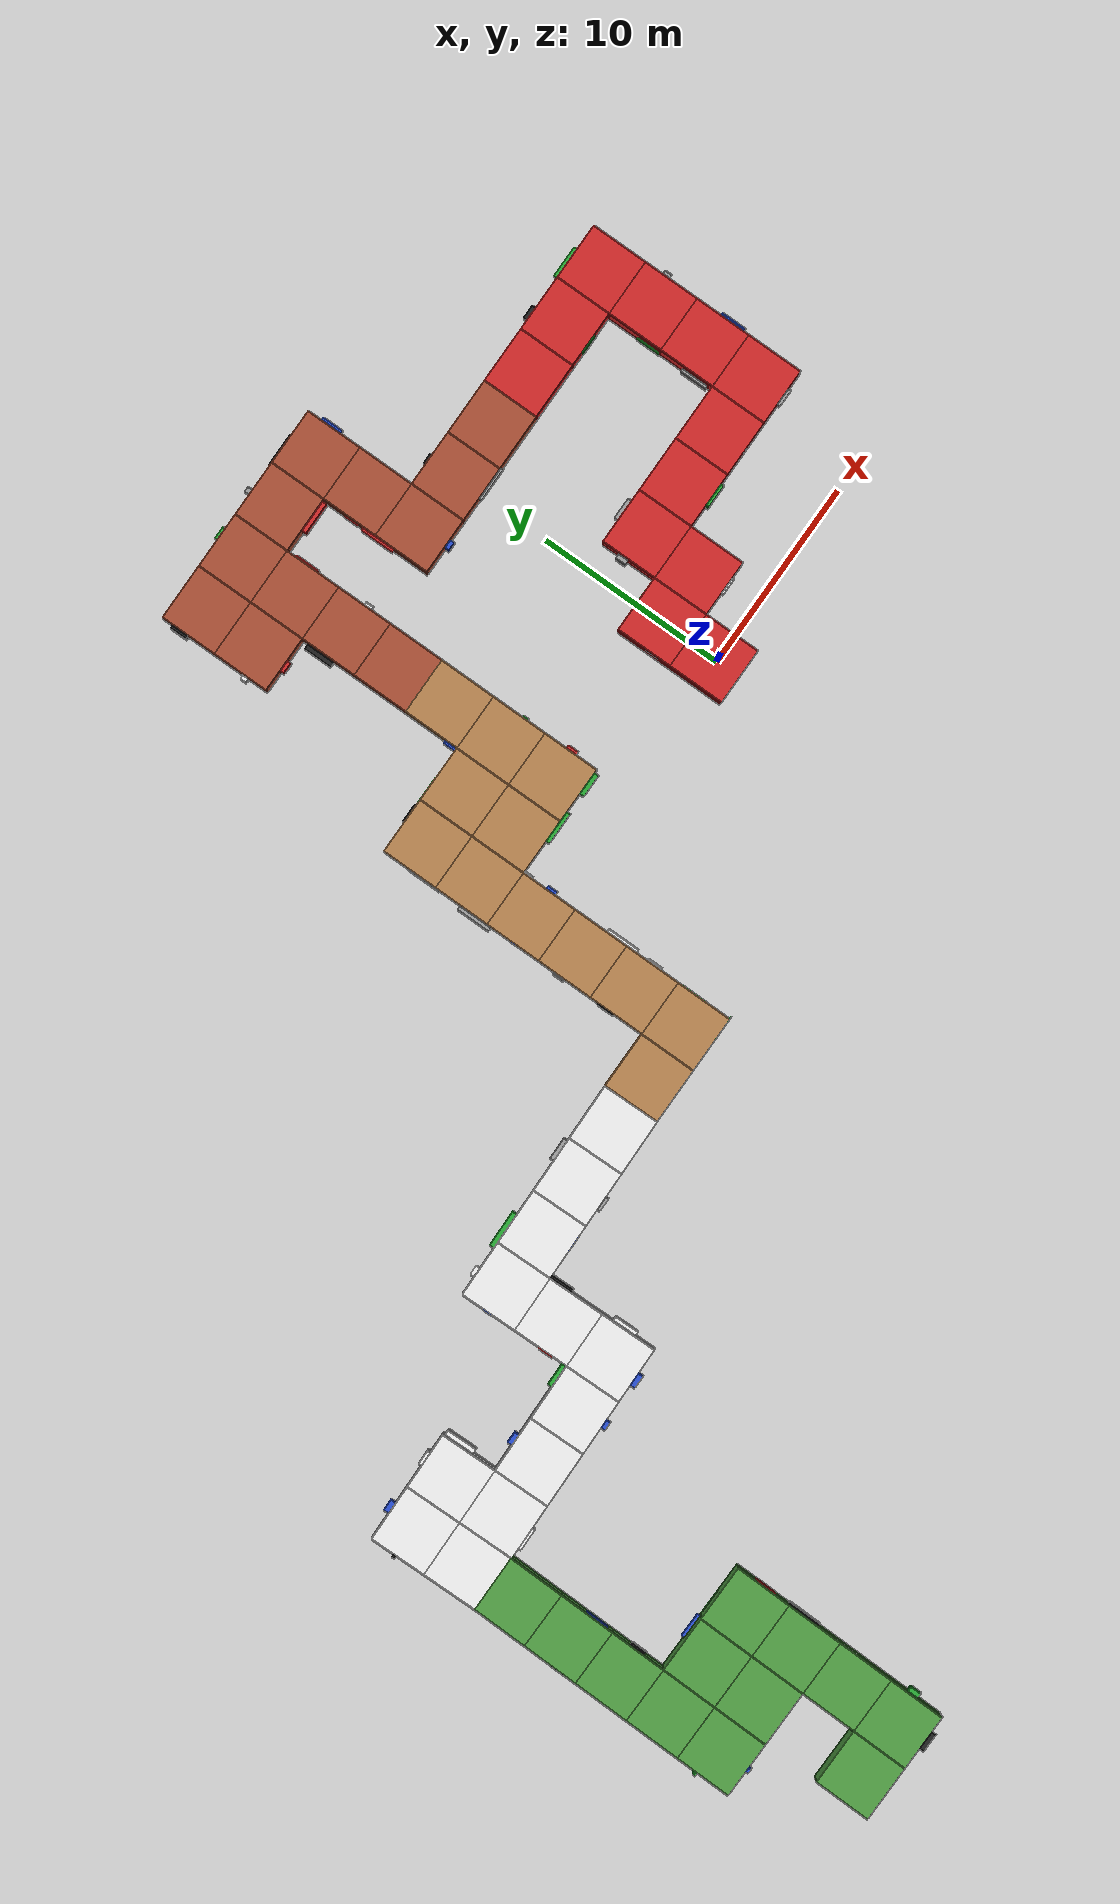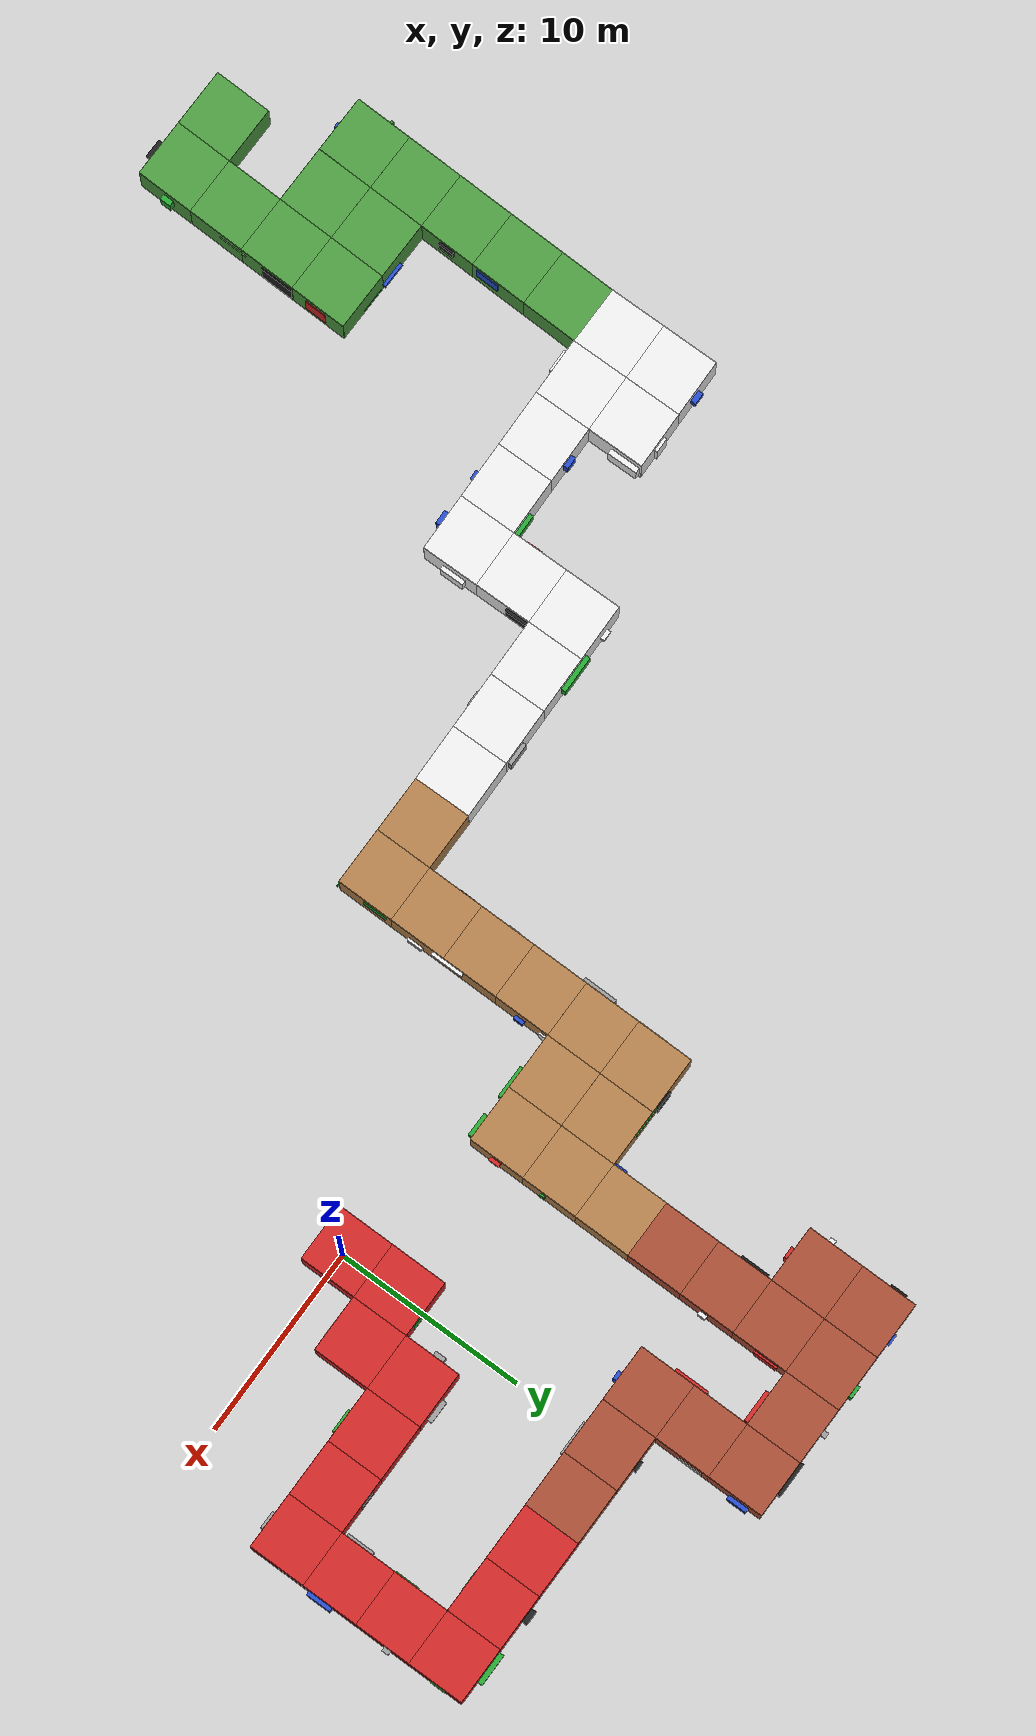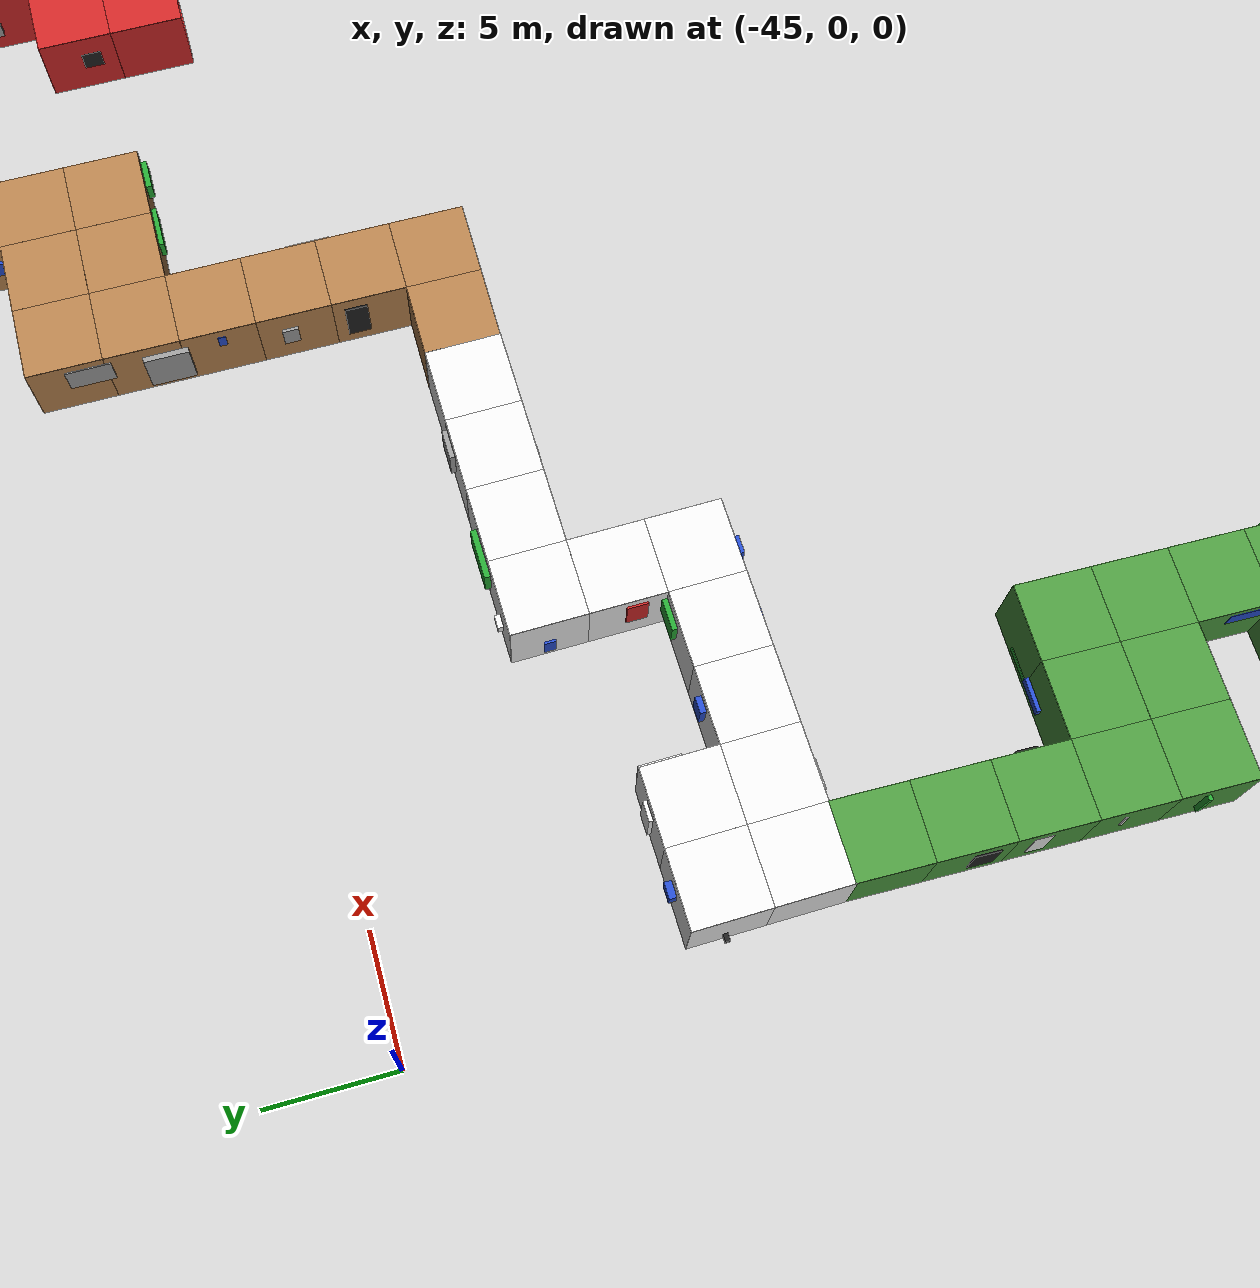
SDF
<sdf version="1.6">
 <world name="default">
  <light name="sun" type="directional">
   <pose>0 0 10 0 -0 0</pose>
   <diffuse>0.8 0.8 0.8 1</diffuse>
   <specular>0.1 0.1 0.1 1</specular>
   <attenuation>
    <range>1000</range>
    <constant>0.9</constant>
    <linear>0.01</linear>
    <quadratic>0.001</quadratic>
   </attenuation>
   <direction>-0.5 0.5 -1</direction>
  </light>
  <light name="lightball_a_-1_2_0_2" type="point">
   <cast_shadows>0</cast_shadows>
   <pose>-12.0904 18.2101 2 1.57 -0 1.57</pose>
   <diffuse>10 10 10 255</diffuse>
   <specular>10 10 10 255</specular>
  </light>
  <light name="lightball_a_-1_3_0_2" type="point">
   <cast_shadows>0</cast_shadows>
   <pose>-12.0904 21.2101 2 1.57 -0 0</pose>
   <diffuse>10 10 10 255</diffuse>
   <specular>10 10 10 255</specular>
  </light>
  <light name="lightball_a_0_0_0_0" type="point">
   <cast_shadows>0</cast_shadows>
   <pose>-9.09042 12.2101 2 1.57 -0 0</pose>
   <diffuse>10 10 10 255</diffuse>
   <specular>10 10 10 255</specular>
  </light>
  <light name="lightball_a_0_1_0_1" type="point">
   <cast_shadows>0</cast_shadows>
   <pose>-9.09042 15.2101 2 1.57 -0 0</pose>
   <diffuse>10 10 10 255</diffuse>
   <specular>10 10 10 255</specular>
  </light>
  <light name="lightball_a_0_2_0_3" type="point">
   <cast_shadows>0</cast_shadows>
   <pose>-9.09042 18.2101 2 1.57 -0 0</pose>
   <diffuse>10 10 10 255</diffuse>
   <specular>10 10 10 255</specular>
  </light>
  <light name="lightball_a_0_3_0_1" type="point">
   <cast_shadows>0</cast_shadows>
   <pose>-9.09042 21.2101 2 1.57 0 -1.57</pose>
   <diffuse>10 10 10 255</diffuse>
   <specular>10 10 10 255</specular>
  </light>
  <light name="lightball_a_1_3_0_1" type="point">
   <cast_shadows>0</cast_shadows>
   <pose>-6.09042 21.2101 2 1.57 0 -1.57</pose>
   <diffuse>10 10 10 255</diffuse>
   <specular>10 10 10 255</specular>
  </light>
  <light name="lightball_a_2_1_0_3" type="point">
   <cast_shadows>0</cast_shadows>
   <pose>-3.09042 15.2101 2 1.57 0 3.14</pose>
   <diffuse>10 10 10 255</diffuse>
   <specular>10 10 10 255</specular>
  </light>
  <light name="lightball_a_2_2_0_1" type="point">
   <cast_shadows>0</cast_shadows>
   <pose>-3.09042 18.2101 2 1.57 0 3.14</pose>
   <diffuse>10 10 10 255</diffuse>
   <specular>10 10 10 255</specular>
  </light>
  <light name="lightball_a_2_3_0_2" type="point">
   <cast_shadows>0</cast_shadows>
   <pose>-3.09042 21.2101 2 1.57 0 -1.57</pose>
   <diffuse>10 10 10 255</diffuse>
   <specular>10 10 10 255</specular>
  </light>
  <light name="lightball_a_3_1_0_1" type="point">
   <cast_shadows>0</cast_shadows>
   <pose>-0.09042 15.2101 2 1.57 0 -1.57</pose>
   <diffuse>10 10 10 255</diffuse>
   <specular>10 10 10 255</specular>
  </light>
  <light name="lightball_a_4_1_0_4" type="point">
   <cast_shadows>0</cast_shadows>
   <pose>2.90958 15.2101 2 1.57 0 -1.57</pose>
   <diffuse>10 10 10 255</diffuse>
   <specular>10 10 10 255</specular>
  </light>
  <light name="lightball_b_-1_1_0_1" type="point">
   <cast_shadows>0</cast_shadows>
   <pose>-36.3211 -33.0905 2 1.57 -0 -0.019264</pose>
   <diffuse>10 10 10 255</diffuse>
   <specular>10 10 10 255</specular>
  </light>
  <light name="lightball_b_-2_-1_0_2" type="point">
   <cast_shadows>0</cast_shadows>
   <pose>-42.2647 -29.9803 2 1.57 0 1.55074</pose>
   <diffuse>10 10 10 255</diffuse>
   <specular>10 10 10 255</specular>
  </light>
  <light name="lightball_b_-2_0_0_2" type="point">
   <cast_shadows>0</cast_shadows>
   <pose>-39.2652 -30.0357 2 1.57 -0 3.12393</pose>
   <diffuse>10 10 10 255</diffuse>
   <specular>10 10 10 255</specular>
  </light>
  <light name="lightball_b_-2_1_0_1" type="point">
   <cast_shadows>0</cast_shadows>
   <pose>-36.2657 -30.091 2 1.57 -0 -0.019264</pose>
   <diffuse>10 10 10 255</diffuse>
   <specular>10 10 10 255</specular>
  </light>
  <light name="lightball_b_-3_-1_0_1" type="point">
   <cast_shadows>0</cast_shadows>
   <pose>-42.2092 -26.9807 2 1.57 -0 -0.019264</pose>
   <diffuse>10 10 10 255</diffuse>
   <specular>10 10 10 255</specular>
  </light>
  <light name="lightball_b_-3_0_0_3" type="point">
   <cast_shadows>0</cast_shadows>
   <pose>-39.2098 -27.0361 2 1.57 0 1.55074</pose>
   <diffuse>10 10 10 255</diffuse>
   <specular>10 10 10 255</specular>
  </light>
  <light name="lightball_b_-3_1_0_3" type="point">
   <cast_shadows>0</cast_shadows>
   <pose>-36.2102 -27.0915 2 1.57 -0 -0.019264</pose>
   <diffuse>10 10 10 255</diffuse>
   <specular>10 10 10 255</specular>
  </light>
  <light name="lightball_b_-4_-1_0_1" type="point">
   <cast_shadows>0</cast_shadows>
   <pose>-42.1538 -23.9813 2 1.57 -0 -0.019264</pose>
   <diffuse>10 10 10 255</diffuse>
   <specular>10 10 10 255</specular>
  </light>
  <light name="lightball_b_-5_-1_0_1" type="point">
   <cast_shadows>0</cast_shadows>
   <pose>-42.0984 -20.9817 2 1.57 -0 -0.019264</pose>
   <diffuse>10 10 10 255</diffuse>
   <specular>10 10 10 255</specular>
  </light>
  <light name="lightball_b_-6_-1_0_4" type="point">
   <cast_shadows>0</cast_shadows>
   <pose>-42.0431 -17.9823 2 1.57 -0 -0.019264</pose>
   <diffuse>10 10 10 255</diffuse>
   <specular>10 10 10 255</specular>
  </light>
  <light name="lightball_b_0_0_0_0" type="point">
   <cast_shadows>0</cast_shadows>
   <pose>-39.3759 -36.0346 2 1.57 -0 -1.58926</pose>
   <diffuse>10 10 10 255</diffuse>
   <specular>10 10 10 255</specular>
  </light>
  <light name="lightball_b_0_1_0_3" type="point">
   <cast_shadows>0</cast_shadows>
   <pose>-36.3765 -36.09 2 1.57 -0 -1.58926</pose>
   <diffuse>10 10 10 255</diffuse>
   <specular>10 10 10 255</specular>
  </light>
  <light name="lightball_c_0_0_0_0" type="point">
   <cast_shadows>0</cast_shadows>
   <pose>-0.091197 0.213608 2 1.57 -0 0</pose>
   <diffuse>10 10 10 255</diffuse>
   <specular>10 10 10 255</specular>
  </light>
  <light name="lightball_c_0_1_0_2" type="point">
   <cast_shadows>0</cast_shadows>
   <pose>-0.091197 3.21361 2 1.57 -0 0</pose>
   <diffuse>10 10 10 255</diffuse>
   <specular>10 10 10 255</specular>
  </light>
  <light name="lightball_c_1_1_0_3" type="point">
   <cast_shadows>0</cast_shadows>
   <pose>2.9088 3.21361 2 1.57 0 -1.57</pose>
   <diffuse>10 10 10 255</diffuse>
   <specular>10 10 10 255</specular>
  </light>
  <light name="lightball_c_1_2_0_2" type="point">
   <cast_shadows>0</cast_shadows>
   <pose>2.9088 6.21361 2 1.57 -0 0</pose>
   <diffuse>10 10 10 255</diffuse>
   <specular>10 10 10 255</specular>
  </light>
  <light name="lightball_c_2_2_0_1" type="point">
   <cast_shadows>0</cast_shadows>
   <pose>5.9088 6.21361 2 1.57 0 -1.57</pose>
   <diffuse>10 10 10 255</diffuse>
   <specular>10 10 10 255</specular>
  </light>
  <light name="lightball_c_2_5_0_4" type="point">
   <cast_shadows>0</cast_shadows>
   <pose>5.9088 15.2136 2 1.57 -0 1.57</pose>
   <diffuse>10 10 10 255</diffuse>
   <specular>10 10 10 255</specular>
  </light>
  <light name="lightball_c_3_2_0_1" type="point">
   <cast_shadows>0</cast_shadows>
   <pose>8.9088 6.21361 2 1.57 0 -1.57</pose>
   <diffuse>10 10 10 255</diffuse>
   <specular>10 10 10 255</specular>
  </light>
  <light name="lightball_c_3_5_0_1" type="point">
   <cast_shadows>0</cast_shadows>
   <pose>8.9088 15.2136 2 1.57 -0 1.57</pose>
   <diffuse>10 10 10 255</diffuse>
   <specular>10 10 10 255</specular>
  </light>
  <light name="lightball_c_4_2_0_3" type="point">
   <cast_shadows>0</cast_shadows>
   <pose>11.9088 6.21361 2 1.57 0 -1.57</pose>
   <diffuse>10 10 10 255</diffuse>
   <specular>10 10 10 255</specular>
  </light>
  <light name="lightball_c_4_3_0_1" type="point">
   <cast_shadows>0</cast_shadows>
   <pose>11.9088 9.21361 2 1.57 -0 0</pose>
   <diffuse>10 10 10 255</diffuse>
   <specular>10 10 10 255</specular>
  </light>
  <light name="lightball_c_4_4_0_1" type="point">
   <cast_shadows>0</cast_shadows>
   <pose>11.9088 12.2136 2 1.57 -0 0</pose>
   <diffuse>10 10 10 255</diffuse>
   <specular>10 10 10 255</specular>
  </light>
  <light name="lightball_c_4_5_0_3" type="point">
   <cast_shadows>0</cast_shadows>
   <pose>11.9088 15.2136 2 1.57 -0 0</pose>
   <diffuse>10 10 10 255</diffuse>
   <specular>10 10 10 255</specular>
  </light>
  <light name="lightball_d_-1_3_0_1" type="point">
   <cast_shadows>0</cast_shadows>
   <pose>-30.0805 -11.9162 2 1.57 -0 -3.12816</pose>
   <diffuse>10 10 10 255</diffuse>
   <specular>10 10 10 255</specular>
  </light>
  <light name="lightball_d_-1_6_0_3" type="point">
   <cast_shadows>0</cast_shadows>
   <pose>-39.0796 -12.0443 2 1.57 -0 0.015029</pose>
   <diffuse>10 10 10 255</diffuse>
   <specular>10 10 10 255</specular>
  </light>
  <light name="lightball_d_-1_7_0_3" type="point">
   <cast_shadows>0</cast_shadows>
   <pose>-42.0793 -12.087 2 1.57 -0 1.58503</pose>
   <diffuse>10 10 10 255</diffuse>
   <specular>10 10 10 255</specular>
  </light>
  <light name="lightball_d_-2_3_0_2" type="point">
   <cast_shadows>0</cast_shadows>
   <pose>-30.0378 -14.9159 2 1.57 -0 -3.12816</pose>
   <diffuse>10 10 10 255</diffuse>
   <specular>10 10 10 255</specular>
  </light>
  <light name="lightball_d_-2_4_0_1" type="point">
   <cast_shadows>0</cast_shadows>
   <pose>-33.0375 -14.9586 2 1.57 -0 1.58503</pose>
   <diffuse>10 10 10 255</diffuse>
   <specular>10 10 10 255</specular>
  </light>
  <light name="lightball_d_-2_5_0_1" type="point">
   <cast_shadows>0</cast_shadows>
   <pose>-36.0372 -15.0013 2 1.57 -0 1.58503</pose>
   <diffuse>10 10 10 255</diffuse>
   <specular>10 10 10 255</specular>
  </light>
  <light name="lightball_d_-2_6_0_2" type="point">
   <cast_shadows>0</cast_shadows>
   <pose>-39.0369 -15.044 2 1.57 -0 1.58503</pose>
   <diffuse>10 10 10 255</diffuse>
   <specular>10 10 10 255</specular>
  </light>
  <light name="lightball_d_-2_7_0_4" type="point">
   <cast_shadows>0</cast_shadows>
   <pose>-42.0366 -15.0867 2 1.57 -0 -3.12816</pose>
   <diffuse>10 10 10 255</diffuse>
   <specular>10 10 10 255</specular>
  </light>
  <light name="lightball_d_0_0_0_0" type="point">
   <cast_shadows>0</cast_shadows>
   <pose>-21.1241 -8.78843 2 1.57 -0 1.58503</pose>
   <diffuse>10 10 10 255</diffuse>
   <specular>10 10 10 255</specular>
  </light>
  <light name="lightball_d_0_1_0_1" type="point">
   <cast_shadows>0</cast_shadows>
   <pose>-24.1238 -8.83113 2 1.57 -0 1.58503</pose>
   <diffuse>10 10 10 255</diffuse>
   <specular>10 10 10 255</specular>
  </light>
  <light name="lightball_d_0_2_0_1" type="point">
   <cast_shadows>0</cast_shadows>
   <pose>-27.1235 -8.87383 2 1.57 -0 1.58503</pose>
   <diffuse>10 10 10 255</diffuse>
   <specular>10 10 10 255</specular>
  </light>
  <light name="lightball_d_0_3_0_3" type="point">
   <cast_shadows>0</cast_shadows>
   <pose>-30.1232 -8.91652 2 1.57 -0 1.58503</pose>
   <diffuse>10 10 10 255</diffuse>
   <specular>10 10 10 255</specular>
  </light>
  <light name="lightball_e_0_0_0_0" type="point">
   <cast_shadows>0</cast_shadows>
   <pose>-9.09662 9.21864 2 1.57 -0 3.13953</pose>
   <diffuse>10 10 10 255</diffuse>
   <specular>10 10 10 255</specular>
  </light>
  <light name="lightball_e_0_1_0_1" type="point">
   <cast_shadows>0</cast_shadows>
   <pose>-9.1028 6.21865 2 1.57 -0 3.13953</pose>
   <diffuse>10 10 10 255</diffuse>
   <specular>10 10 10 255</specular>
  </light>
  <light name="lightball_e_0_2_0_2" type="point">
   <cast_shadows>0</cast_shadows>
   <pose>-9.10899 3.21866 2 1.57 -0 3.13953</pose>
   <diffuse>10 10 10 255</diffuse>
   <specular>10 10 10 255</specular>
  </light>
  <light name="lightball_e_1_1_0_3" type="point">
   <cast_shadows>0</cast_shadows>
   <pose>-12.1028 6.22483 2 1.57 -0 -0.003654</pose>
   <diffuse>10 10 10 255</diffuse>
   <specular>10 10 10 255</specular>
  </light>
  <light name="lightball_e_1_2_0_2" type="point">
   <cast_shadows>0</cast_shadows>
   <pose>-12.109 3.22484 2 1.57 0 1.56953</pose>
   <diffuse>10 10 10 255</diffuse>
   <specular>10 10 10 255</specular>
  </light>
  <light name="lightball_e_2_1_0_3" type="point">
   <cast_shadows>0</cast_shadows>
   <pose>-15.1028 6.23102 2 1.57 0 1.56953</pose>
   <diffuse>10 10 10 255</diffuse>
   <specular>10 10 10 255</specular>
  </light>
  <light name="lightball_e_2_2_0_1" type="point">
   <cast_shadows>0</cast_shadows>
   <pose>-15.109 3.23102 2 1.57 -0 3.13953</pose>
   <diffuse>10 10 10 255</diffuse>
   <specular>10 10 10 255</specular>
  </light>
  <light name="lightball_e_2_3_0_1" type="point">
   <cast_shadows>0</cast_shadows>
   <pose>-15.1152 0.23103 2 1.57 -0 3.13953</pose>
   <diffuse>10 10 10 255</diffuse>
   <specular>10 10 10 255</specular>
  </light>
  <light name="lightball_e_2_4_0_1" type="point">
   <cast_shadows>0</cast_shadows>
   <pose>-15.1213 -2.76896 2 1.57 -0 3.13953</pose>
   <diffuse>10 10 10 255</diffuse>
   <specular>10 10 10 255</specular>
  </light>
  <light name="lightball_e_2_5_0_1" type="point">
   <cast_shadows>0</cast_shadows>
   <pose>-15.1275 -5.76896 2 1.57 -0 3.13953</pose>
   <diffuse>10 10 10 255</diffuse>
   <specular>10 10 10 255</specular>
  </light>
  <light name="lightball_e_2_6_0_2" type="point">
   <cast_shadows>0</cast_shadows>
   <pose>-15.1337 -8.76895 2 1.57 -0 3.13953</pose>
   <diffuse>10 10 10 255</diffuse>
   <specular>10 10 10 255</specular>
  </light>
  <light name="lightball_e_3_6_0_4" type="point">
   <cast_shadows>0</cast_shadows>
   <pose>-18.1337 -8.76277 2 1.57 0 1.56953</pose>
   <diffuse>10 10 10 255</diffuse>
   <specular>10 10 10 255</specular>
  </light>
  <model name="ground_plane">
   <static>1</static>
   <link name="link">
    <collision name="collision">
     <geometry><plane><normal>0 0 1</normal><size>100 100</size></plane></geometry>
     <surface><friction><ode><mu>100</mu><mu2>50</mu2></ode></friction></surface>
    </collision>
    <visual name="visual">
     <cast_shadows>0</cast_shadows>
     <geometry><plane><normal>0 0 1</normal><size>100 100</size></plane></geometry>
     <material>
      <script><uri>file://media/materials/scripts/gazebo.material</uri><name>Gazebo/Grey</name></script>
     </material>
    </visual>
   </link>
  </model>
  <gravity>0 0 -9.8</gravity>
  <magnetic_field>6e-06 2.3e-05 -4.2e-05</magnetic_field>
  <atmosphere type="adiabatic"/>
  <physics name="default_physics" default="0" type="ode">
   <max_step_size>0.001</max_step_size>
   <real_time_factor>1</real_time_factor>
   <real_time_update_rate>1000</real_time_update_rate>
  </physics>
  <scene><ambient>0.4 0.4 0.4 1</ambient><background>0.7 0.7 0.7 1</background><shadows>1</shadows></scene>
  <spherical_coordinates>
   <surface_model>EARTH_WGS84</surface_model>
   <latitude_deg>0</latitude_deg>
   <longitude_deg>0</longitude_deg>
   <elevation>0</elevation>
   <heading_deg>0</heading_deg>
  </spherical_coordinates>
  <model name="corridor_red">
   <model name="wall_right_0_0_0_0">
    <static>1</static>
    <pose>1.5 0 1.5 0 -0 1.57</pose>
    <link name="link">
     <collision name="collision"><geometry><box><size>3 0.02 3</size></box></geometry></collision>
     <visual name="visual">
      <material>
       <script><name>Gazebo/Red</name><uri>file://media/materials/scripts/gazebo.material</uri></script>
      </material>
      <geometry><box><size>3 0.02 3</size></box></geometry>
     </visual>
    </link>
   </model>
   <model name="wall_left_0_0_0_0">
    <static>1</static>
    <pose>-1.5 0 1.5 0 -0 1.57</pose>
    <link name="link">
     <collision name="collision"><geometry><box><size>3 0.02 3</size></box></geometry></collision>
     <visual name="visual">
      <material>
       <script><name>Gazebo/Red</name><uri>file://media/materials/scripts/gazebo.material</uri></script>
      </material>
      <geometry><box><size>3 0.02 3</size></box></geometry>
     </visual>
    </link>
   </model>
   <model name="wall_top_0_0_0_0">
    <static>1</static>
    <pose>0 0 3 1.57 -0 0</pose>
    <link name="link">
     <collision name="collision"><geometry><box><size>3 0.02 3</size></box></geometry></collision>
     <visual name="visual">
      <material>
       <script><name>Gazebo/Red</name><uri>file://media/materials/scripts/gazebo.material</uri></script>
      </material>
      <geometry><box><size>3 0.02 3</size></box></geometry>
     </visual>
    </link>
   </model>
   <model name="wall_bottom_0_0_0_0">
    <static>1</static>
    <pose>0 0 0 1.57 -0 0</pose>
    <link name="link">
     <collision name="collision"><geometry><box><size>3 0.02 3</size></box></geometry></collision>
     <visual name="visual">
      <material>
       <script><name>Gazebo/Red</name><uri>file://media/materials/scripts/gazebo.material</uri></script>
      </material>
      <geometry><box><size>3 0.02 3</size></box></geometry>
     </visual>
    </link>
   </model>
   <model name="wall_front_0_1_0_2">
    <static>1</static>
    <pose>0 4.5 1.5 0 -0 0</pose>
    <link name="link">
     <collision name="collision"><geometry><box><size>3 0.02 3</size></box></geometry></collision>
     <visual name="visual">
      <material>
       <script><name>Gazebo/Red</name><uri>file://media/materials/scripts/gazebo.material</uri></script>
      </material>
      <geometry><box><size>3 0.02 3</size></box></geometry>
     </visual>
    </link>
   </model>
   <model name="wall_left_0_1_0_2">
    <static>1</static>
    <pose>-1.5 3 1.5 0 -0 1.57</pose>
    <link name="link">
     <collision name="collision"><geometry><box><size>3 0.02 3</size></box></geometry></collision>
     <visual name="visual">
      <material>
       <script><name>Gazebo/Red</name><uri>file://media/materials/scripts/gazebo.material</uri></script>
      </material>
      <geometry><box><size>3 0.02 3</size></box></geometry>
     </visual>
    </link>
   </model>
   <model name="wall_top_0_1_0_2">
    <static>1</static>
    <pose>0 3 3 1.57 -0 0</pose>
    <link name="link">
     <collision name="collision"><geometry><box><size>3 0.02 3</size></box></geometry></collision>
     <visual name="visual">
      <material>
       <script><name>Gazebo/Red</name><uri>file://media/materials/scripts/gazebo.material</uri></script>
      </material>
      <geometry><box><size>3 0.02 3</size></box></geometry>
     </visual>
    </link>
   </model>
   <model name="wall_bottom_0_1_0_2">
    <static>1</static>
    <pose>0 3 0 1.57 -0 0</pose>
    <link name="link">
     <collision name="collision"><geometry><box><size>3 0.02 3</size></box></geometry></collision>
     <visual name="visual">
      <material>
       <script><name>Gazebo/Red</name><uri>file://media/materials/scripts/gazebo.material</uri></script>
      </material>
      <geometry><box><size>3 0.02 3</size></box></geometry>
     </visual>
    </link>
   </model>
   <model name="panel_0_1_0_2">
    <static>1</static>
    <pose>0.487638 4.5 1.52326 0 -0 1.57</pose>
    <link name="link">
     <collision name="collision"><geometry><box><size>0.058495 0.864081 1.93927</size></box></geometry></collision>
     <visual name="visual">
      <material>
       <script><name>Gazebo/Green</name><uri>file://media/materials/scripts/gazebo.material</uri></script>
      </material>
      <geometry><box><size>0.058495 0.864081 1.93927</size></box></geometry>
     </visual>
    </link>
   </model>
   <model name="panel_0_1_1_2">
    <static>1</static>
    <pose>-1.5 2.52412 1.63613 0 -0 0</pose>
    <link name="link">
     <collision name="collision">
      <geometry><box><size>0.045875 0.808978 0.846938</size></box></geometry>
     </collision>
     <visual name="visual">
      <material>
       <script><name>Gazebo/Black</name><uri>file://media/materials/scripts/gazebo.material</uri></script>
      </material>
      <geometry><box><size>0.045875 0.808978 0.846938</size></box></geometry>
     </visual>
    </link>
   </model>
   <model name="wall_front_1_1_0_3">
    <static>1</static>
    <pose>4.5 3 1.5 0 0 -1.57</pose>
    <link name="link">
     <collision name="collision"><geometry><box><size>3 0.02 3</size></box></geometry></collision>
     <visual name="visual">
      <material>
       <script><name>Gazebo/Red</name><uri>file://media/materials/scripts/gazebo.material</uri></script>
      </material>
      <geometry><box><size>3 0.02 3</size></box></geometry>
     </visual>
    </link>
   </model>
   <model name="wall_right_1_1_0_3">
    <static>1</static>
    <pose>3 1.5 1.5 0 -0 0</pose>
    <link name="link">
     <collision name="collision"><geometry><box><size>3 0.02 3</size></box></geometry></collision>
     <visual name="visual">
      <material>
       <script><name>Gazebo/Red</name><uri>file://media/materials/scripts/gazebo.material</uri></script>
      </material>
      <geometry><box><size>3 0.02 3</size></box></geometry>
     </visual>
    </link>
   </model>
   <model name="wall_top_1_1_0_3">
    <static>1</static>
    <pose>3 3 3 1.57 0 -1.57</pose>
    <link name="link">
     <collision name="collision"><geometry><box><size>3 0.02 3</size></box></geometry></collision>
     <visual name="visual">
      <material>
       <script><name>Gazebo/Red</name><uri>file://media/materials/scripts/gazebo.material</uri></script>
      </material>
      <geometry><box><size>3 0.02 3</size></box></geometry>
     </visual>
    </link>
   </model>
   <model name="wall_bottom_1_1_0_3">
    <static>1</static>
    <pose>3 3 0 1.57 0 -1.57</pose>
    <link name="link">
     <collision name="collision"><geometry><box><size>3 0.02 3</size></box></geometry></collision>
     <visual name="visual">
      <material>
       <script><name>Gazebo/Red</name><uri>file://media/materials/scripts/gazebo.material</uri></script>
      </material>
      <geometry><box><size>3 0.02 3</size></box></geometry>
     </visual>
    </link>
   </model>
   <model name="panel_1_1_0_3">
    <static>1</static>
    <pose>4.5 3.93743 1.50054 0 -0 0</pose>
    <link name="link">
     <collision name="collision"><geometry><box><size>0.007959 1.45146 1.98542</size></box></geometry></collision>
     <visual name="visual">
      <material>
       <script><name>Gazebo/White</name><uri>file://media/materials/scripts/gazebo.material</uri></script>
      </material>
      <geometry><box><size>0.007959 1.45146 1.98542</size></box></geometry>
     </visual>
    </link>
   </model>
   <model name="panel_1_1_1_3">
    <static>1</static>
    <pose>3.24702 1.5 1.29993 0 0 -1.57</pose>
    <link name="link">
     <collision name="collision">
      <geometry><box><size>0.208442 0.891773 0.952969</size></box></geometry>
     </collision>
     <visual name="visual">
      <material>
       <script><name>Gazebo/White</name><uri>file://media/materials/scripts/gazebo.material</uri></script>
      </material>
      <geometry><box><size>0.208442 0.891773 0.952969</size></box></geometry>
     </visual>
    </link>
   </model>
   <model name="wall_front_1_2_0_2">
    <static>1</static>
    <pose>3 7.5 1.5 0 -0 0</pose>
    <link name="link">
     <collision name="collision"><geometry><box><size>3 0.02 3</size></box></geometry></collision>
     <visual name="visual">
      <material>
       <script><name>Gazebo/Red</name><uri>file://media/materials/scripts/gazebo.material</uri></script>
      </material>
      <geometry><box><size>3 0.02 3</size></box></geometry>
     </visual>
    </link>
   </model>
   <model name="wall_left_1_2_0_2">
    <static>1</static>
    <pose>1.5 6 1.5 0 -0 1.57</pose>
    <link name="link">
     <collision name="collision"><geometry><box><size>3 0.02 3</size></box></geometry></collision>
     <visual name="visual">
      <material>
       <script><name>Gazebo/Red</name><uri>file://media/materials/scripts/gazebo.material</uri></script>
      </material>
      <geometry><box><size>3 0.02 3</size></box></geometry>
     </visual>
    </link>
   </model>
   <model name="wall_top_1_2_0_2">
    <static>1</static>
    <pose>3 6 3 1.57 -0 0</pose>
    <link name="link">
     <collision name="collision"><geometry><box><size>3 0.02 3</size></box></geometry></collision>
     <visual name="visual">
      <material>
       <script><name>Gazebo/Red</name><uri>file://media/materials/scripts/gazebo.material</uri></script>
      </material>
      <geometry><box><size>3 0.02 3</size></box></geometry>
     </visual>
    </link>
   </model>
   <model name="wall_bottom_1_2_0_2">
    <static>1</static>
    <pose>3 6 0 1.57 -0 0</pose>
    <link name="link">
     <collision name="collision"><geometry><box><size>3 0.02 3</size></box></geometry></collision>
     <visual name="visual">
      <material>
       <script><name>Gazebo/Red</name><uri>file://media/materials/scripts/gazebo.material</uri></script>
      </material>
      <geometry><box><size>3 0.02 3</size></box></geometry>
     </visual>
    </link>
   </model>
   <model name="panel_1_2_0_2">
    <static>1</static>
    <pose>3.38466 7.5 1.07951 0 -0 1.57</pose>
    <link name="link">
     <collision name="collision"><geometry><box><size>0.518997 1.1635 0.317813</size></box></geometry></collision>
     <visual name="visual">
      <material>
       <script><name>Gazebo/Grey</name><uri>file://media/materials/scripts/gazebo.material</uri></script>
      </material>
      <geometry><box><size>0.518997 1.1635 0.317813</size></box></geometry>
     </visual>
    </link>
   </model>
   <model name="panel_1_2_1_2">
    <static>1</static>
    <pose>1.5 6.27988 1.72428 0 -0 0</pose>
    <link name="link">
     <collision name="collision"><geometry><box><size>0.54761 0.568058 1.47225</size></box></geometry></collision>
     <visual name="visual">
      <material>
       <script><name>Gazebo/Grey</name><uri>file://media/materials/scripts/gazebo.material</uri></script>
      </material>
      <geometry><box><size>0.54761 0.568058 1.47225</size></box></geometry>
     </visual>
    </link>
   </model>
   <model name="wall_right_2_2_0_1">
    <static>1</static>
    <pose>6 4.5 1.5 0 -0 0</pose>
    <link name="link">
     <collision name="collision"><geometry><box><size>3 0.02 3</size></box></geometry></collision>
     <visual name="visual">
      <material>
       <script><name>Gazebo/Red</name><uri>file://media/materials/scripts/gazebo.material</uri></script>
      </material>
      <geometry><box><size>3 0.02 3</size></box></geometry>
     </visual>
    </link>
   </model>
   <model name="wall_left_2_2_0_1">
    <static>1</static>
    <pose>6 7.5 1.5 0 -0 0</pose>
    <link name="link">
     <collision name="collision"><geometry><box><size>3 0.02 3</size></box></geometry></collision>
     <visual name="visual">
      <material>
       <script><name>Gazebo/Red</name><uri>file://media/materials/scripts/gazebo.material</uri></script>
      </material>
      <geometry><box><size>3 0.02 3</size></box></geometry>
     </visual>
    </link>
   </model>
   <model name="wall_top_2_2_0_1">
    <static>1</static>
    <pose>6 6 3 1.57 0 -1.57</pose>
    <link name="link">
     <collision name="collision"><geometry><box><size>3 0.02 3</size></box></geometry></collision>
     <visual name="visual">
      <material>
       <script><name>Gazebo/Red</name><uri>file://media/materials/scripts/gazebo.material</uri></script>
      </material>
      <geometry><box><size>3 0.02 3</size></box></geometry>
     </visual>
    </link>
   </model>
   <model name="wall_bottom_2_2_0_1">
    <static>1</static>
    <pose>6 6 0 1.57 0 -1.57</pose>
    <link name="link">
     <collision name="collision"><geometry><box><size>3 0.02 3</size></box></geometry></collision>
     <visual name="visual">
      <material>
       <script><name>Gazebo/Red</name><uri>file://media/materials/scripts/gazebo.material</uri></script>
      </material>
      <geometry><box><size>3 0.02 3</size></box></geometry>
     </visual>
    </link>
   </model>
   <model name="panel_2_2_0_1">
    <static>1</static>
    <pose>6.38985 4.5 1.54685 0 0 -1.57</pose>
    <link name="link">
     <collision name="collision"><geometry><box><size>0.301136 1.24316 1.88123</size></box></geometry></collision>
     <visual name="visual">
      <material>
       <script><name>Gazebo/Green</name><uri>file://media/materials/scripts/gazebo.material</uri></script>
      </material>
      <geometry><box><size>0.301136 1.24316 1.88123</size></box></geometry>
     </visual>
    </link>
   </model>
   <model name="panel_2_2_1_1">
    <static>1</static>
    <pose>5.69595 7.5 1.54694 0 0 -1.57</pose>
    <link name="link">
     <collision name="collision"><geometry><box><size>0.003623 0.754308 1.92735</size></box></geometry></collision>
     <visual name="visual">
      <material>
       <script><name>Gazebo/Black</name><uri>file://media/materials/scripts/gazebo.material</uri></script>
      </material>
      <geometry><box><size>0.003623 0.754308 1.92735</size></box></geometry>
     </visual>
    </link>
   </model>
   <model name="wall_right_3_2_0_1">
    <static>1</static>
    <pose>9 4.5 1.5 0 -0 0</pose>
    <link name="link">
     <collision name="collision"><geometry><box><size>3 0.02 3</size></box></geometry></collision>
     <visual name="visual">
      <material>
       <script><name>Gazebo/Red</name><uri>file://media/materials/scripts/gazebo.material</uri></script>
      </material>
      <geometry><box><size>3 0.02 3</size></box></geometry>
     </visual>
    </link>
   </model>
   <model name="wall_left_3_2_0_1">
    <static>1</static>
    <pose>9 7.5 1.5 0 -0 0</pose>
    <link name="link">
     <collision name="collision"><geometry><box><size>3 0.02 3</size></box></geometry></collision>
     <visual name="visual">
      <material>
       <script><name>Gazebo/Red</name><uri>file://media/materials/scripts/gazebo.material</uri></script>
      </material>
      <geometry><box><size>3 0.02 3</size></box></geometry>
     </visual>
    </link>
   </model>
   <model name="wall_top_3_2_0_1">
    <static>1</static>
    <pose>9 6 3 1.57 0 -1.57</pose>
    <link name="link">
     <collision name="collision"><geometry><box><size>3 0.02 3</size></box></geometry></collision>
     <visual name="visual">
      <material>
       <script><name>Gazebo/Red</name><uri>file://media/materials/scripts/gazebo.material</uri></script>
      </material>
      <geometry><box><size>3 0.02 3</size></box></geometry>
     </visual>
    </link>
   </model>
   <model name="wall_bottom_3_2_0_1">
    <static>1</static>
    <pose>9 6 0 1.57 0 -1.57</pose>
    <link name="link">
     <collision name="collision"><geometry><box><size>3 0.02 3</size></box></geometry></collision>
     <visual name="visual">
      <material>
       <script><name>Gazebo/Red</name><uri>file://media/materials/scripts/gazebo.material</uri></script>
      </material>
      <geometry><box><size>3 0.02 3</size></box></geometry>
     </visual>
    </link>
   </model>
   <model name="panel_3_2_0_1">
    <static>1</static>
    <pose>9.03117 4.5 1.3522 0 0 -1.57</pose>
    <link name="link">
     <collision name="collision">
      <geometry><box><size>0.035317 0.295151 0.625916</size></box></geometry>
     </collision>
     <visual name="visual">
      <material>
       <script><name>Gazebo/Black</name><uri>file://media/materials/scripts/gazebo.material</uri></script>
      </material>
      <geometry><box><size>0.035317 0.295151 0.625916</size></box></geometry>
     </visual>
    </link>
   </model>
   <model name="panel_3_2_1_1">
    <static>1</static>
    <pose>8.59102 7.5 1.63821 0 0 -1.57</pose>
    <link name="link">
     <collision name="collision"><geometry><box><size>0.032025 0.85761 1.79264</size></box></geometry></collision>
     <visual name="visual">
      <material>
       <script><name>Gazebo/Grey</name><uri>file://media/materials/scripts/gazebo.material</uri></script>
      </material>
      <geometry><box><size>0.032025 0.85761 1.79264</size></box></geometry>
     </visual>
    </link>
   </model>
   <model name="wall_front_4_2_0_3">
    <static>1</static>
    <pose>13.5 6 1.5 0 0 -1.57</pose>
    <link name="link">
     <collision name="collision"><geometry><box><size>3 0.02 3</size></box></geometry></collision>
     <visual name="visual">
      <material>
       <script><name>Gazebo/Red</name><uri>file://media/materials/scripts/gazebo.material</uri></script>
      </material>
      <geometry><box><size>3 0.02 3</size></box></geometry>
     </visual>
    </link>
   </model>
   <model name="wall_right_4_2_0_3">
    <static>1</static>
    <pose>12 4.5 1.5 0 -0 0</pose>
    <link name="link">
     <collision name="collision"><geometry><box><size>3 0.02 3</size></box></geometry></collision>
     <visual name="visual">
      <material>
       <script><name>Gazebo/Red</name><uri>file://media/materials/scripts/gazebo.material</uri></script>
      </material>
      <geometry><box><size>3 0.02 3</size></box></geometry>
     </visual>
    </link>
   </model>
   <model name="wall_top_4_2_0_3">
    <static>1</static>
    <pose>12 6 3 1.57 0 -1.57</pose>
    <link name="link">
     <collision name="collision"><geometry><box><size>3 0.02 3</size></box></geometry></collision>
     <visual name="visual">
      <material>
       <script><name>Gazebo/Red</name><uri>file://media/materials/scripts/gazebo.material</uri></script>
      </material>
      <geometry><box><size>3 0.02 3</size></box></geometry>
     </visual>
    </link>
   </model>
   <model name="wall_bottom_4_2_0_3">
    <static>1</static>
    <pose>12 6 0 1.57 0 -1.57</pose>
    <link name="link">
     <collision name="collision"><geometry><box><size>3 0.02 3</size></box></geometry></collision>
     <visual name="visual">
      <material>
       <script><name>Gazebo/Red</name><uri>file://media/materials/scripts/gazebo.material</uri></script>
      </material>
      <geometry><box><size>3 0.02 3</size></box></geometry>
     </visual>
    </link>
   </model>
   <model name="panel_4_2_0_3">
    <static>1</static>
    <pose>12.0527 4.5 2.28153 0 0 -1.57</pose>
    <link name="link">
     <collision name="collision"><geometry><box><size>0.31983 0.91885 0.76039</size></box></geometry></collision>
     <visual name="visual">
      <material>
       <script><name>Gazebo/Grey</name><uri>file://media/materials/scripts/gazebo.material</uri></script>
      </material>
      <geometry><box><size>0.31983 0.91885 0.76039</size></box></geometry>
     </visual>
    </link>
   </model>
   <model name="panel_4_2_1_3">
    <static>1</static>
    <pose>13.5 6.9027 1.83159 0 -0 0</pose>
    <link name="link">
     <collision name="collision"><geometry><box><size>0.044124 1.70247 0.736742</size></box></geometry></collision>
     <visual name="visual">
      <material>
       <script><name>Gazebo/Black</name><uri>file://media/materials/scripts/gazebo.material</uri></script>
      </material>
      <geometry><box><size>0.044124 1.70247 0.736742</size></box></geometry>
     </visual>
    </link>
   </model>
   <model name="wall_right_4_3_0_1">
    <static>1</static>
    <pose>13.5 9 1.5 0 -0 1.57</pose>
    <link name="link">
     <collision name="collision"><geometry><box><size>3 0.02 3</size></box></geometry></collision>
     <visual name="visual">
      <material>
       <script><name>Gazebo/Red</name><uri>file://media/materials/scripts/gazebo.material</uri></script>
      </material>
      <geometry><box><size>3 0.02 3</size></box></geometry>
     </visual>
    </link>
   </model>
   <model name="wall_left_4_3_0_1">
    <static>1</static>
    <pose>10.5 9 1.5 0 -0 1.57</pose>
    <link name="link">
     <collision name="collision"><geometry><box><size>3 0.02 3</size></box></geometry></collision>
     <visual name="visual">
      <material>
       <script><name>Gazebo/Red</name><uri>file://media/materials/scripts/gazebo.material</uri></script>
      </material>
      <geometry><box><size>3 0.02 3</size></box></geometry>
     </visual>
    </link>
   </model>
   <model name="wall_top_4_3_0_1">
    <static>1</static>
    <pose>12 9 3 1.57 -0 0</pose>
    <link name="link">
     <collision name="collision"><geometry><box><size>3 0.02 3</size></box></geometry></collision>
     <visual name="visual">
      <material>
       <script><name>Gazebo/Red</name><uri>file://media/materials/scripts/gazebo.material</uri></script>
      </material>
      <geometry><box><size>3 0.02 3</size></box></geometry>
     </visual>
    </link>
   </model>
   <model name="wall_bottom_4_3_0_1">
    <static>1</static>
    <pose>12 9 0 1.57 -0 0</pose>
    <link name="link">
     <collision name="collision"><geometry><box><size>3 0.02 3</size></box></geometry></collision>
     <visual name="visual">
      <material>
       <script><name>Gazebo/Red</name><uri>file://media/materials/scripts/gazebo.material</uri></script>
      </material>
      <geometry><box><size>3 0.02 3</size></box></geometry>
     </visual>
    </link>
   </model>
   <model name="panel_4_3_0_1">
    <static>1</static>
    <pose>13.5 8.48738 1.23135 0 -0 0</pose>
    <link name="link">
     <collision name="collision"><geometry><box><size>0.452088 1.32208 1.54683</size></box></geometry></collision>
     <visual name="visual">
      <material>
       <script><name>Gazebo/Blue</name><uri>file://media/materials/scripts/gazebo.material</uri></script>
      </material>
      <geometry><box><size>0.452088 1.32208 1.54683</size></box></geometry>
     </visual>
    </link>
   </model>
   <model name="panel_4_3_1_1">
    <static>1</static>
    <pose>10.5 8.44795 1.20364 0 -0 0</pose>
    <link name="link">
     <collision name="collision"><geometry><box><size>0.378508 1.47639 0.925448</size></box></geometry></collision>
     <visual name="visual">
      <material>
       <script><name>Gazebo/Grey</name><uri>file://media/materials/scripts/gazebo.material</uri></script>
      </material>
      <geometry><box><size>0.378508 1.47639 0.925448</size></box></geometry>
     </visual>
    </link>
   </model>
   <model name="wall_right_4_4_0_1">
    <static>1</static>
    <pose>13.5 12 1.5 0 -0 1.57</pose>
    <link name="link">
     <collision name="collision"><geometry><box><size>3 0.02 3</size></box></geometry></collision>
     <visual name="visual">
      <material>
       <script><name>Gazebo/Red</name><uri>file://media/materials/scripts/gazebo.material</uri></script>
      </material>
      <geometry><box><size>3 0.02 3</size></box></geometry>
     </visual>
    </link>
   </model>
   <model name="wall_left_4_4_0_1">
    <static>1</static>
    <pose>10.5 12 1.5 0 -0 1.57</pose>
    <link name="link">
     <collision name="collision"><geometry><box><size>3 0.02 3</size></box></geometry></collision>
     <visual name="visual">
      <material>
       <script><name>Gazebo/Red</name><uri>file://media/materials/scripts/gazebo.material</uri></script>
      </material>
      <geometry><box><size>3 0.02 3</size></box></geometry>
     </visual>
    </link>
   </model>
   <model name="wall_top_4_4_0_1">
    <static>1</static>
    <pose>12 12 3 1.57 -0 0</pose>
    <link name="link">
     <collision name="collision"><geometry><box><size>3 0.02 3</size></box></geometry></collision>
     <visual name="visual">
      <material>
       <script><name>Gazebo/Red</name><uri>file://media/materials/scripts/gazebo.material</uri></script>
      </material>
      <geometry><box><size>3 0.02 3</size></box></geometry>
     </visual>
    </link>
   </model>
   <model name="wall_bottom_4_4_0_1">
    <static>1</static>
    <pose>12 12 0 1.57 -0 0</pose>
    <link name="link">
     <collision name="collision"><geometry><box><size>3 0.02 3</size></box></geometry></collision>
     <visual name="visual">
      <material>
       <script><name>Gazebo/Red</name><uri>file://media/materials/scripts/gazebo.material</uri></script>
      </material>
      <geometry><box><size>3 0.02 3</size></box></geometry>
     </visual>
    </link>
   </model>
   <model name="panel_4_4_0_1">
    <static>1</static>
    <pose>13.5 12.3336 2.40579 0 -0 0</pose>
    <link name="link">
     <collision name="collision">
      <geometry><box><size>0.491219 0.372776 0.328603</size></box></geometry>
     </collision>
     <visual name="visual">
      <material>
       <script><name>Gazebo/Grey</name><uri>file://media/materials/scripts/gazebo.material</uri></script>
      </material>
      <geometry><box><size>0.491219 0.372776 0.328603</size></box></geometry>
     </visual>
    </link>
   </model>
   <model name="panel_4_4_1_1">
    <static>1</static>
    <pose>10.5 11.1531 0.941465 0 -0 0</pose>
    <link name="link">
     <collision name="collision"><geometry><box><size>0.193777 1.28866 0.769732</size></box></geometry></collision>
     <visual name="visual">
      <material>
       <script><name>Gazebo/Green</name><uri>file://media/materials/scripts/gazebo.material</uri></script>
      </material>
      <geometry><box><size>0.193777 1.28866 0.769732</size></box></geometry>
     </visual>
    </link>
   </model>
   <model name="wall_front_4_5_0_3">
    <static>1</static>
    <pose>12 16.5 1.5 0 -0 0</pose>
    <link name="link">
     <collision name="collision"><geometry><box><size>3 0.02 3</size></box></geometry></collision>
     <visual name="visual">
      <material>
       <script><name>Gazebo/Red</name><uri>file://media/materials/scripts/gazebo.material</uri></script>
      </material>
      <geometry><box><size>3 0.02 3</size></box></geometry>
     </visual>
    </link>
   </model>
   <model name="wall_right_4_5_0_3">
    <static>1</static>
    <pose>13.5 15 1.5 0 -0 1.57</pose>
    <link name="link">
     <collision name="collision"><geometry><box><size>3 0.02 3</size></box></geometry></collision>
     <visual name="visual">
      <material>
       <script><name>Gazebo/Red</name><uri>file://media/materials/scripts/gazebo.material</uri></script>
      </material>
      <geometry><box><size>3 0.02 3</size></box></geometry>
     </visual>
    </link>
   </model>
   <model name="wall_top_4_5_0_3">
    <static>1</static>
    <pose>12 15 3 1.57 -0 0</pose>
    <link name="link">
     <collision name="collision"><geometry><box><size>3 0.02 3</size></box></geometry></collision>
     <visual name="visual">
      <material>
       <script><name>Gazebo/Red</name><uri>file://media/materials/scripts/gazebo.material</uri></script>
      </material>
      <geometry><box><size>3 0.02 3</size></box></geometry>
     </visual>
    </link>
   </model>
   <model name="wall_bottom_4_5_0_3">
    <static>1</static>
    <pose>12 15 0 1.57 -0 0</pose>
    <link name="link">
     <collision name="collision"><geometry><box><size>3 0.02 3</size></box></geometry></collision>
     <visual name="visual">
      <material>
       <script><name>Gazebo/Red</name><uri>file://media/materials/scripts/gazebo.material</uri></script>
      </material>
      <geometry><box><size>3 0.02 3</size></box></geometry>
     </visual>
    </link>
   </model>
   <model name="panel_4_5_0_3">
    <static>1</static>
    <pose>13.5 15.177 1.52472 0 -0 0</pose>
    <link name="link">
     <collision name="collision">
      <geometry><box><size>0.142618 0.870041 0.341173</size></box></geometry>
     </collision>
     <visual name="visual">
      <material>
       <script><name>Gazebo/Green</name><uri>file://media/materials/scripts/gazebo.material</uri></script>
      </material>
      <geometry><box><size>0.142618 0.870041 0.341173</size></box></geometry>
     </visual>
    </link>
   </model>
   <model name="panel_4_5_1_3">
    <static>1</static>
    <pose>11.4205 16.5 1.0039 0 -0 1.57</pose>
    <link name="link">
     <collision name="collision"><geometry><box><size>0.529992 1.69585 0.508778</size></box></geometry></collision>
     <visual name="visual">
      <material>
       <script><name>Gazebo/Green</name><uri>file://media/materials/scripts/gazebo.material</uri></script>
      </material>
      <geometry><box><size>0.529992 1.69585 0.508778</size></box></geometry>
     </visual>
    </link>
   </model>
   <model name="wall_right_3_5_0_1">
    <static>1</static>
    <pose>9 16.5 1.5 0 -0 3.14</pose>
    <link name="link">
     <collision name="collision"><geometry><box><size>3 0.02 3</size></box></geometry></collision>
     <visual name="visual">
      <material>
       <script><name>Gazebo/Red</name><uri>file://media/materials/scripts/gazebo.material</uri></script>
      </material>
      <geometry><box><size>3 0.02 3</size></box></geometry>
     </visual>
    </link>
   </model>
   <model name="wall_left_3_5_0_1">
    <static>1</static>
    <pose>9 13.5 1.5 0 -0 3.14</pose>
    <link name="link">
     <collision name="collision"><geometry><box><size>3 0.02 3</size></box></geometry></collision>
     <visual name="visual">
      <material>
       <script><name>Gazebo/Red</name><uri>file://media/materials/scripts/gazebo.material</uri></script>
      </material>
      <geometry><box><size>3 0.02 3</size></box></geometry>
     </visual>
    </link>
   </model>
   <model name="wall_top_3_5_0_1">
    <static>1</static>
    <pose>9 15 3 1.57 -0 1.57</pose>
    <link name="link">
     <collision name="collision"><geometry><box><size>3 0.02 3</size></box></geometry></collision>
     <visual name="visual">
      <material>
       <script><name>Gazebo/Red</name><uri>file://media/materials/scripts/gazebo.material</uri></script>
      </material>
      <geometry><box><size>3 0.02 3</size></box></geometry>
     </visual>
    </link>
   </model>
   <model name="wall_bottom_3_5_0_1">
    <static>1</static>
    <pose>9 15 0 1.57 -0 1.57</pose>
    <link name="link">
     <collision name="collision"><geometry><box><size>3 0.02 3</size></box></geometry></collision>
     <visual name="visual">
      <material>
       <script><name>Gazebo/Red</name><uri>file://media/materials/scripts/gazebo.material</uri></script>
      </material>
      <geometry><box><size>3 0.02 3</size></box></geometry>
     </visual>
    </link>
   </model>
   <model name="panel_3_5_0_1">
    <static>1</static>
    <pose>8.45714 16.5 1.02262 0 -0 1.57</pose>
    <link name="link">
     <collision name="collision">
      <geometry><box><size>0.557092 0.742877 0.954808</size></box></geometry>
     </collision>
     <visual name="visual">
      <material>
       <script><name>Gazebo/Black</name><uri>file://media/materials/scripts/gazebo.material</uri></script>
      </material>
      <geometry><box><size>0.557092 0.742877 0.954808</size></box></geometry>
     </visual>
    </link>
   </model>
   <model name="panel_3_5_1_1">
    <static>1</static>
    <pose>8.80504 13.5 1.43494 0 -0 1.57</pose>
    <link name="link">
     <collision name="collision"><geometry><box><size>0.105957 0.99063 1.76904</size></box></geometry></collision>
     <visual name="visual">
      <material>
       <script><name>Gazebo/Green</name><uri>file://media/materials/scripts/gazebo.material</uri></script>
      </material>
      <geometry><box><size>0.105957 0.99063 1.76904</size></box></geometry>
     </visual>
    </link>
   </model>
   <model name="wall_right_2_5_0_4">
    <static>1</static>
    <pose>6 16.5 1.5 0 -0 3.14</pose>
    <link name="link">
     <collision name="collision"><geometry><box><size>3 0.02 3</size></box></geometry></collision>
     <visual name="visual">
      <material>
       <script><name>Gazebo/Red</name><uri>file://media/materials/scripts/gazebo.material</uri></script>
      </material>
      <geometry><box><size>3 0.02 3</size></box></geometry>
     </visual>
    </link>
   </model>
   <model name="wall_left_2_5_0_4">
    <static>1</static>
    <pose>6 13.5 1.5 0 -0 3.14</pose>
    <link name="link">
     <collision name="collision"><geometry><box><size>3 0.02 3</size></box></geometry></collision>
     <visual name="visual">
      <material>
       <script><name>Gazebo/Red</name><uri>file://media/materials/scripts/gazebo.material</uri></script>
      </material>
      <geometry><box><size>3 0.02 3</size></box></geometry>
     </visual>
    </link>
   </model>
   <model name="wall_top_2_5_0_4">
    <static>1</static>
    <pose>6 15 3 1.57 -0 1.57</pose>
    <link name="link">
     <collision name="collision"><geometry><box><size>3 0.02 3</size></box></geometry></collision>
     <visual name="visual">
      <material>
       <script><name>Gazebo/Red</name><uri>file://media/materials/scripts/gazebo.material</uri></script>
      </material>
      <geometry><box><size>3 0.02 3</size></box></geometry>
     </visual>
    </link>
   </model>
   <model name="wall_bottom_2_5_0_4">
    <static>1</static>
    <pose>6 15 0 1.57 -0 1.57</pose>
    <link name="link">
     <collision name="collision"><geometry><box><size>3 0.02 3</size></box></geometry></collision>
     <visual name="visual">
      <material>
       <script><name>Gazebo/Red</name><uri>file://media/materials/scripts/gazebo.material</uri></script>
      </material>
      <geometry><box><size>3 0.02 3</size></box></geometry>
     </visual>
    </link>
   </model>
   <pose>-0.0912 0.213608 0 0 -0 0</pose>
  </model>
  <model name="corridor_brick">
   <model name="wall_right_0_0_0_0">
    <static>1</static>
    <pose>1.5 0 1.5 0 -0 1.57</pose>
    <link name="link">
     <collision name="collision"><geometry><box><size>3 0.02 3</size></box></geometry></collision>
     <visual name="visual">
      <material>
       <script><name>Gazebo/Bricks</name><uri>file://media/materials/scripts/gazebo.material</uri></script>
      </material>
      <geometry><box><size>3 0.02 3</size></box></geometry>
     </visual>
    </link>
   </model>
   <model name="wall_left_0_0_0_0">
    <static>1</static>
    <pose>-1.5 0 1.5 0 -0 1.57</pose>
    <link name="link">
     <collision name="collision"><geometry><box><size>3 0.02 3</size></box></geometry></collision>
     <visual name="visual">
      <material>
       <script><name>Gazebo/Bricks</name><uri>file://media/materials/scripts/gazebo.material</uri></script>
      </material>
      <geometry><box><size>3 0.02 3</size></box></geometry>
     </visual>
    </link>
   </model>
   <model name="wall_top_0_0_0_0">
    <static>1</static>
    <pose>0 0 3 1.57 -0 0</pose>
    <link name="link">
     <collision name="collision"><geometry><box><size>3 0.02 3</size></box></geometry></collision>
     <visual name="visual">
      <material>
       <script><name>Gazebo/Bricks</name><uri>file://media/materials/scripts/gazebo.material</uri></script>
      </material>
      <geometry><box><size>3 0.02 3</size></box></geometry>
     </visual>
    </link>
   </model>
   <model name="wall_bottom_0_0_0_0">
    <static>1</static>
    <pose>0 0 0 1.57 -0 0</pose>
    <link name="link">
     <collision name="collision"><geometry><box><size>3 0.02 3</size></box></geometry></collision>
     <visual name="visual">
      <material>
       <script><name>Gazebo/Bricks</name><uri>file://media/materials/scripts/gazebo.material</uri></script>
      </material>
      <geometry><box><size>3 0.02 3</size></box></geometry>
     </visual>
    </link>
   </model>
   <model name="wall_right_0_1_0_1">
    <static>1</static>
    <pose>1.5 3 1.5 0 -0 1.57</pose>
    <link name="link">
     <collision name="collision"><geometry><box><size>3 0.02 3</size></box></geometry></collision>
     <visual name="visual">
      <material>
       <script><name>Gazebo/Bricks</name><uri>file://media/materials/scripts/gazebo.material</uri></script>
      </material>
      <geometry><box><size>3 0.02 3</size></box></geometry>
     </visual>
    </link>
   </model>
   <model name="wall_left_0_1_0_1">
    <static>1</static>
    <pose>-1.5 3 1.5 0 -0 1.57</pose>
    <link name="link">
     <collision name="collision"><geometry><box><size>3 0.02 3</size></box></geometry></collision>
     <visual name="visual">
      <material>
       <script><name>Gazebo/Bricks</name><uri>file://media/materials/scripts/gazebo.material</uri></script>
      </material>
      <geometry><box><size>3 0.02 3</size></box></geometry>
     </visual>
    </link>
   </model>
   <model name="wall_top_0_1_0_1">
    <static>1</static>
    <pose>0 3 3 1.57 -0 0</pose>
    <link name="link">
     <collision name="collision"><geometry><box><size>3 0.02 3</size></box></geometry></collision>
     <visual name="visual">
      <material>
       <script><name>Gazebo/Bricks</name><uri>file://media/materials/scripts/gazebo.material</uri></script>
      </material>
      <geometry><box><size>3 0.02 3</size></box></geometry>
     </visual>
    </link>
   </model>
   <model name="wall_bottom_0_1_0_1">
    <static>1</static>
    <pose>0 3 0 1.57 -0 0</pose>
    <link name="link">
     <collision name="collision"><geometry><box><size>3 0.02 3</size></box></geometry></collision>
     <visual name="visual">
      <material>
       <script><name>Gazebo/Bricks</name><uri>file://media/materials/scripts/gazebo.material</uri></script>
      </material>
      <geometry><box><size>3 0.02 3</size></box></geometry>
     </visual>
    </link>
   </model>
   <model name="panel_0_1_0_1">
    <static>1</static>
    <pose>1.5 2.86714 1.54842 0 -0 0</pose>
    <link name="link">
     <collision name="collision"><geometry><box><size>0.415689 0.426792 0.8428</size></box></geometry></collision>
     <visual name="visual">
      <material>
       <script><name>Gazebo/White</name><uri>file://media/materials/scripts/gazebo.material</uri></script>
      </material>
      <geometry><box><size>0.415689 0.426792 0.8428</size></box></geometry>
     </visual>
    </link>
   </model>
   <model name="panel_0_1_1_1">
    <static>1</static>
    <pose>-1.5 3.46855 0.808961 0 -0 0</pose>
    <link name="link">
     <collision name="collision"><geometry><box><size>0.59016 1.53864 0.108758</size></box></geometry></collision>
     <visual name="visual">
      <material>
       <script><name>Gazebo/Black</name><uri>file://media/materials/scripts/gazebo.material</uri></script>
      </material>
      <geometry><box><size>0.59016 1.53864 0.108758</size></box></geometry>
     </visual>
    </link>
   </model>
   <model name="wall_front_0_2_0_3">
    <static>1</static>
    <pose>0 7.5 1.5 0 -0 0</pose>
    <link name="link">
     <collision name="collision"><geometry><box><size>3 0.02 3</size></box></geometry></collision>
     <visual name="visual">
      <material>
       <script><name>Gazebo/Bricks</name><uri>file://media/materials/scripts/gazebo.material</uri></script>
      </material>
      <geometry><box><size>3 0.02 3</size></box></geometry>
     </visual>
    </link>
   </model>
   <model name="wall_right_0_2_0_3">
    <static>1</static>
    <pose>1.5 6 1.5 0 -0 1.57</pose>
    <link name="link">
     <collision name="collision"><geometry><box><size>3 0.02 3</size></box></geometry></collision>
     <visual name="visual">
      <material>
       <script><name>Gazebo/Bricks</name><uri>file://media/materials/scripts/gazebo.material</uri></script>
      </material>
      <geometry><box><size>3 0.02 3</size></box></geometry>
     </visual>
    </link>
   </model>
   <model name="wall_top_0_2_0_3">
    <static>1</static>
    <pose>0 6 3 1.57 -0 0</pose>
    <link name="link">
     <collision name="collision"><geometry><box><size>3 0.02 3</size></box></geometry></collision>
     <visual name="visual">
      <material>
       <script><name>Gazebo/Bricks</name><uri>file://media/materials/scripts/gazebo.material</uri></script>
      </material>
      <geometry><box><size>3 0.02 3</size></box></geometry>
     </visual>
    </link>
   </model>
   <model name="wall_bottom_0_2_0_3">
    <static>1</static>
    <pose>0 6 0 1.57 -0 0</pose>
    <link name="link">
     <collision name="collision"><geometry><box><size>3 0.02 3</size></box></geometry></collision>
     <visual name="visual">
      <material>
       <script><name>Gazebo/Bricks</name><uri>file://media/materials/scripts/gazebo.material</uri></script>
      </material>
      <geometry><box><size>3 0.02 3</size></box></geometry>
     </visual>
    </link>
   </model>
   <model name="panel_0_2_0_3">
    <static>1</static>
    <pose>1.5 6.41841 1.5317 0 -0 0</pose>
    <link name="link">
     <collision name="collision"><geometry><box><size>0.235176 1.29699 1.54614</size></box></geometry></collision>
     <visual name="visual">
      <material>
       <script><name>Gazebo/Red</name><uri>file://media/materials/scripts/gazebo.material</uri></script>
      </material>
      <geometry><box><size>0.235176 1.29699 1.54614</size></box></geometry>
     </visual>
    </link>
   </model>
   <model name="panel_0_2_1_3">
    <static>1</static>
    <pose>0.337745 7.5 1.64292 0 -0 1.57</pose>
    <link name="link">
     <collision name="collision"><geometry><box><size>0.460968 1.34549 1.78302</size></box></geometry></collision>
     <visual name="visual">
      <material>
       <script><name>Gazebo/Blue</name><uri>file://media/materials/scripts/gazebo.material</uri></script>
      </material>
      <geometry><box><size>0.460968 1.34549 1.78302</size></box></geometry>
     </visual>
    </link>
   </model>
   <model name="wall_front_-1_2_0_2">
    <static>1</static>
    <pose>-4.5 6 1.5 0 -0 1.57</pose>
    <link name="link">
     <collision name="collision"><geometry><box><size>3 0.02 3</size></box></geometry></collision>
     <visual name="visual">
      <material>
       <script><name>Gazebo/Bricks</name><uri>file://media/materials/scripts/gazebo.material</uri></script>
      </material>
      <geometry><box><size>3 0.02 3</size></box></geometry>
     </visual>
    </link>
   </model>
   <model name="wall_left_-1_2_0_2">
    <static>1</static>
    <pose>-3 4.5 1.5 0 -0 3.14</pose>
    <link name="link">
     <collision name="collision"><geometry><box><size>3 0.02 3</size></box></geometry></collision>
     <visual name="visual">
      <material>
       <script><name>Gazebo/Bricks</name><uri>file://media/materials/scripts/gazebo.material</uri></script>
      </material>
      <geometry><box><size>3 0.02 3</size></box></geometry>
     </visual>
    </link>
   </model>
   <model name="wall_top_-1_2_0_2">
    <static>1</static>
    <pose>-3 6 3 1.57 -0 1.57</pose>
    <link name="link">
     <collision name="collision"><geometry><box><size>3 0.02 3</size></box></geometry></collision>
     <visual name="visual">
      <material>
       <script><name>Gazebo/Bricks</name><uri>file://media/materials/scripts/gazebo.material</uri></script>
      </material>
      <geometry><box><size>3 0.02 3</size></box></geometry>
     </visual>
    </link>
   </model>
   <model name="wall_bottom_-1_2_0_2">
    <static>1</static>
    <pose>-3 6 0 1.57 -0 1.57</pose>
    <link name="link">
     <collision name="collision"><geometry><box><size>3 0.02 3</size></box></geometry></collision>
     <visual name="visual">
      <material>
       <script><name>Gazebo/Bricks</name><uri>file://media/materials/scripts/gazebo.material</uri></script>
      </material>
      <geometry><box><size>3 0.02 3</size></box></geometry>
     </visual>
    </link>
   </model>
   <model name="panel_-1_2_0_2">
    <static>1</static>
    <pose>-3.04799 4.5 1.44122 0 -0 1.57</pose>
    <link name="link">
     <collision name="collision"><geometry><box><size>0.36733 0.607265 1.87687</size></box></geometry></collision>
     <visual name="visual">
      <material>
       <script><name>Gazebo/Red</name><uri>file://media/materials/scripts/gazebo.material</uri></script>
      </material>
      <geometry><box><size>0.36733 0.607265 1.87687</size></box></geometry>
     </visual>
    </link>
   </model>
   <model name="panel_-1_2_1_2">
    <static>1</static>
    <pose>-4.5 5.68025 1.80865 0 -0 3.14</pose>
    <link name="link">
     <collision name="collision"><geometry><box><size>0.498409 0.308606 1.47851</size></box></geometry></collision>
     <visual name="visual">
      <material>
       <script><name>Gazebo/White</name><uri>file://media/materials/scripts/gazebo.material</uri></script>
      </material>
      <geometry><box><size>0.498409 0.308606 1.47851</size></box></geometry>
     </visual>
    </link>
   </model>
   <model name="wall_front_-1_3_0_2">
    <static>1</static>
    <pose>-3 10.5 1.5 0 -0 0</pose>
    <link name="link">
     <collision name="collision"><geometry><box><size>3 0.02 3</size></box></geometry></collision>
     <visual name="visual">
      <material>
       <script><name>Gazebo/Bricks</name><uri>file://media/materials/scripts/gazebo.material</uri></script>
      </material>
      <geometry><box><size>3 0.02 3</size></box></geometry>
     </visual>
    </link>
   </model>
   <model name="wall_left_-1_3_0_2">
    <static>1</static>
    <pose>-4.5 9 1.5 0 -0 1.57</pose>
    <link name="link">
     <collision name="collision"><geometry><box><size>3 0.02 3</size></box></geometry></collision>
     <visual name="visual">
      <material>
       <script><name>Gazebo/Bricks</name><uri>file://media/materials/scripts/gazebo.material</uri></script>
      </material>
      <geometry><box><size>3 0.02 3</size></box></geometry>
     </visual>
    </link>
   </model>
   <model name="wall_top_-1_3_0_2">
    <static>1</static>
    <pose>-3 9 3 1.57 -0 0</pose>
    <link name="link">
     <collision name="collision"><geometry><box><size>3 0.02 3</size></box></geometry></collision>
     <visual name="visual">
      <material>
       <script><name>Gazebo/Bricks</name><uri>file://media/materials/scripts/gazebo.material</uri></script>
      </material>
      <geometry><box><size>3 0.02 3</size></box></geometry>
     </visual>
    </link>
   </model>
   <model name="wall_bottom_-1_3_0_2">
    <static>1</static>
    <pose>-3 9 0 1.57 -0 0</pose>
    <link name="link">
     <collision name="collision"><geometry><box><size>3 0.02 3</size></box></geometry></collision>
     <visual name="visual">
      <material>
       <script><name>Gazebo/Bricks</name><uri>file://media/materials/scripts/gazebo.material</uri></script>
      </material>
      <geometry><box><size>3 0.02 3</size></box></geometry>
     </visual>
    </link>
   </model>
   <model name="panel_-1_3_0_2">
    <static>1</static>
    <pose>-4.5 9.49984 1.33748 0 -0 0</pose>
    <link name="link">
     <collision name="collision"><geometry><box><size>0.36753 0.890218 1.72396</size></box></geometry></collision>
     <visual name="visual">
      <material>
       <script><name>Gazebo/Black</name><uri>file://media/materials/scripts/gazebo.material</uri></script>
      </material>
      <geometry><box><size>0.36753 0.890218 1.72396</size></box></geometry>
     </visual>
    </link>
   </model>
   <model name="panel_-1_3_1_2">
    <static>1</static>
    <pose>-2.76493 10.5 0.436052 0 -0 1.57</pose>
    <link name="link">
     <collision name="collision">
      <geometry><box><size>0.220302 0.623552 0.200254</size></box></geometry>
     </collision>
     <visual name="visual">
      <material>
       <script><name>Gazebo/Blue</name><uri>file://media/materials/scripts/gazebo.material</uri></script>
      </material>
      <geometry><box><size>0.220302 0.623552 0.200254</size></box></geometry>
     </visual>
    </link>
   </model>
   <model name="wall_right_0_3_0_1">
    <static>1</static>
    <pose>0 7.5 1.5 0 -0 0</pose>
    <link name="link">
     <collision name="collision"><geometry><box><size>3 0.02 3</size></box></geometry></collision>
     <visual name="visual">
      <material>
       <script><name>Gazebo/Bricks</name><uri>file://media/materials/scripts/gazebo.material</uri></script>
      </material>
      <geometry><box><size>3 0.02 3</size></box></geometry>
     </visual>
    </link>
   </model>
   <model name="wall_left_0_3_0_1">
    <static>1</static>
    <pose>0 10.5 1.5 0 -0 0</pose>
    <link name="link">
     <collision name="collision"><geometry><box><size>3 0.02 3</size></box></geometry></collision>
     <visual name="visual">
      <material>
       <script><name>Gazebo/Bricks</name><uri>file://media/materials/scripts/gazebo.material</uri></script>
      </material>
      <geometry><box><size>3 0.02 3</size></box></geometry>
     </visual>
    </link>
   </model>
   <model name="wall_top_0_3_0_1">
    <static>1</static>
    <pose>0 9 3 1.57 0 -1.57</pose>
    <link name="link">
     <collision name="collision"><geometry><box><size>3 0.02 3</size></box></geometry></collision>
     <visual name="visual">
      <material>
       <script><name>Gazebo/Bricks</name><uri>file://media/materials/scripts/gazebo.material</uri></script>
      </material>
      <geometry><box><size>3 0.02 3</size></box></geometry>
     </visual>
    </link>
   </model>
   <model name="wall_bottom_0_3_0_1">
    <static>1</static>
    <pose>0 9 0 1.57 0 -1.57</pose>
    <link name="link">
     <collision name="collision"><geometry><box><size>3 0.02 3</size></box></geometry></collision>
     <visual name="visual">
      <material>
       <script><name>Gazebo/Bricks</name><uri>file://media/materials/scripts/gazebo.material</uri></script>
      </material>
      <geometry><box><size>3 0.02 3</size></box></geometry>
     </visual>
    </link>
   </model>
   <model name="panel_0_3_0_1">
    <static>1</static>
    <pose>0.346474 10.5 1.7958 0 0 -1.57</pose>
    <link name="link">
     <collision name="collision"><geometry><box><size>0.343406 0.666554 1.4114</size></box></geometry></collision>
     <visual name="visual">
      <material>
       <script><name>Gazebo/Green</name><uri>file://media/materials/scripts/gazebo.material</uri></script>
      </material>
      <geometry><box><size>0.343406 0.666554 1.4114</size></box></geometry>
     </visual>
    </link>
   </model>
   <model name="panel_0_3_1_1">
    <static>1</static>
    <pose>-0.637299 7.5 1.71678 0 0 -1.57</pose>
    <link name="link">
     <collision name="collision"><geometry><box><size>0.270208 1.48869 1.66701</size></box></geometry></collision>
     <visual name="visual">
      <material>
       <script><name>Gazebo/Black</name><uri>file://media/materials/scripts/gazebo.material</uri></script>
      </material>
      <geometry><box><size>0.270208 1.48869 1.66701</size></box></geometry>
     </visual>
    </link>
   </model>
   <model name="wall_right_1_3_0_1">
    <static>1</static>
    <pose>3 7.5 1.5 0 -0 0</pose>
    <link name="link">
     <collision name="collision"><geometry><box><size>3 0.02 3</size></box></geometry></collision>
     <visual name="visual">
      <material>
       <script><name>Gazebo/Bricks</name><uri>file://media/materials/scripts/gazebo.material</uri></script>
      </material>
      <geometry><box><size>3 0.02 3</size></box></geometry>
     </visual>
    </link>
   </model>
   <model name="wall_left_1_3_0_1">
    <static>1</static>
    <pose>3 10.5 1.5 0 -0 0</pose>
    <link name="link">
     <collision name="collision"><geometry><box><size>3 0.02 3</size></box></geometry></collision>
     <visual name="visual">
      <material>
       <script><name>Gazebo/Bricks</name><uri>file://media/materials/scripts/gazebo.material</uri></script>
      </material>
      <geometry><box><size>3 0.02 3</size></box></geometry>
     </visual>
    </link>
   </model>
   <model name="wall_top_1_3_0_1">
    <static>1</static>
    <pose>3 9 3 1.57 0 -1.57</pose>
    <link name="link">
     <collision name="collision"><geometry><box><size>3 0.02 3</size></box></geometry></collision>
     <visual name="visual">
      <material>
       <script><name>Gazebo/Bricks</name><uri>file://media/materials/scripts/gazebo.material</uri></script>
      </material>
      <geometry><box><size>3 0.02 3</size></box></geometry>
     </visual>
    </link>
   </model>
   <model name="wall_bottom_1_3_0_1">
    <static>1</static>
    <pose>3 9 0 1.57 0 -1.57</pose>
    <link name="link">
     <collision name="collision"><geometry><box><size>3 0.02 3</size></box></geometry></collision>
     <visual name="visual">
      <material>
       <script><name>Gazebo/Bricks</name><uri>file://media/materials/scripts/gazebo.material</uri></script>
      </material>
      <geometry><box><size>3 0.02 3</size></box></geometry>
     </visual>
    </link>
   </model>
   <model name="panel_1_3_0_1">
    <static>1</static>
    <pose>2.77104 10.5 2.73337 0 0 -1.57</pose>
    <link name="link">
     <collision name="collision">
      <geometry><box><size>0.537333 0.305933 0.268217</size></box></geometry>
     </collision>
     <visual name="visual">
      <material>
       <script><name>Gazebo/Grey</name><uri>file://media/materials/scripts/gazebo.material</uri></script>
      </material>
      <geometry><box><size>0.537333 0.305933 0.268217</size></box></geometry>
     </visual>
    </link>
   </model>
   <model name="panel_1_3_1_1">
    <static>1</static>
    <pose>3.55249 7.5 1.56739 0 0 -1.57</pose>
    <link name="link">
     <collision name="collision"><geometry><box><size>0.45581 1.70818 1.76641</size></box></geometry></collision>
     <visual name="visual">
      <material>
       <script><name>Gazebo/Red</name><uri>file://media/materials/scripts/gazebo.material</uri></script>
      </material>
      <geometry><box><size>0.45581 1.70818 1.76641</size></box></geometry>
     </visual>
    </link>
   </model>
   <model name="wall_front_2_3_0_2">
    <static>1</static>
    <pose>7.5 9 1.5 0 0 -1.57</pose>
    <link name="link">
     <collision name="collision"><geometry><box><size>3 0.02 3</size></box></geometry></collision>
     <visual name="visual">
      <material>
       <script><name>Gazebo/Bricks</name><uri>file://media/materials/scripts/gazebo.material</uri></script>
      </material>
      <geometry><box><size>3 0.02 3</size></box></geometry>
     </visual>
    </link>
   </model>
   <model name="wall_left_2_3_0_2">
    <static>1</static>
    <pose>6 10.5 1.5 0 -0 0</pose>
    <link name="link">
     <collision name="collision"><geometry><box><size>3 0.02 3</size></box></geometry></collision>
     <visual name="visual">
      <material>
       <script><name>Gazebo/Bricks</name><uri>file://media/materials/scripts/gazebo.material</uri></script>
      </material>
      <geometry><box><size>3 0.02 3</size></box></geometry>
     </visual>
    </link>
   </model>
   <model name="wall_top_2_3_0_2">
    <static>1</static>
    <pose>6 9 3 1.57 0 -1.57</pose>
    <link name="link">
     <collision name="collision"><geometry><box><size>3 0.02 3</size></box></geometry></collision>
     <visual name="visual">
      <material>
       <script><name>Gazebo/Bricks</name><uri>file://media/materials/scripts/gazebo.material</uri></script>
      </material>
      <geometry><box><size>3 0.02 3</size></box></geometry>
     </visual>
    </link>
   </model>
   <model name="wall_bottom_2_3_0_2">
    <static>1</static>
    <pose>6 9 0 1.57 0 -1.57</pose>
    <link name="link">
     <collision name="collision"><geometry><box><size>3 0.02 3</size></box></geometry></collision>
     <visual name="visual">
      <material>
       <script><name>Gazebo/Bricks</name><uri>file://media/materials/scripts/gazebo.material</uri></script>
      </material>
      <geometry><box><size>3 0.02 3</size></box></geometry>
     </visual>
    </link>
   </model>
   <model name="panel_2_3_0_2">
    <static>1</static>
    <pose>5.25813 10.5 0.857799 0 0 -1.57</pose>
    <link name="link">
     <collision name="collision"><geometry><box><size>0.356717 1.83586 0.820691</size></box></geometry></collision>
     <visual name="visual">
      <material>
       <script><name>Gazebo/Black</name><uri>file://media/materials/scripts/gazebo.material</uri></script>
      </material>
      <geometry><box><size>0.356717 1.83586 0.820691</size></box></geometry>
     </visual>
    </link>
   </model>
   <model name="panel_2_3_1_2">
    <static>1</static>
    <pose>7.5 9.28432 0.93874 0 -0 0</pose>
    <link name="link">
     <collision name="collision"><geometry><box><size>0.472873 1.09309 1.04605</size></box></geometry></collision>
     <visual name="visual">
      <material>
       <script><name>Gazebo/Blue</name><uri>file://media/materials/scripts/gazebo.material</uri></script>
      </material>
      <geometry><box><size>0.472873 1.09309 1.04605</size></box></geometry>
     </visual>
    </link>
   </model>
   <model name="wall_right_2_2_0_1">
    <static>1</static>
    <pose>4.5 6 1.5 0 -0 -1.57319</pose>
    <link name="link">
     <collision name="collision"><geometry><box><size>3 0.02 3</size></box></geometry></collision>
     <visual name="visual">
      <material>
       <script><name>Gazebo/Bricks</name><uri>file://media/materials/scripts/gazebo.material</uri></script>
      </material>
      <geometry><box><size>3 0.02 3</size></box></geometry>
     </visual>
    </link>
   </model>
   <model name="wall_left_2_2_0_1">
    <static>1</static>
    <pose>7.5 6 1.5 0 -0 -1.57319</pose>
    <link name="link">
     <collision name="collision"><geometry><box><size>3 0.02 3</size></box></geometry></collision>
     <visual name="visual">
      <material>
       <script><name>Gazebo/Bricks</name><uri>file://media/materials/scripts/gazebo.material</uri></script>
      </material>
      <geometry><box><size>3 0.02 3</size></box></geometry>
     </visual>
    </link>
   </model>
   <model name="wall_top_2_2_0_1">
    <static>1</static>
    <pose>6 6 3 1.57 0 3.14</pose>
    <link name="link">
     <collision name="collision"><geometry><box><size>3 0.02 3</size></box></geometry></collision>
     <visual name="visual">
      <material>
       <script><name>Gazebo/Bricks</name><uri>file://media/materials/scripts/gazebo.material</uri></script>
      </material>
      <geometry><box><size>3 0.02 3</size></box></geometry>
     </visual>
    </link>
   </model>
   <model name="wall_bottom_2_2_0_1">
    <static>1</static>
    <pose>6 6 0 1.57 0 3.14</pose>
    <link name="link">
     <collision name="collision"><geometry><box><size>3 0.02 3</size></box></geometry></collision>
     <visual name="visual">
      <material>
       <script><name>Gazebo/Bricks</name><uri>file://media/materials/scripts/gazebo.material</uri></script>
      </material>
      <geometry><box><size>3 0.02 3</size></box></geometry>
     </visual>
    </link>
   </model>
   <model name="panel_2_2_0_1">
    <static>1</static>
    <pose>7.5 6.49491 0.944422 0 -0 3.14</pose>
    <link name="link">
     <collision name="collision"><geometry><box><size>0.06334 1.30038 1.24789</size></box></geometry></collision>
     <visual name="visual">
      <material>
       <script><name>Gazebo/White</name><uri>file://media/materials/scripts/gazebo.material</uri></script>
      </material>
      <geometry><box><size>0.06334 1.30038 1.24789</size></box></geometry>
     </visual>
    </link>
   </model>
   <model name="panel_2_2_1_1">
    <static>1</static>
    <pose>4.5 5.88061 0.969655 0 -0 3.14</pose>
    <link name="link">
     <collision name="collision">
      <geometry><box><size>0.112942 0.764179 0.858729</size></box></geometry>
     </collision>
     <visual name="visual">
      <material>
       <script><name>Gazebo/Red</name><uri>file://media/materials/scripts/gazebo.material</uri></script>
      </material>
      <geometry><box><size>0.112942 0.764179 0.858729</size></box></geometry>
     </visual>
    </link>
   </model>
   <model name="wall_front_2_1_0_3">
    <static>1</static>
    <pose>6 1.5 1.5 0 -0 3.14</pose>
    <link name="link">
     <collision name="collision"><geometry><box><size>3 0.02 3</size></box></geometry></collision>
     <visual name="visual">
      <material>
       <script><name>Gazebo/Bricks</name><uri>file://media/materials/scripts/gazebo.material</uri></script>
      </material>
      <geometry><box><size>3 0.02 3</size></box></geometry>
     </visual>
    </link>
   </model>
   <model name="wall_right_2_1_0_3">
    <static>1</static>
    <pose>4.5 3 1.5 0 -0 -1.57319</pose>
    <link name="link">
     <collision name="collision"><geometry><box><size>3 0.02 3</size></box></geometry></collision>
     <visual name="visual">
      <material>
       <script><name>Gazebo/Bricks</name><uri>file://media/materials/scripts/gazebo.material</uri></script>
      </material>
      <geometry><box><size>3 0.02 3</size></box></geometry>
     </visual>
    </link>
   </model>
   <model name="wall_top_2_1_0_3">
    <static>1</static>
    <pose>6 3 3 1.57 0 3.14</pose>
    <link name="link">
     <collision name="collision"><geometry><box><size>3 0.02 3</size></box></geometry></collision>
     <visual name="visual">
      <material>
       <script><name>Gazebo/Bricks</name><uri>file://media/materials/scripts/gazebo.material</uri></script>
      </material>
      <geometry><box><size>3 0.02 3</size></box></geometry>
     </visual>
    </link>
   </model>
   <model name="wall_bottom_2_1_0_3">
    <static>1</static>
    <pose>6 3 0 1.57 0 3.14</pose>
    <link name="link">
     <collision name="collision"><geometry><box><size>3 0.02 3</size></box></geometry></collision>
     <visual name="visual">
      <material>
       <script><name>Gazebo/Bricks</name><uri>file://media/materials/scripts/gazebo.material</uri></script>
      </material>
      <geometry><box><size>3 0.02 3</size></box></geometry>
     </visual>
    </link>
   </model>
   <model name="panel_2_1_0_3">
    <static>1</static>
    <pose>6.18957 1.5 1.3771 0 -0 -1.57319</pose>
    <link name="link">
     <collision name="collision"><geometry><box><size>0.453025 0.456176 1.79634</size></box></geometry></collision>
     <visual name="visual">
      <material>
       <script><name>Gazebo/Blue</name><uri>file://media/materials/scripts/gazebo.material</uri></script>
      </material>
      <geometry><box><size>0.453025 0.456176 1.79634</size></box></geometry>
     </visual>
    </link>
   </model>
   <model name="panel_2_1_1_3">
    <static>1</static>
    <pose>4.5 4.28755 2.16738 0 -0 3.14</pose>
    <link name="link">
     <collision name="collision"><geometry><box><size>0.360992 1.82826 0.731484</size></box></geometry></collision>
     <visual name="visual">
      <material>
       <script><name>Gazebo/Red</name><uri>file://media/materials/scripts/gazebo.material</uri></script>
      </material>
      <geometry><box><size>0.360992 1.82826 0.731484</size></box></geometry>
     </visual>
    </link>
   </model>
   <model name="wall_right_3_1_0_1">
    <static>1</static>
    <pose>9 1.5 1.5 0 -0 0</pose>
    <link name="link">
     <collision name="collision"><geometry><box><size>3 0.02 3</size></box></geometry></collision>
     <visual name="visual">
      <material>
       <script><name>Gazebo/Bricks</name><uri>file://media/materials/scripts/gazebo.material</uri></script>
      </material>
      <geometry><box><size>3 0.02 3</size></box></geometry>
     </visual>
    </link>
   </model>
   <model name="wall_left_3_1_0_1">
    <static>1</static>
    <pose>9 4.5 1.5 0 -0 0</pose>
    <link name="link">
     <collision name="collision"><geometry><box><size>3 0.02 3</size></box></geometry></collision>
     <visual name="visual">
      <material>
       <script><name>Gazebo/Bricks</name><uri>file://media/materials/scripts/gazebo.material</uri></script>
      </material>
      <geometry><box><size>3 0.02 3</size></box></geometry>
     </visual>
    </link>
   </model>
   <model name="wall_top_3_1_0_1">
    <static>1</static>
    <pose>9 3 3 1.57 0 -1.57</pose>
    <link name="link">
     <collision name="collision"><geometry><box><size>3 0.02 3</size></box></geometry></collision>
     <visual name="visual">
      <material>
       <script><name>Gazebo/Bricks</name><uri>file://media/materials/scripts/gazebo.material</uri></script>
      </material>
      <geometry><box><size>3 0.02 3</size></box></geometry>
     </visual>
    </link>
   </model>
   <model name="wall_bottom_3_1_0_1">
    <static>1</static>
    <pose>9 3 0 1.57 0 -1.57</pose>
    <link name="link">
     <collision name="collision"><geometry><box><size>3 0.02 3</size></box></geometry></collision>
     <visual name="visual">
      <material>
       <script><name>Gazebo/Bricks</name><uri>file://media/materials/scripts/gazebo.material</uri></script>
      </material>
      <geometry><box><size>3 0.02 3</size></box></geometry>
     </visual>
    </link>
   </model>
   <model name="panel_3_1_0_1">
    <static>1</static>
    <pose>8.9549 4.5 1.47654 0 0 -1.57</pose>
    <link name="link">
     <collision name="collision">
      <geometry><box><size>0.341807 0.547017 0.618415</size></box></geometry>
     </collision>
     <visual name="visual">
      <material>
       <script><name>Gazebo/Black</name><uri>file://media/materials/scripts/gazebo.material</uri></script>
      </material>
      <geometry><box><size>0.341807 0.547017 0.618415</size></box></geometry>
     </visual>
    </link>
   </model>
   <model name="panel_3_1_1_1">
    <static>1</static>
    <pose>9.70489 1.5 1.83382 0 0 -1.57</pose>
    <link name="link">
     <collision name="collision"><geometry><box><size>0.257485 1.82083 0.82212</size></box></geometry></collision>
     <visual name="visual">
      <material>
       <script><name>Gazebo/Grey</name><uri>file://media/materials/scripts/gazebo.material</uri></script>
      </material>
      <geometry><box><size>0.257485 1.82083 0.82212</size></box></geometry>
     </visual>
    </link>
   </model>
   <model name="wall_right_4_1_0_4">
    <static>1</static>
    <pose>12 1.5 1.5 0 -0 0</pose>
    <link name="link">
     <collision name="collision"><geometry><box><size>3 0.02 3</size></box></geometry></collision>
     <visual name="visual">
      <material>
       <script><name>Gazebo/Bricks</name><uri>file://media/materials/scripts/gazebo.material</uri></script>
      </material>
      <geometry><box><size>3 0.02 3</size></box></geometry>
     </visual>
    </link>
   </model>
   <model name="wall_left_4_1_0_4">
    <static>1</static>
    <pose>12 4.5 1.5 0 -0 0</pose>
    <link name="link">
     <collision name="collision"><geometry><box><size>3 0.02 3</size></box></geometry></collision>
     <visual name="visual">
      <material>
       <script><name>Gazebo/Bricks</name><uri>file://media/materials/scripts/gazebo.material</uri></script>
      </material>
      <geometry><box><size>3 0.02 3</size></box></geometry>
     </visual>
    </link>
   </model>
   <model name="wall_top_4_1_0_4">
    <static>1</static>
    <pose>12 3 3 1.57 0 -1.57</pose>
    <link name="link">
     <collision name="collision"><geometry><box><size>3 0.02 3</size></box></geometry></collision>
     <visual name="visual">
      <material>
       <script><name>Gazebo/Bricks</name><uri>file://media/materials/scripts/gazebo.material</uri></script>
      </material>
      <geometry><box><size>3 0.02 3</size></box></geometry>
     </visual>
    </link>
   </model>
   <model name="wall_bottom_4_1_0_4">
    <static>1</static>
    <pose>12 3 0 1.57 0 -1.57</pose>
    <link name="link">
     <collision name="collision"><geometry><box><size>3 0.02 3</size></box></geometry></collision>
     <visual name="visual">
      <material>
       <script><name>Gazebo/Bricks</name><uri>file://media/materials/scripts/gazebo.material</uri></script>
      </material>
      <geometry><box><size>3 0.02 3</size></box></geometry>
     </visual>
    </link>
   </model>
   <pose>-9.09042 12.2101 0 0 -0 0</pose>
  </model>
  <model name="corridor_wood">
   <model name="wall_right_0_0_0_0">
    <static>1</static>
    <pose>1.5 0 1.5 0 -0 1.57</pose>
    <link name="link">
     <collision name="collision"><geometry><box><size>3 0.02 3</size></box></geometry></collision>
     <visual name="visual">
      <material>
       <script><name>Gazebo/WoodFloor</name><uri>file://media/materials/scripts/gazebo.material</uri></script>
      </material>
      <geometry><box><size>3 0.02 3</size></box></geometry>
     </visual>
    </link>
   </model>
   <model name="wall_left_0_0_0_0">
    <static>1</static>
    <pose>-1.5 0 1.5 0 -0 1.57</pose>
    <link name="link">
     <collision name="collision"><geometry><box><size>3 0.02 3</size></box></geometry></collision>
     <visual name="visual">
      <material>
       <script><name>Gazebo/WoodFloor</name><uri>file://media/materials/scripts/gazebo.material</uri></script>
      </material>
      <geometry><box><size>3 0.02 3</size></box></geometry>
     </visual>
    </link>
   </model>
   <model name="wall_top_0_0_0_0">
    <static>1</static>
    <pose>0 0 3 1.57 -0 0</pose>
    <link name="link">
     <collision name="collision"><geometry><box><size>3 0.02 3</size></box></geometry></collision>
     <visual name="visual">
      <material>
       <script><name>Gazebo/WoodFloor</name><uri>file://media/materials/scripts/gazebo.material</uri></script>
      </material>
      <geometry><box><size>3 0.02 3</size></box></geometry>
     </visual>
    </link>
   </model>
   <model name="wall_bottom_0_0_0_0">
    <static>1</static>
    <pose>0 0 0 1.57 -0 0</pose>
    <link name="link">
     <collision name="collision"><geometry><box><size>3 0.02 3</size></box></geometry></collision>
     <visual name="visual">
      <material>
       <script><name>Gazebo/WoodFloor</name><uri>file://media/materials/scripts/gazebo.material</uri></script>
      </material>
      <geometry><box><size>3 0.02 3</size></box></geometry>
     </visual>
    </link>
   </model>
   <model name="wall_right_0_1_0_1">
    <static>1</static>
    <pose>1.5 3 1.5 0 -0 1.57</pose>
    <link name="link">
     <collision name="collision"><geometry><box><size>3 0.02 3</size></box></geometry></collision>
     <visual name="visual">
      <material>
       <script><name>Gazebo/WoodFloor</name><uri>file://media/materials/scripts/gazebo.material</uri></script>
      </material>
      <geometry><box><size>3 0.02 3</size></box></geometry>
     </visual>
    </link>
   </model>
   <model name="wall_left_0_1_0_1">
    <static>1</static>
    <pose>-1.5 3 1.5 0 -0 1.57</pose>
    <link name="link">
     <collision name="collision"><geometry><box><size>3 0.02 3</size></box></geometry></collision>
     <visual name="visual">
      <material>
       <script><name>Gazebo/WoodFloor</name><uri>file://media/materials/scripts/gazebo.material</uri></script>
      </material>
      <geometry><box><size>3 0.02 3</size></box></geometry>
     </visual>
    </link>
   </model>
   <model name="wall_top_0_1_0_1">
    <static>1</static>
    <pose>0 3 3 1.57 -0 0</pose>
    <link name="link">
     <collision name="collision"><geometry><box><size>3 0.02 3</size></box></geometry></collision>
     <visual name="visual">
      <material>
       <script><name>Gazebo/WoodFloor</name><uri>file://media/materials/scripts/gazebo.material</uri></script>
      </material>
      <geometry><box><size>3 0.02 3</size></box></geometry>
     </visual>
    </link>
   </model>
   <model name="wall_bottom_0_1_0_1">
    <static>1</static>
    <pose>0 3 0 1.57 -0 0</pose>
    <link name="link">
     <collision name="collision"><geometry><box><size>3 0.02 3</size></box></geometry></collision>
     <visual name="visual">
      <material>
       <script><name>Gazebo/WoodFloor</name><uri>file://media/materials/scripts/gazebo.material</uri></script>
      </material>
      <geometry><box><size>3 0.02 3</size></box></geometry>
     </visual>
    </link>
   </model>
   <model name="panel_0_1_0_1">
    <static>1</static>
    <pose>-1.5 3.33105 1.62311 0 -0 0</pose>
    <link name="link">
     <collision name="collision">
      <geometry><box><size>0.227892 0.286862 0.992219</size></box></geometry>
     </collision>
     <visual name="visual">
      <material>
       <script><name>Gazebo/Green</name><uri>file://media/materials/scripts/gazebo.material</uri></script>
      </material>
      <geometry><box><size>0.227892 0.286862 0.992219</size></box></geometry>
     </visual>
    </link>
   </model>
   <model name="panel_0_1_1_1">
    <static>1</static>
    <pose>1.5 1.78005 1.67423 0 -0 0</pose>
    <link name="link">
     <collision name="collision"><geometry><box><size>0.341212 1.92257 0.764705</size></box></geometry></collision>
     <visual name="visual">
      <material>
       <script><name>Gazebo/Blue</name><uri>file://media/materials/scripts/gazebo.material</uri></script>
      </material>
      <geometry><box><size>0.341212 1.92257 0.764705</size></box></geometry>
     </visual>
    </link>
   </model>
   <model name="wall_front_0_2_0_2">
    <static>1</static>
    <pose>0 7.5 1.5 0 -0 0</pose>
    <link name="link">
     <collision name="collision"><geometry><box><size>3 0.02 3</size></box></geometry></collision>
     <visual name="visual">
      <material>
       <script><name>Gazebo/WoodFloor</name><uri>file://media/materials/scripts/gazebo.material</uri></script>
      </material>
      <geometry><box><size>3 0.02 3</size></box></geometry>
     </visual>
    </link>
   </model>
   <model name="wall_left_0_2_0_2">
    <static>1</static>
    <pose>-1.5 6 1.5 0 -0 1.57</pose>
    <link name="link">
     <collision name="collision"><geometry><box><size>3 0.02 3</size></box></geometry></collision>
     <visual name="visual">
      <material>
       <script><name>Gazebo/WoodFloor</name><uri>file://media/materials/scripts/gazebo.material</uri></script>
      </material>
      <geometry><box><size>3 0.02 3</size></box></geometry>
     </visual>
    </link>
   </model>
   <model name="wall_top_0_2_0_2">
    <static>1</static>
    <pose>0 6 3 1.57 -0 0</pose>
    <link name="link">
     <collision name="collision"><geometry><box><size>3 0.02 3</size></box></geometry></collision>
     <visual name="visual">
      <material>
       <script><name>Gazebo/WoodFloor</name><uri>file://media/materials/scripts/gazebo.material</uri></script>
      </material>
      <geometry><box><size>3 0.02 3</size></box></geometry>
     </visual>
    </link>
   </model>
   <model name="wall_bottom_0_2_0_2">
    <static>1</static>
    <pose>0 6 0 1.57 -0 0</pose>
    <link name="link">
     <collision name="collision"><geometry><box><size>3 0.02 3</size></box></geometry></collision>
     <visual name="visual">
      <material>
       <script><name>Gazebo/WoodFloor</name><uri>file://media/materials/scripts/gazebo.material</uri></script>
      </material>
      <geometry><box><size>3 0.02 3</size></box></geometry>
     </visual>
    </link>
   </model>
   <model name="panel_0_2_0_2">
    <static>1</static>
    <pose>-1.5 6.01682 2.0489 0 -0 0</pose>
    <link name="link">
     <collision name="collision">
      <geometry><box><size>0.428532 0.573176 0.240867</size></box></geometry>
     </collision>
     <visual name="visual">
      <material>
       <script><name>Gazebo/Red</name><uri>file://media/materials/scripts/gazebo.material</uri></script>
      </material>
      <geometry><box><size>0.428532 0.573176 0.240867</size></box></geometry>
     </visual>
    </link>
   </model>
   <model name="panel_0_2_1_2">
    <static>1</static>
    <pose>-0.719608 7.5 2.0467 0 -0 1.57</pose>
    <link name="link">
     <collision name="collision"><geometry><box><size>0.485969 1.23503 0.792313</size></box></geometry></collision>
     <visual name="visual">
      <material>
       <script><name>Gazebo/Green</name><uri>file://media/materials/scripts/gazebo.material</uri></script>
      </material>
      <geometry><box><size>0.485969 1.23503 0.792313</size></box></geometry>
     </visual>
    </link>
   </model>
   <model name="wall_front_1_2_0_2">
    <static>1</static>
    <pose>4.5 6 1.5 0 0 -1.57</pose>
    <link name="link">
     <collision name="collision"><geometry><box><size>3 0.02 3</size></box></geometry></collision>
     <visual name="visual">
      <material>
       <script><name>Gazebo/WoodFloor</name><uri>file://media/materials/scripts/gazebo.material</uri></script>
      </material>
      <geometry><box><size>3 0.02 3</size></box></geometry>
     </visual>
    </link>
   </model>
   <model name="wall_left_1_2_0_2">
    <static>1</static>
    <pose>3 7.5 1.5 0 -0 0</pose>
    <link name="link">
     <collision name="collision"><geometry><box><size>3 0.02 3</size></box></geometry></collision>
     <visual name="visual">
      <material>
       <script><name>Gazebo/WoodFloor</name><uri>file://media/materials/scripts/gazebo.material</uri></script>
      </material>
      <geometry><box><size>3 0.02 3</size></box></geometry>
     </visual>
    </link>
   </model>
   <model name="wall_top_1_2_0_2">
    <static>1</static>
    <pose>3 6 3 1.57 0 -1.57</pose>
    <link name="link">
     <collision name="collision"><geometry><box><size>3 0.02 3</size></box></geometry></collision>
     <visual name="visual">
      <material>
       <script><name>Gazebo/WoodFloor</name><uri>file://media/materials/scripts/gazebo.material</uri></script>
      </material>
      <geometry><box><size>3 0.02 3</size></box></geometry>
     </visual>
    </link>
   </model>
   <model name="wall_bottom_1_2_0_2">
    <static>1</static>
    <pose>3 6 0 1.57 0 -1.57</pose>
    <link name="link">
     <collision name="collision"><geometry><box><size>3 0.02 3</size></box></geometry></collision>
     <visual name="visual">
      <material>
       <script><name>Gazebo/WoodFloor</name><uri>file://media/materials/scripts/gazebo.material</uri></script>
      </material>
      <geometry><box><size>3 0.02 3</size></box></geometry>
     </visual>
    </link>
   </model>
   <model name="panel_1_2_0_2">
    <static>1</static>
    <pose>1.7923 7.5 1.96971 0 0 -1.57</pose>
    <link name="link">
     <collision name="collision"><geometry><box><size>0.400243 1.72235 0.816052</size></box></geometry></collision>
     <visual name="visual">
      <material>
       <script><name>Gazebo/Green</name><uri>file://media/materials/scripts/gazebo.material</uri></script>
      </material>
      <geometry><box><size>0.400243 1.72235 0.816052</size></box></geometry>
     </visual>
    </link>
   </model>
   <model name="panel_1_2_1_2">
    <static>1</static>
    <pose>4.5 5.88716 1.51829 0 -0 0</pose>
    <link name="link">
     <collision name="collision"><geometry><box><size>0.318309 0.40298 1.96029</size></box></geometry></collision>
     <visual name="visual">
      <material>
       <script><name>Gazebo/Red</name><uri>file://media/materials/scripts/gazebo.material</uri></script>
      </material>
      <geometry><box><size>0.318309 0.40298 1.96029</size></box></geometry>
     </visual>
    </link>
   </model>
   <model name="wall_front_1_1_0_3">
    <static>1</static>
    <pose>3 1.5 1.5 0 -0 3.14</pose>
    <link name="link">
     <collision name="collision"><geometry><box><size>3 0.02 3</size></box></geometry></collision>
     <visual name="visual">
      <material>
       <script><name>Gazebo/WoodFloor</name><uri>file://media/materials/scripts/gazebo.material</uri></script>
      </material>
      <geometry><box><size>3 0.02 3</size></box></geometry>
     </visual>
    </link>
   </model>
   <model name="wall_right_1_1_0_3">
    <static>1</static>
    <pose>1.5 3 1.5 0 -0 -1.57319</pose>
    <link name="link">
     <collision name="collision"><geometry><box><size>3 0.02 3</size></box></geometry></collision>
     <visual name="visual">
      <material>
       <script><name>Gazebo/WoodFloor</name><uri>file://media/materials/scripts/gazebo.material</uri></script>
      </material>
      <geometry><box><size>3 0.02 3</size></box></geometry>
     </visual>
    </link>
   </model>
   <model name="wall_top_1_1_0_3">
    <static>1</static>
    <pose>3 3 3 1.57 0 3.14</pose>
    <link name="link">
     <collision name="collision"><geometry><box><size>3 0.02 3</size></box></geometry></collision>
     <visual name="visual">
      <material>
       <script><name>Gazebo/WoodFloor</name><uri>file://media/materials/scripts/gazebo.material</uri></script>
      </material>
      <geometry><box><size>3 0.02 3</size></box></geometry>
     </visual>
    </link>
   </model>
   <model name="wall_bottom_1_1_0_3">
    <static>1</static>
    <pose>3 3 0 1.57 0 3.14</pose>
    <link name="link">
     <collision name="collision"><geometry><box><size>3 0.02 3</size></box></geometry></collision>
     <visual name="visual">
      <material>
       <script><name>Gazebo/WoodFloor</name><uri>file://media/materials/scripts/gazebo.material</uri></script>
      </material>
      <geometry><box><size>3 0.02 3</size></box></geometry>
     </visual>
    </link>
   </model>
   <model name="panel_1_1_0_3">
    <static>1</static>
    <pose>1.5 2.73176 2.20753 0 -0 3.14</pose>
    <link name="link">
     <collision name="collision"><geometry><box><size>0.264855 0.454269 0.87951</size></box></geometry></collision>
     <visual name="visual">
      <material>
       <script><name>Gazebo/Red</name><uri>file://media/materials/scripts/gazebo.material</uri></script>
      </material>
      <geometry><box><size>0.264855 0.454269 0.87951</size></box></geometry>
     </visual>
    </link>
   </model>
   <model name="panel_1_1_1_3">
    <static>1</static>
    <pose>4.20376 1.5 2.12379 0 -0 -1.57319</pose>
    <link name="link">
     <collision name="collision"><geometry><box><size>0.108125 1.99956 0.220674</size></box></geometry></collision>
     <visual name="visual">
      <material>
       <script><name>Gazebo/Green</name><uri>file://media/materials/scripts/gazebo.material</uri></script>
      </material>
      <geometry><box><size>0.108125 1.99956 0.220674</size></box></geometry>
     </visual>
    </link>
   </model>
   <model name="wall_front_2_1_0_3">
    <static>1</static>
    <pose>7.5 3 1.5 0 0 -1.57</pose>
    <link name="link">
     <collision name="collision"><geometry><box><size>3 0.02 3</size></box></geometry></collision>
     <visual name="visual">
      <material>
       <script><name>Gazebo/WoodFloor</name><uri>file://media/materials/scripts/gazebo.material</uri></script>
      </material>
      <geometry><box><size>3 0.02 3</size></box></geometry>
     </visual>
    </link>
   </model>
   <model name="wall_right_2_1_0_3">
    <static>1</static>
    <pose>6 1.5 1.5 0 -0 0</pose>
    <link name="link">
     <collision name="collision"><geometry><box><size>3 0.02 3</size></box></geometry></collision>
     <visual name="visual">
      <material>
       <script><name>Gazebo/WoodFloor</name><uri>file://media/materials/scripts/gazebo.material</uri></script>
      </material>
      <geometry><box><size>3 0.02 3</size></box></geometry>
     </visual>
    </link>
   </model>
   <model name="wall_top_2_1_0_3">
    <static>1</static>
    <pose>6 3 3 1.57 0 -1.57</pose>
    <link name="link">
     <collision name="collision"><geometry><box><size>3 0.02 3</size></box></geometry></collision>
     <visual name="visual">
      <material>
       <script><name>Gazebo/WoodFloor</name><uri>file://media/materials/scripts/gazebo.material</uri></script>
      </material>
      <geometry><box><size>3 0.02 3</size></box></geometry>
     </visual>
    </link>
   </model>
   <model name="wall_bottom_2_1_0_3">
    <static>1</static>
    <pose>6 3 0 1.57 0 -1.57</pose>
    <link name="link">
     <collision name="collision"><geometry><box><size>3 0.02 3</size></box></geometry></collision>
     <visual name="visual">
      <material>
       <script><name>Gazebo/WoodFloor</name><uri>file://media/materials/scripts/gazebo.material</uri></script>
      </material>
      <geometry><box><size>3 0.02 3</size></box></geometry>
     </visual>
    </link>
   </model>
   <model name="panel_2_1_0_3">
    <static>1</static>
    <pose>5.30612 1.5 1.38784 0 0 -1.57</pose>
    <link name="link">
     <collision name="collision"><geometry><box><size>0.222669 0.98061 1.80106</size></box></geometry></collision>
     <visual name="visual">
      <material>
       <script><name>Gazebo/Black</name><uri>file://media/materials/scripts/gazebo.material</uri></script>
      </material>
      <geometry><box><size>0.222669 0.98061 1.80106</size></box></geometry>
     </visual>
    </link>
   </model>
   <model name="panel_2_1_1_3">
    <static>1</static>
    <pose>7.5 3.83835 2.04506 0 -0 0</pose>
    <link name="link">
     <collision name="collision"><geometry><box><size>0.112641 1.81525 1.17501</size></box></geometry></collision>
     <visual name="visual">
      <material>
       <script><name>Gazebo/Grey</name><uri>file://media/materials/scripts/gazebo.material</uri></script>
      </material>
      <geometry><box><size>0.112641 1.81525 1.17501</size></box></geometry>
     </visual>
    </link>
   </model>
   <model name="wall_right_2_2_0_1">
    <static>1</static>
    <pose>7.5 6 1.5 0 -0 1.57</pose>
    <link name="link">
     <collision name="collision"><geometry><box><size>3 0.02 3</size></box></geometry></collision>
     <visual name="visual">
      <material>
       <script><name>Gazebo/WoodFloor</name><uri>file://media/materials/scripts/gazebo.material</uri></script>
      </material>
      <geometry><box><size>3 0.02 3</size></box></geometry>
     </visual>
    </link>
   </model>
   <model name="wall_left_2_2_0_1">
    <static>1</static>
    <pose>4.5 6 1.5 0 -0 1.57</pose>
    <link name="link">
     <collision name="collision"><geometry><box><size>3 0.02 3</size></box></geometry></collision>
     <visual name="visual">
      <material>
       <script><name>Gazebo/WoodFloor</name><uri>file://media/materials/scripts/gazebo.material</uri></script>
      </material>
      <geometry><box><size>3 0.02 3</size></box></geometry>
     </visual>
    </link>
   </model>
   <model name="wall_top_2_2_0_1">
    <static>1</static>
    <pose>6 6 3 1.57 -0 0</pose>
    <link name="link">
     <collision name="collision"><geometry><box><size>3 0.02 3</size></box></geometry></collision>
     <visual name="visual">
      <material>
       <script><name>Gazebo/WoodFloor</name><uri>file://media/materials/scripts/gazebo.material</uri></script>
      </material>
      <geometry><box><size>3 0.02 3</size></box></geometry>
     </visual>
    </link>
   </model>
   <model name="wall_bottom_2_2_0_1">
    <static>1</static>
    <pose>6 6 0 1.57 -0 0</pose>
    <link name="link">
     <collision name="collision"><geometry><box><size>3 0.02 3</size></box></geometry></collision>
     <visual name="visual">
      <material>
       <script><name>Gazebo/WoodFloor</name><uri>file://media/materials/scripts/gazebo.material</uri></script>
      </material>
      <geometry><box><size>3 0.02 3</size></box></geometry>
     </visual>
    </link>
   </model>
   <model name="panel_2_2_0_1">
    <static>1</static>
    <pose>7.5 6.8417 1.47998 0 -0 0</pose>
    <link name="link">
     <collision name="collision"><geometry><box><size>0.475736 1.79334 1.9215</size></box></geometry></collision>
     <visual name="visual">
      <material>
       <script><name>Gazebo/Grey</name><uri>file://media/materials/scripts/gazebo.material</uri></script>
      </material>
      <geometry><box><size>0.475736 1.79334 1.9215</size></box></geometry>
     </visual>
    </link>
   </model>
   <model name="panel_2_2_1_1">
    <static>1</static>
    <pose>4.5 7.03131 1.18705 0 -0 0</pose>
    <link name="link">
     <collision name="collision"><geometry><box><size>0.239493 1.87811 1.52635</size></box></geometry></collision>
     <visual name="visual">
      <material>
       <script><name>Gazebo/White</name><uri>file://media/materials/scripts/gazebo.material</uri></script>
      </material>
      <geometry><box><size>0.239493 1.87811 1.52635</size></box></geometry>
     </visual>
    </link>
   </model>
   <model name="wall_right_2_3_0_1">
    <static>1</static>
    <pose>7.5 9 1.5 0 -0 1.57</pose>
    <link name="link">
     <collision name="collision"><geometry><box><size>3 0.02 3</size></box></geometry></collision>
     <visual name="visual">
      <material>
       <script><name>Gazebo/WoodFloor</name><uri>file://media/materials/scripts/gazebo.material</uri></script>
      </material>
      <geometry><box><size>3 0.02 3</size></box></geometry>
     </visual>
    </link>
   </model>
   <model name="wall_left_2_3_0_1">
    <static>1</static>
    <pose>4.5 9 1.5 0 -0 1.57</pose>
    <link name="link">
     <collision name="collision"><geometry><box><size>3 0.02 3</size></box></geometry></collision>
     <visual name="visual">
      <material>
       <script><name>Gazebo/WoodFloor</name><uri>file://media/materials/scripts/gazebo.material</uri></script>
      </material>
      <geometry><box><size>3 0.02 3</size></box></geometry>
     </visual>
    </link>
   </model>
   <model name="wall_top_2_3_0_1">
    <static>1</static>
    <pose>6 9 3 1.57 -0 0</pose>
    <link name="link">
     <collision name="collision"><geometry><box><size>3 0.02 3</size></box></geometry></collision>
     <visual name="visual">
      <material>
       <script><name>Gazebo/WoodFloor</name><uri>file://media/materials/scripts/gazebo.material</uri></script>
      </material>
      <geometry><box><size>3 0.02 3</size></box></geometry>
     </visual>
    </link>
   </model>
   <model name="wall_bottom_2_3_0_1">
    <static>1</static>
    <pose>6 9 0 1.57 -0 0</pose>
    <link name="link">
     <collision name="collision"><geometry><box><size>3 0.02 3</size></box></geometry></collision>
     <visual name="visual">
      <material>
       <script><name>Gazebo/WoodFloor</name><uri>file://media/materials/scripts/gazebo.material</uri></script>
      </material>
      <geometry><box><size>3 0.02 3</size></box></geometry>
     </visual>
    </link>
   </model>
   <model name="panel_2_3_0_1">
    <static>1</static>
    <pose>7.5 9.0821 2.25309 0 -0 0</pose>
    <link name="link">
     <collision name="collision">
      <geometry><box><size>0.065069 0.317807 0.627186</size></box></geometry>
     </collision>
     <visual name="visual">
      <material>
       <script><name>Gazebo/Blue</name><uri>file://media/materials/scripts/gazebo.material</uri></script>
      </material>
      <geometry><box><size>0.065069 0.317807 0.627186</size></box></geometry>
     </visual>
    </link>
   </model>
   <model name="panel_2_3_1_1">
    <static>1</static>
    <pose>4.5 9.0716 1.33131 0 -0 0</pose>
    <link name="link">
     <collision name="collision">
      <geometry><box><size>0.417185 0.529709 0.606295</size></box></geometry>
     </collision>
     <visual name="visual">
      <material>
       <script><name>Gazebo/Blue</name><uri>file://media/materials/scripts/gazebo.material</uri></script>
      </material>
      <geometry><box><size>0.417185 0.529709 0.606295</size></box></geometry>
     </visual>
    </link>
   </model>
   <model name="wall_right_2_4_0_1">
    <static>1</static>
    <pose>7.5 12 1.5 0 -0 1.57</pose>
    <link name="link">
     <collision name="collision"><geometry><box><size>3 0.02 3</size></box></geometry></collision>
     <visual name="visual">
      <material>
       <script><name>Gazebo/WoodFloor</name><uri>file://media/materials/scripts/gazebo.material</uri></script>
      </material>
      <geometry><box><size>3 0.02 3</size></box></geometry>
     </visual>
    </link>
   </model>
   <model name="wall_left_2_4_0_1">
    <static>1</static>
    <pose>4.5 12 1.5 0 -0 1.57</pose>
    <link name="link">
     <collision name="collision"><geometry><box><size>3 0.02 3</size></box></geometry></collision>
     <visual name="visual">
      <material>
       <script><name>Gazebo/WoodFloor</name><uri>file://media/materials/scripts/gazebo.material</uri></script>
      </material>
      <geometry><box><size>3 0.02 3</size></box></geometry>
     </visual>
    </link>
   </model>
   <model name="wall_top_2_4_0_1">
    <static>1</static>
    <pose>6 12 3 1.57 -0 0</pose>
    <link name="link">
     <collision name="collision"><geometry><box><size>3 0.02 3</size></box></geometry></collision>
     <visual name="visual">
      <material>
       <script><name>Gazebo/WoodFloor</name><uri>file://media/materials/scripts/gazebo.material</uri></script>
      </material>
      <geometry><box><size>3 0.02 3</size></box></geometry>
     </visual>
    </link>
   </model>
   <model name="wall_bottom_2_4_0_1">
    <static>1</static>
    <pose>6 12 0 1.57 -0 0</pose>
    <link name="link">
     <collision name="collision"><geometry><box><size>3 0.02 3</size></box></geometry></collision>
     <visual name="visual">
      <material>
       <script><name>Gazebo/WoodFloor</name><uri>file://media/materials/scripts/gazebo.material</uri></script>
      </material>
      <geometry><box><size>3 0.02 3</size></box></geometry>
     </visual>
    </link>
   </model>
   <model name="panel_2_4_0_1">
    <static>1</static>
    <pose>7.5 11.7209 1.564 0 -0 0</pose>
    <link name="link">
     <collision name="collision">
      <geometry><box><size>0.254887 0.637443 0.915401</size></box></geometry>
     </collision>
     <visual name="visual">
      <material>
       <script><name>Gazebo/Grey</name><uri>file://media/materials/scripts/gazebo.material</uri></script>
      </material>
      <geometry><box><size>0.254887 0.637443 0.915401</size></box></geometry>
     </visual>
    </link>
   </model>
   <model name="panel_2_4_1_1">
    <static>1</static>
    <pose>4.5 13.2028 2.58947 0 -0 0</pose>
    <link name="link">
     <collision name="collision"><geometry><box><size>0.372575 1.74182 0.387742</size></box></geometry></collision>
     <visual name="visual">
      <material>
       <script><name>Gazebo/White</name><uri>file://media/materials/scripts/gazebo.material</uri></script>
      </material>
      <geometry><box><size>0.372575 1.74182 0.387742</size></box></geometry>
     </visual>
    </link>
   </model>
   <model name="wall_right_2_5_0_1">
    <static>1</static>
    <pose>7.5 15 1.5 0 -0 1.57</pose>
    <link name="link">
     <collision name="collision"><geometry><box><size>3 0.02 3</size></box></geometry></collision>
     <visual name="visual">
      <material>
       <script><name>Gazebo/WoodFloor</name><uri>file://media/materials/scripts/gazebo.material</uri></script>
      </material>
      <geometry><box><size>3 0.02 3</size></box></geometry>
     </visual>
    </link>
   </model>
   <model name="wall_left_2_5_0_1">
    <static>1</static>
    <pose>4.5 15 1.5 0 -0 1.57</pose>
    <link name="link">
     <collision name="collision"><geometry><box><size>3 0.02 3</size></box></geometry></collision>
     <visual name="visual">
      <material>
       <script><name>Gazebo/WoodFloor</name><uri>file://media/materials/scripts/gazebo.material</uri></script>
      </material>
      <geometry><box><size>3 0.02 3</size></box></geometry>
     </visual>
    </link>
   </model>
   <model name="wall_top_2_5_0_1">
    <static>1</static>
    <pose>6 15 3 1.57 -0 0</pose>
    <link name="link">
     <collision name="collision"><geometry><box><size>3 0.02 3</size></box></geometry></collision>
     <visual name="visual">
      <material>
       <script><name>Gazebo/WoodFloor</name><uri>file://media/materials/scripts/gazebo.material</uri></script>
      </material>
      <geometry><box><size>3 0.02 3</size></box></geometry>
     </visual>
    </link>
   </model>
   <model name="wall_bottom_2_5_0_1">
    <static>1</static>
    <pose>6 15 0 1.57 -0 0</pose>
    <link name="link">
     <collision name="collision"><geometry><box><size>3 0.02 3</size></box></geometry></collision>
     <visual name="visual">
      <material>
       <script><name>Gazebo/WoodFloor</name><uri>file://media/materials/scripts/gazebo.material</uri></script>
      </material>
      <geometry><box><size>3 0.02 3</size></box></geometry>
     </visual>
    </link>
   </model>
   <model name="panel_2_5_0_1">
    <static>1</static>
    <pose>7.5 14.4245 1.51788 0 -0 0</pose>
    <link name="link">
     <collision name="collision"><geometry><box><size>0.158848 0.902411 1.84009</size></box></geometry></collision>
     <visual name="visual">
      <material>
       <script><name>Gazebo/Black</name><uri>file://media/materials/scripts/gazebo.material</uri></script>
      </material>
      <geometry><box><size>0.158848 0.902411 1.84009</size></box></geometry>
     </visual>
    </link>
   </model>
   <model name="panel_2_5_1_1">
    <static>1</static>
    <pose>4.5 15.1041 0.717182 0 -0 0</pose>
    <link name="link">
     <collision name="collision"><geometry><box><size>0.285474 0.823062 0.74578</size></box></geometry></collision>
     <visual name="visual">
      <material>
       <script><name>Gazebo/White</name><uri>file://media/materials/scripts/gazebo.material</uri></script>
      </material>
      <geometry><box><size>0.285474 0.823062 0.74578</size></box></geometry>
     </visual>
    </link>
   </model>
   <model name="wall_front_2_6_0_2">
    <static>1</static>
    <pose>6 19.5 1.5 0 -0 0</pose>
    <link name="link">
     <collision name="collision"><geometry><box><size>3 0.02 3</size></box></geometry></collision>
     <visual name="visual">
      <material>
       <script><name>Gazebo/WoodFloor</name><uri>file://media/materials/scripts/gazebo.material</uri></script>
      </material>
      <geometry><box><size>3 0.02 3</size></box></geometry>
     </visual>
    </link>
   </model>
   <model name="wall_left_2_6_0_2">
    <static>1</static>
    <pose>4.5 18 1.5 0 -0 1.57</pose>
    <link name="link">
     <collision name="collision"><geometry><box><size>3 0.02 3</size></box></geometry></collision>
     <visual name="visual">
      <material>
       <script><name>Gazebo/WoodFloor</name><uri>file://media/materials/scripts/gazebo.material</uri></script>
      </material>
      <geometry><box><size>3 0.02 3</size></box></geometry>
     </visual>
    </link>
   </model>
   <model name="wall_top_2_6_0_2">
    <static>1</static>
    <pose>6 18 3 1.57 -0 0</pose>
    <link name="link">
     <collision name="collision"><geometry><box><size>3 0.02 3</size></box></geometry></collision>
     <visual name="visual">
      <material>
       <script><name>Gazebo/WoodFloor</name><uri>file://media/materials/scripts/gazebo.material</uri></script>
      </material>
      <geometry><box><size>3 0.02 3</size></box></geometry>
     </visual>
    </link>
   </model>
   <model name="wall_bottom_2_6_0_2">
    <static>1</static>
    <pose>6 18 0 1.57 -0 0</pose>
    <link name="link">
     <collision name="collision"><geometry><box><size>3 0.02 3</size></box></geometry></collision>
     <visual name="visual">
      <material>
       <script><name>Gazebo/WoodFloor</name><uri>file://media/materials/scripts/gazebo.material</uri></script>
      </material>
      <geometry><box><size>3 0.02 3</size></box></geometry>
     </visual>
    </link>
   </model>
   <model name="panel_2_6_0_2">
    <static>1</static>
    <pose>5.1874 19.5 2.07046 0 -0 1.57</pose>
    <link name="link">
     <collision name="collision"><geometry><box><size>0.048468 1.69435 0.606123</size></box></geometry></collision>
     <visual name="visual">
      <material>
       <script><name>Gazebo/Green</name><uri>file://media/materials/scripts/gazebo.material</uri></script>
      </material>
      <geometry><box><size>0.048468 1.69435 0.606123</size></box></geometry>
     </visual>
    </link>
   </model>
   <model name="panel_2_6_1_2">
    <static>1</static>
    <pose>4.5 17.4407 1.8678 0 -0 0</pose>
    <link name="link">
     <collision name="collision"><geometry><box><size>0.059585 1.30485 1.15573</size></box></geometry></collision>
     <visual name="visual">
      <material>
       <script><name>Gazebo/Green</name><uri>file://media/materials/scripts/gazebo.material</uri></script>
      </material>
      <geometry><box><size>0.059585 1.30485 1.15573</size></box></geometry>
     </visual>
    </link>
   </model>
   <model name="wall_right_3_6_0_4">
    <static>1</static>
    <pose>9 16.5 1.5 0 -0 0</pose>
    <link name="link">
     <collision name="collision"><geometry><box><size>3 0.02 3</size></box></geometry></collision>
     <visual name="visual">
      <material>
       <script><name>Gazebo/WoodFloor</name><uri>file://media/materials/scripts/gazebo.material</uri></script>
      </material>
      <geometry><box><size>3 0.02 3</size></box></geometry>
     </visual>
    </link>
   </model>
   <model name="wall_left_3_6_0_4">
    <static>1</static>
    <pose>9 19.5 1.5 0 -0 0</pose>
    <link name="link">
     <collision name="collision"><geometry><box><size>3 0.02 3</size></box></geometry></collision>
     <visual name="visual">
      <material>
       <script><name>Gazebo/WoodFloor</name><uri>file://media/materials/scripts/gazebo.material</uri></script>
      </material>
      <geometry><box><size>3 0.02 3</size></box></geometry>
     </visual>
    </link>
   </model>
   <model name="wall_top_3_6_0_4">
    <static>1</static>
    <pose>9 18 3 1.57 0 -1.57</pose>
    <link name="link">
     <collision name="collision"><geometry><box><size>3 0.02 3</size></box></geometry></collision>
     <visual name="visual">
      <material>
       <script><name>Gazebo/WoodFloor</name><uri>file://media/materials/scripts/gazebo.material</uri></script>
      </material>
      <geometry><box><size>3 0.02 3</size></box></geometry>
     </visual>
    </link>
   </model>
   <model name="wall_bottom_3_6_0_4">
    <static>1</static>
    <pose>9 18 0 1.57 0 -1.57</pose>
    <link name="link">
     <collision name="collision"><geometry><box><size>3 0.02 3</size></box></geometry></collision>
     <visual name="visual">
      <material>
       <script><name>Gazebo/WoodFloor</name><uri>file://media/materials/scripts/gazebo.material</uri></script>
      </material>
      <geometry><box><size>3 0.02 3</size></box></geometry>
     </visual>
    </link>
   </model>
   <pose>-9.0966 9.21865 0 0 -0 3.13953</pose>
  </model>
  <model name="corridor_white">
   <model name="wall_right_0_0_0_0">
    <static>1</static>
    <pose>1.5 0 1.5 0 -0 1.57</pose>
    <link name="link">
     <collision name="collision"><geometry><box><size>3 0.02 3</size></box></geometry></collision>
     <visual name="visual">
      <material>
       <script><name>Gazebo/White</name><uri>file://media/materials/scripts/gazebo.material</uri></script>
      </material>
      <geometry><box><size>3 0.02 3</size></box></geometry>
     </visual>
    </link>
   </model>
   <model name="wall_left_0_0_0_0">
    <static>1</static>
    <pose>-1.5 0 1.5 0 -0 1.57</pose>
    <link name="link">
     <collision name="collision"><geometry><box><size>3 0.02 3</size></box></geometry></collision>
     <visual name="visual">
      <material>
       <script><name>Gazebo/White</name><uri>file://media/materials/scripts/gazebo.material</uri></script>
      </material>
      <geometry><box><size>3 0.02 3</size></box></geometry>
     </visual>
    </link>
   </model>
   <model name="wall_top_0_0_0_0">
    <static>1</static>
    <pose>0 0 3 1.57 -0 0</pose>
    <link name="link">
     <collision name="collision"><geometry><box><size>3 0.02 3</size></box></geometry></collision>
     <visual name="visual">
      <material>
       <script><name>Gazebo/White</name><uri>file://media/materials/scripts/gazebo.material</uri></script>
      </material>
      <geometry><box><size>3 0.02 3</size></box></geometry>
     </visual>
    </link>
   </model>
   <model name="wall_bottom_0_0_0_0">
    <static>1</static>
    <pose>0 0 0 1.57 -0 0</pose>
    <link name="link">
     <collision name="collision"><geometry><box><size>3 0.02 3</size></box></geometry></collision>
     <visual name="visual">
      <material>
       <script><name>Gazebo/White</name><uri>file://media/materials/scripts/gazebo.material</uri></script>
      </material>
      <geometry><box><size>3 0.02 3</size></box></geometry>
     </visual>
    </link>
   </model>
   <model name="wall_right_0_1_0_1">
    <static>1</static>
    <pose>1.5 3 1.5 0 -0 1.57</pose>
    <link name="link">
     <collision name="collision"><geometry><box><size>3 0.02 3</size></box></geometry></collision>
     <visual name="visual">
      <material>
       <script><name>Gazebo/White</name><uri>file://media/materials/scripts/gazebo.material</uri></script>
      </material>
      <geometry><box><size>3 0.02 3</size></box></geometry>
     </visual>
    </link>
   </model>
   <model name="wall_left_0_1_0_1">
    <static>1</static>
    <pose>-1.5 3 1.5 0 -0 1.57</pose>
    <link name="link">
     <collision name="collision"><geometry><box><size>3 0.02 3</size></box></geometry></collision>
     <visual name="visual">
      <material>
       <script><name>Gazebo/White</name><uri>file://media/materials/scripts/gazebo.material</uri></script>
      </material>
      <geometry><box><size>3 0.02 3</size></box></geometry>
     </visual>
    </link>
   </model>
   <model name="wall_top_0_1_0_1">
    <static>1</static>
    <pose>0 3 3 1.57 -0 0</pose>
    <link name="link">
     <collision name="collision"><geometry><box><size>3 0.02 3</size></box></geometry></collision>
     <visual name="visual">
      <material>
       <script><name>Gazebo/White</name><uri>file://media/materials/scripts/gazebo.material</uri></script>
      </material>
      <geometry><box><size>3 0.02 3</size></box></geometry>
     </visual>
    </link>
   </model>
   <model name="wall_bottom_0_1_0_1">
    <static>1</static>
    <pose>0 3 0 1.57 -0 0</pose>
    <link name="link">
     <collision name="collision"><geometry><box><size>3 0.02 3</size></box></geometry></collision>
     <visual name="visual">
      <material>
       <script><name>Gazebo/White</name><uri>file://media/materials/scripts/gazebo.material</uri></script>
      </material>
      <geometry><box><size>3 0.02 3</size></box></geometry>
     </visual>
    </link>
   </model>
   <model name="panel_0_1_0_1">
    <static>1</static>
    <pose>1.5 2.22415 1.7688 0 -0 0</pose>
    <link name="link">
     <collision name="collision"><geometry><box><size>0.423083 1.17974 1.35894</size></box></geometry></collision>
     <visual name="visual">
      <material>
       <script><name>Gazebo/Grey</name><uri>file://media/materials/scripts/gazebo.material</uri></script>
      </material>
      <geometry><box><size>0.423083 1.17974 1.35894</size></box></geometry>
     </visual>
    </link>
   </model>
   <model name="panel_0_1_1_1">
    <static>1</static>
    <pose>-1.5 3.21593 1.14979 0 -0 0</pose>
    <link name="link">
     <collision name="collision"><geometry><box><size>0.368284 0.767585 1.09945</size></box></geometry></collision>
     <visual name="visual">
      <material>
       <script><name>Gazebo/Grey</name><uri>file://media/materials/scripts/gazebo.material</uri></script>
      </material>
      <geometry><box><size>0.368284 0.767585 1.09945</size></box></geometry>
     </visual>
    </link>
   </model>
   <model name="wall_right_0_2_0_1">
    <static>1</static>
    <pose>1.5 6 1.5 0 -0 1.57</pose>
    <link name="link">
     <collision name="collision"><geometry><box><size>3 0.02 3</size></box></geometry></collision>
     <visual name="visual">
      <material>
       <script><name>Gazebo/White</name><uri>file://media/materials/scripts/gazebo.material</uri></script>
      </material>
      <geometry><box><size>3 0.02 3</size></box></geometry>
     </visual>
    </link>
   </model>
   <model name="wall_left_0_2_0_1">
    <static>1</static>
    <pose>-1.5 6 1.5 0 -0 1.57</pose>
    <link name="link">
     <collision name="collision"><geometry><box><size>3 0.02 3</size></box></geometry></collision>
     <visual name="visual">
      <material>
       <script><name>Gazebo/White</name><uri>file://media/materials/scripts/gazebo.material</uri></script>
      </material>
      <geometry><box><size>3 0.02 3</size></box></geometry>
     </visual>
    </link>
   </model>
   <model name="wall_top_0_2_0_1">
    <static>1</static>
    <pose>0 6 3 1.57 -0 0</pose>
    <link name="link">
     <collision name="collision"><geometry><box><size>3 0.02 3</size></box></geometry></collision>
     <visual name="visual">
      <material>
       <script><name>Gazebo/White</name><uri>file://media/materials/scripts/gazebo.material</uri></script>
      </material>
      <geometry><box><size>3 0.02 3</size></box></geometry>
     </visual>
    </link>
   </model>
   <model name="wall_bottom_0_2_0_1">
    <static>1</static>
    <pose>0 6 0 1.57 -0 0</pose>
    <link name="link">
     <collision name="collision"><geometry><box><size>3 0.02 3</size></box></geometry></collision>
     <visual name="visual">
      <material>
       <script><name>Gazebo/White</name><uri>file://media/materials/scripts/gazebo.material</uri></script>
      </material>
      <geometry><box><size>3 0.02 3</size></box></geometry>
     </visual>
    </link>
   </model>
   <model name="panel_0_2_0_1">
    <static>1</static>
    <pose>1.5 6.87153 1.77497 0 -0 0</pose>
    <link name="link">
     <collision name="collision"><geometry><box><size>0.497895 1.96394 1.19346</size></box></geometry></collision>
     <visual name="visual">
      <material>
       <script><name>Gazebo/Green</name><uri>file://media/materials/scripts/gazebo.material</uri></script>
      </material>
      <geometry><box><size>0.497895 1.96394 1.19346</size></box></geometry>
     </visual>
    </link>
   </model>
   <model name="panel_0_2_1_1">
    <static>1</static>
    <pose>-1.5 5.63586 1.17555 0 -0 0</pose>
    <link name="link">
     <collision name="collision"><geometry><box><size>0.090727 0.924567 1.11927</size></box></geometry></collision>
     <visual name="visual">
      <material>
       <script><name>Gazebo/Blue</name><uri>file://media/materials/scripts/gazebo.material</uri></script>
      </material>
      <geometry><box><size>0.090727 0.924567 1.11927</size></box></geometry>
     </visual>
    </link>
   </model>
   <model name="wall_front_0_3_0_3">
    <static>1</static>
    <pose>0 10.5 1.5 0 -0 0</pose>
    <link name="link">
     <collision name="collision"><geometry><box><size>3 0.02 3</size></box></geometry></collision>
     <visual name="visual">
      <material>
       <script><name>Gazebo/White</name><uri>file://media/materials/scripts/gazebo.material</uri></script>
      </material>
      <geometry><box><size>3 0.02 3</size></box></geometry>
     </visual>
    </link>
   </model>
   <model name="wall_right_0_3_0_3">
    <static>1</static>
    <pose>1.5 9 1.5 0 -0 1.57</pose>
    <link name="link">
     <collision name="collision"><geometry><box><size>3 0.02 3</size></box></geometry></collision>
     <visual name="visual">
      <material>
       <script><name>Gazebo/White</name><uri>file://media/materials/scripts/gazebo.material</uri></script>
      </material>
      <geometry><box><size>3 0.02 3</size></box></geometry>
     </visual>
    </link>
   </model>
   <model name="wall_top_0_3_0_3">
    <static>1</static>
    <pose>0 9 3 1.57 -0 0</pose>
    <link name="link">
     <collision name="collision"><geometry><box><size>3 0.02 3</size></box></geometry></collision>
     <visual name="visual">
      <material>
       <script><name>Gazebo/White</name><uri>file://media/materials/scripts/gazebo.material</uri></script>
      </material>
      <geometry><box><size>3 0.02 3</size></box></geometry>
     </visual>
    </link>
   </model>
   <model name="wall_bottom_0_3_0_3">
    <static>1</static>
    <pose>0 9 0 1.57 -0 0</pose>
    <link name="link">
     <collision name="collision"><geometry><box><size>3 0.02 3</size></box></geometry></collision>
     <visual name="visual">
      <material>
       <script><name>Gazebo/White</name><uri>file://media/materials/scripts/gazebo.material</uri></script>
      </material>
      <geometry><box><size>3 0.02 3</size></box></geometry>
     </visual>
    </link>
   </model>
   <model name="panel_0_3_0_3">
    <static>1</static>
    <pose>1.5 9.28694 1.21004 0 -0 0</pose>
    <link name="link">
     <collision name="collision">
      <geometry><box><size>0.456126 0.525918 0.392894</size></box></geometry>
     </collision>
     <visual name="visual">
      <material>
       <script><name>Gazebo/White</name><uri>file://media/materials/scripts/gazebo.material</uri></script>
      </material>
      <geometry><box><size>0.456126 0.525918 0.392894</size></box></geometry>
     </visual>
    </link>
   </model>
   <model name="panel_0_3_1_3">
    <static>1</static>
    <pose>0.004072 10.5 0.861668 0 -0 1.57</pose>
    <link name="link">
     <collision name="collision">
      <geometry><box><size>0.204372 0.459037 0.886738</size></box></geometry>
     </collision>
     <visual name="visual">
      <material>
       <script><name>Gazebo/Blue</name><uri>file://media/materials/scripts/gazebo.material</uri></script>
      </material>
      <geometry><box><size>0.204372 0.459037 0.886738</size></box></geometry>
     </visual>
    </link>
   </model>
   <model name="wall_right_-1_3_0_1">
    <static>1</static>
    <pose>-3 10.5 1.5 0 -0 3.14</pose>
    <link name="link">
     <collision name="collision"><geometry><box><size>3 0.02 3</size></box></geometry></collision>
     <visual name="visual">
      <material>
       <script><name>Gazebo/White</name><uri>file://media/materials/scripts/gazebo.material</uri></script>
      </material>
      <geometry><box><size>3 0.02 3</size></box></geometry>
     </visual>
    </link>
   </model>
   <model name="wall_left_-1_3_0_1">
    <static>1</static>
    <pose>-3 7.5 1.5 0 -0 3.14</pose>
    <link name="link">
     <collision name="collision"><geometry><box><size>3 0.02 3</size></box></geometry></collision>
     <visual name="visual">
      <material>
       <script><name>Gazebo/White</name><uri>file://media/materials/scripts/gazebo.material</uri></script>
      </material>
      <geometry><box><size>3 0.02 3</size></box></geometry>
     </visual>
    </link>
   </model>
   <model name="wall_top_-1_3_0_1">
    <static>1</static>
    <pose>-3 9 3 1.57 -0 1.57</pose>
    <link name="link">
     <collision name="collision"><geometry><box><size>3 0.02 3</size></box></geometry></collision>
     <visual name="visual">
      <material>
       <script><name>Gazebo/White</name><uri>file://media/materials/scripts/gazebo.material</uri></script>
      </material>
      <geometry><box><size>3 0.02 3</size></box></geometry>
     </visual>
    </link>
   </model>
   <model name="wall_bottom_-1_3_0_1">
    <static>1</static>
    <pose>-3 9 0 1.57 -0 1.57</pose>
    <link name="link">
     <collision name="collision"><geometry><box><size>3 0.02 3</size></box></geometry></collision>
     <visual name="visual">
      <material>
       <script><name>Gazebo/White</name><uri>file://media/materials/scripts/gazebo.material</uri></script>
      </material>
      <geometry><box><size>3 0.02 3</size></box></geometry>
     </visual>
    </link>
   </model>
   <model name="panel_-1_3_0_1">
    <static>1</static>
    <pose>-3.34203 10.5 1.88659 0 -0 1.57</pose>
    <link name="link">
     <collision name="collision"><geometry><box><size>0.178329 0.828826 1.44132</size></box></geometry></collision>
     <visual name="visual">
      <material>
       <script><name>Gazebo/Red</name><uri>file://media/materials/scripts/gazebo.material</uri></script>
      </material>
      <geometry><box><size>0.178329 0.828826 1.44132</size></box></geometry>
     </visual>
    </link>
   </model>
   <model name="panel_-1_3_1_1">
    <static>1</static>
    <pose>-1.80466 7.5 1.92212 0 -0 1.57</pose>
    <link name="link">
     <collision name="collision"><geometry><box><size>0.357357 1.8738 1.27353</size></box></geometry></collision>
     <visual name="visual">
      <material>
       <script><name>Gazebo/Black</name><uri>file://media/materials/scripts/gazebo.material</uri></script>
      </material>
      <geometry><box><size>0.357357 1.8738 1.27353</size></box></geometry>
     </visual>
    </link>
   </model>
   <model name="wall_front_-2_3_0_2">
    <static>1</static>
    <pose>-7.5 9 1.5 0 -0 1.57</pose>
    <link name="link">
     <collision name="collision"><geometry><box><size>3 0.02 3</size></box></geometry></collision>
     <visual name="visual">
      <material>
       <script><name>Gazebo/White</name><uri>file://media/materials/scripts/gazebo.material</uri></script>
      </material>
      <geometry><box><size>3 0.02 3</size></box></geometry>
     </visual>
    </link>
   </model>
   <model name="wall_left_-2_3_0_2">
    <static>1</static>
    <pose>-6 7.5 1.5 0 -0 3.14</pose>
    <link name="link">
     <collision name="collision"><geometry><box><size>3 0.02 3</size></box></geometry></collision>
     <visual name="visual">
      <material>
       <script><name>Gazebo/White</name><uri>file://media/materials/scripts/gazebo.material</uri></script>
      </material>
      <geometry><box><size>3 0.02 3</size></box></geometry>
     </visual>
    </link>
   </model>
   <model name="wall_top_-2_3_0_2">
    <static>1</static>
    <pose>-6 9 3 1.57 -0 1.57</pose>
    <link name="link">
     <collision name="collision"><geometry><box><size>3 0.02 3</size></box></geometry></collision>
     <visual name="visual">
      <material>
       <script><name>Gazebo/White</name><uri>file://media/materials/scripts/gazebo.material</uri></script>
      </material>
      <geometry><box><size>3 0.02 3</size></box></geometry>
     </visual>
    </link>
   </model>
   <model name="wall_bottom_-2_3_0_2">
    <static>1</static>
    <pose>-6 9 0 1.57 -0 1.57</pose>
    <link name="link">
     <collision name="collision"><geometry><box><size>3 0.02 3</size></box></geometry></collision>
     <visual name="visual">
      <material>
       <script><name>Gazebo/White</name><uri>file://media/materials/scripts/gazebo.material</uri></script>
      </material>
      <geometry><box><size>3 0.02 3</size></box></geometry>
     </visual>
    </link>
   </model>
   <model name="panel_-2_3_0_2">
    <static>1</static>
    <pose>-7.5 9.21994 1.5929 0 -0 3.14</pose>
    <link name="link">
     <collision name="collision"><geometry><box><size>0.592467 0.712481 1.60356</size></box></geometry></collision>
     <visual name="visual">
      <material>
       <script><name>Gazebo/Blue</name><uri>file://media/materials/scripts/gazebo.material</uri></script>
      </material>
      <geometry><box><size>0.592467 0.712481 1.60356</size></box></geometry>
     </visual>
    </link>
   </model>
   <model name="panel_-2_3_1_2">
    <static>1</static>
    <pose>-5.77324 7.5 1.18134 0 -0 1.57</pose>
    <link name="link">
     <collision name="collision"><geometry><box><size>0.480666 1.28267 1.40655</size></box></geometry></collision>
     <visual name="visual">
      <material>
       <script><name>Gazebo/White</name><uri>file://media/materials/scripts/gazebo.material</uri></script>
      </material>
      <geometry><box><size>0.480666 1.28267 1.40655</size></box></geometry>
     </visual>
    </link>
   </model>
   <model name="wall_right_-2_4_0_1">
    <static>1</static>
    <pose>-4.5 12 1.5 0 -0 1.57</pose>
    <link name="link">
     <collision name="collision"><geometry><box><size>3 0.02 3</size></box></geometry></collision>
     <visual name="visual">
      <material>
       <script><name>Gazebo/White</name><uri>file://media/materials/scripts/gazebo.material</uri></script>
      </material>
      <geometry><box><size>3 0.02 3</size></box></geometry>
     </visual>
    </link>
   </model>
   <model name="wall_left_-2_4_0_1">
    <static>1</static>
    <pose>-7.5 12 1.5 0 -0 1.57</pose>
    <link name="link">
     <collision name="collision"><geometry><box><size>3 0.02 3</size></box></geometry></collision>
     <visual name="visual">
      <material>
       <script><name>Gazebo/White</name><uri>file://media/materials/scripts/gazebo.material</uri></script>
      </material>
      <geometry><box><size>3 0.02 3</size></box></geometry>
     </visual>
    </link>
   </model>
   <model name="wall_top_-2_4_0_1">
    <static>1</static>
    <pose>-6 12 3 1.57 -0 0</pose>
    <link name="link">
     <collision name="collision"><geometry><box><size>3 0.02 3</size></box></geometry></collision>
     <visual name="visual">
      <material>
       <script><name>Gazebo/White</name><uri>file://media/materials/scripts/gazebo.material</uri></script>
      </material>
      <geometry><box><size>3 0.02 3</size></box></geometry>
     </visual>
    </link>
   </model>
   <model name="wall_bottom_-2_4_0_1">
    <static>1</static>
    <pose>-6 12 0 1.57 -0 0</pose>
    <link name="link">
     <collision name="collision"><geometry><box><size>3 0.02 3</size></box></geometry></collision>
     <visual name="visual">
      <material>
       <script><name>Gazebo/White</name><uri>file://media/materials/scripts/gazebo.material</uri></script>
      </material>
      <geometry><box><size>3 0.02 3</size></box></geometry>
     </visual>
    </link>
   </model>
   <model name="panel_-2_4_0_1">
    <static>1</static>
    <pose>-4.5 10.9549 1.85162 0 -0 0</pose>
    <link name="link">
     <collision name="collision"><geometry><box><size>0.446083 1.60102 1.06304</size></box></geometry></collision>
     <visual name="visual">
      <material>
       <script><name>Gazebo/Green</name><uri>file://media/materials/scripts/gazebo.material</uri></script>
      </material>
      <geometry><box><size>0.446083 1.60102 1.06304</size></box></geometry>
     </visual>
    </link>
   </model>
   <model name="panel_-2_4_1_1">
    <static>1</static>
    <pose>-7.5 11.7996 1.74514 0 -0 0</pose>
    <link name="link">
     <collision name="collision">
      <geometry><box><size>0.541126 0.490364 0.168446</size></box></geometry>
     </collision>
     <visual name="visual">
      <material>
       <script><name>Gazebo/Blue</name><uri>file://media/materials/scripts/gazebo.material</uri></script>
      </material>
      <geometry><box><size>0.541126 0.490364 0.168446</size></box></geometry>
     </visual>
    </link>
   </model>
   <model name="wall_right_-2_5_0_1">
    <static>1</static>
    <pose>-4.5 15 1.5 0 -0 1.57</pose>
    <link name="link">
     <collision name="collision"><geometry><box><size>3 0.02 3</size></box></geometry></collision>
     <visual name="visual">
      <material>
       <script><name>Gazebo/White</name><uri>file://media/materials/scripts/gazebo.material</uri></script>
      </material>
      <geometry><box><size>3 0.02 3</size></box></geometry>
     </visual>
    </link>
   </model>
   <model name="wall_left_-2_5_0_1">
    <static>1</static>
    <pose>-7.5 15 1.5 0 -0 1.57</pose>
    <link name="link">
     <collision name="collision"><geometry><box><size>3 0.02 3</size></box></geometry></collision>
     <visual name="visual">
      <material>
       <script><name>Gazebo/White</name><uri>file://media/materials/scripts/gazebo.material</uri></script>
      </material>
      <geometry><box><size>3 0.02 3</size></box></geometry>
     </visual>
    </link>
   </model>
   <model name="wall_top_-2_5_0_1">
    <static>1</static>
    <pose>-6 15 3 1.57 -0 0</pose>
    <link name="link">
     <collision name="collision"><geometry><box><size>3 0.02 3</size></box></geometry></collision>
     <visual name="visual">
      <material>
       <script><name>Gazebo/White</name><uri>file://media/materials/scripts/gazebo.material</uri></script>
      </material>
      <geometry><box><size>3 0.02 3</size></box></geometry>
     </visual>
    </link>
   </model>
   <model name="wall_bottom_-2_5_0_1">
    <static>1</static>
    <pose>-6 15 0 1.57 -0 0</pose>
    <link name="link">
     <collision name="collision"><geometry><box><size>3 0.02 3</size></box></geometry></collision>
     <visual name="visual">
      <material>
       <script><name>Gazebo/White</name><uri>file://media/materials/scripts/gazebo.material</uri></script>
      </material>
      <geometry><box><size>3 0.02 3</size></box></geometry>
     </visual>
    </link>
   </model>
   <model name="panel_-2_5_0_1">
    <static>1</static>
    <pose>-4.5 14.7855 2.02973 0 -0 0</pose>
    <link name="link">
     <collision name="collision"><geometry><box><size>0.500894 0.631137 1.05821</size></box></geometry></collision>
     <visual name="visual">
      <material>
       <script><name>Gazebo/Blue</name><uri>file://media/materials/scripts/gazebo.material</uri></script>
      </material>
      <geometry><box><size>0.500894 0.631137 1.05821</size></box></geometry>
     </visual>
    </link>
   </model>
   <model name="panel_-2_5_1_1">
    <static>1</static>
    <pose>-7.5 14.7176 0.867343 0 -0 0</pose>
    <link name="link">
     <collision name="collision">
      <geometry><box><size>0.002502 0.578751 0.669557</size></box></geometry>
     </collision>
     <visual name="visual">
      <material>
       <script><name>Gazebo/Black</name><uri>file://media/materials/scripts/gazebo.material</uri></script>
      </material>
      <geometry><box><size>0.002502 0.578751 0.669557</size></box></geometry>
     </visual>
    </link>
   </model>
   <model name="wall_front_-2_6_0_2">
    <static>1</static>
    <pose>-6 19.5 1.5 0 -0 0</pose>
    <link name="link">
     <collision name="collision"><geometry><box><size>3 0.02 3</size></box></geometry></collision>
     <visual name="visual">
      <material>
       <script><name>Gazebo/White</name><uri>file://media/materials/scripts/gazebo.material</uri></script>
      </material>
      <geometry><box><size>3 0.02 3</size></box></geometry>
     </visual>
    </link>
   </model>
   <model name="wall_left_-2_6_0_2">
    <static>1</static>
    <pose>-7.5 18 1.5 0 -0 1.57</pose>
    <link name="link">
     <collision name="collision"><geometry><box><size>3 0.02 3</size></box></geometry></collision>
     <visual name="visual">
      <material>
       <script><name>Gazebo/White</name><uri>file://media/materials/scripts/gazebo.material</uri></script>
      </material>
      <geometry><box><size>3 0.02 3</size></box></geometry>
     </visual>
    </link>
   </model>
   <model name="wall_top_-2_6_0_2">
    <static>1</static>
    <pose>-6 18 3 1.57 -0 0</pose>
    <link name="link">
     <collision name="collision"><geometry><box><size>3 0.02 3</size></box></geometry></collision>
     <visual name="visual">
      <material>
       <script><name>Gazebo/White</name><uri>file://media/materials/scripts/gazebo.material</uri></script>
      </material>
      <geometry><box><size>3 0.02 3</size></box></geometry>
     </visual>
    </link>
   </model>
   <model name="wall_bottom_-2_6_0_2">
    <static>1</static>
    <pose>-6 18 0 1.57 -0 0</pose>
    <link name="link">
     <collision name="collision"><geometry><box><size>3 0.02 3</size></box></geometry></collision>
     <visual name="visual">
      <material>
       <script><name>Gazebo/White</name><uri>file://media/materials/scripts/gazebo.material</uri></script>
      </material>
      <geometry><box><size>3 0.02 3</size></box></geometry>
     </visual>
    </link>
   </model>
   <model name="panel_-2_6_0_2">
    <static>1</static>
    <pose>-6.10652 19.5 0.664431 0 -0 1.57</pose>
    <link name="link">
     <collision name="collision">
      <geometry><box><size>0.586059 0.300396 0.272569</size></box></geometry>
     </collision>
     <visual name="visual">
      <material>
       <script><name>Gazebo/Grey</name><uri>file://media/materials/scripts/gazebo.material</uri></script>
      </material>
      <geometry><box><size>0.586059 0.300396 0.272569</size></box></geometry>
     </visual>
    </link>
   </model>
   <model name="panel_-2_6_1_2">
    <static>1</static>
    <pose>-7.5 18.3732 1.74937 0 -0 0</pose>
    <link name="link">
     <collision name="collision"><geometry><box><size>0.330461 1.18967 1.4989</size></box></geometry></collision>
     <visual name="visual">
      <material>
       <script><name>Gazebo/White</name><uri>file://media/materials/scripts/gazebo.material</uri></script>
      </material>
      <geometry><box><size>0.330461 1.18967 1.4989</size></box></geometry>
     </visual>
    </link>
   </model>
   <model name="wall_front_-1_6_0_3">
    <static>1</static>
    <pose>-1.5 18 1.5 0 0 -1.57</pose>
    <link name="link">
     <collision name="collision"><geometry><box><size>3 0.02 3</size></box></geometry></collision>
     <visual name="visual">
      <material>
       <script><name>Gazebo/White</name><uri>file://media/materials/scripts/gazebo.material</uri></script>
      </material>
      <geometry><box><size>3 0.02 3</size></box></geometry>
     </visual>
    </link>
   </model>
   <model name="wall_right_-1_6_0_3">
    <static>1</static>
    <pose>-3 16.5 1.5 0 -0 0</pose>
    <link name="link">
     <collision name="collision"><geometry><box><size>3 0.02 3</size></box></geometry></collision>
     <visual name="visual">
      <material>
       <script><name>Gazebo/White</name><uri>file://media/materials/scripts/gazebo.material</uri></script>
      </material>
      <geometry><box><size>3 0.02 3</size></box></geometry>
     </visual>
    </link>
   </model>
   <model name="wall_top_-1_6_0_3">
    <static>1</static>
    <pose>-3 18 3 1.57 0 -1.57</pose>
    <link name="link">
     <collision name="collision"><geometry><box><size>3 0.02 3</size></box></geometry></collision>
     <visual name="visual">
      <material>
       <script><name>Gazebo/White</name><uri>file://media/materials/scripts/gazebo.material</uri></script>
      </material>
      <geometry><box><size>3 0.02 3</size></box></geometry>
     </visual>
    </link>
   </model>
   <model name="wall_bottom_-1_6_0_3">
    <static>1</static>
    <pose>-3 18 0 1.57 0 -1.57</pose>
    <link name="link">
     <collision name="collision"><geometry><box><size>3 0.02 3</size></box></geometry></collision>
     <visual name="visual">
      <material>
       <script><name>Gazebo/White</name><uri>file://media/materials/scripts/gazebo.material</uri></script>
      </material>
      <geometry><box><size>3 0.02 3</size></box></geometry>
     </visual>
    </link>
   </model>
   <model name="panel_-1_6_0_3">
    <static>1</static>
    <pose>-1.5 17.9381 1.46148 0 -0 0</pose>
    <link name="link">
     <collision name="collision"><geometry><box><size>0.324135 0.766852 1.90257</size></box></geometry></collision>
     <visual name="visual">
      <material>
       <script><name>Gazebo/White</name><uri>file://media/materials/scripts/gazebo.material</uri></script>
      </material>
      <geometry><box><size>0.324135 0.766852 1.90257</size></box></geometry>
     </visual>
    </link>
   </model>
   <model name="panel_-1_6_1_3">
    <static>1</static>
    <pose>-2.39979 16.5 1.31777 0 0 -1.57</pose>
    <link name="link">
     <collision name="collision"><geometry><box><size>0.5732 1.60618 1.65816</size></box></geometry></collision>
     <visual name="visual">
      <material>
       <script><name>Gazebo/White</name><uri>file://media/materials/scripts/gazebo.material</uri></script>
      </material>
      <geometry><box><size>0.5732 1.60618 1.65816</size></box></geometry>
     </visual>
    </link>
   </model>
   <model name="wall_front_-1_7_0_3">
    <static>1</static>
    <pose>-3 22.5 1.5 0 -0 0</pose>
    <link name="link">
     <collision name="collision"><geometry><box><size>3 0.02 3</size></box></geometry></collision>
     <visual name="visual">
      <material>
       <script><name>Gazebo/White</name><uri>file://media/materials/scripts/gazebo.material</uri></script>
      </material>
      <geometry><box><size>3 0.02 3</size></box></geometry>
     </visual>
    </link>
   </model>
   <model name="wall_right_-1_7_0_3">
    <static>1</static>
    <pose>-1.5 21 1.5 0 -0 1.57</pose>
    <link name="link">
     <collision name="collision"><geometry><box><size>3 0.02 3</size></box></geometry></collision>
     <visual name="visual">
      <material>
       <script><name>Gazebo/White</name><uri>file://media/materials/scripts/gazebo.material</uri></script>
      </material>
      <geometry><box><size>3 0.02 3</size></box></geometry>
     </visual>
    </link>
   </model>
   <model name="wall_top_-1_7_0_3">
    <static>1</static>
    <pose>-3 21 3 1.57 -0 0</pose>
    <link name="link">
     <collision name="collision"><geometry><box><size>3 0.02 3</size></box></geometry></collision>
     <visual name="visual">
      <material>
       <script><name>Gazebo/White</name><uri>file://media/materials/scripts/gazebo.material</uri></script>
      </material>
      <geometry><box><size>3 0.02 3</size></box></geometry>
     </visual>
    </link>
   </model>
   <model name="wall_bottom_-1_7_0_3">
    <static>1</static>
    <pose>-3 21 0 1.57 -0 0</pose>
    <link name="link">
     <collision name="collision"><geometry><box><size>3 0.02 3</size></box></geometry></collision>
     <visual name="visual">
      <material>
       <script><name>Gazebo/White</name><uri>file://media/materials/scripts/gazebo.material</uri></script>
      </material>
      <geometry><box><size>3 0.02 3</size></box></geometry>
     </visual>
    </link>
   </model>
   <model name="panel_-1_7_0_3">
    <static>1</static>
    <pose>-2.90239 22.5 0.691552 0 -0 1.57</pose>
    <link name="link">
     <collision name="collision">
      <geometry><box><size>0.587432 0.184802 0.290461</size></box></geometry>
     </collision>
     <visual name="visual">
      <material>
       <script><name>Gazebo/Black</name><uri>file://media/materials/scripts/gazebo.material</uri></script>
      </material>
      <geometry><box><size>0.587432 0.184802 0.290461</size></box></geometry>
     </visual>
    </link>
   </model>
   <model name="panel_-1_7_1_3">
    <static>1</static>
    <pose>-1.5 20.7718 1.91081 0 -0 0</pose>
    <link name="link">
     <collision name="collision">
      <geometry><box><size>0.574903 0.623825 0.625215</size></box></geometry>
     </collision>
     <visual name="visual">
      <material>
       <script><name>Gazebo/Blue</name><uri>file://media/materials/scripts/gazebo.material</uri></script>
      </material>
      <geometry><box><size>0.574903 0.623825 0.625215</size></box></geometry>
     </visual>
    </link>
   </model>
   <model name="wall_right_-2_7_0_4">
    <static>1</static>
    <pose>-6 22.5 1.5 0 -0 3.14</pose>
    <link name="link">
     <collision name="collision"><geometry><box><size>3 0.02 3</size></box></geometry></collision>
     <visual name="visual">
      <material>
       <script><name>Gazebo/White</name><uri>file://media/materials/scripts/gazebo.material</uri></script>
      </material>
      <geometry><box><size>3 0.02 3</size></box></geometry>
     </visual>
    </link>
   </model>
   <model name="wall_left_-2_7_0_4">
    <static>1</static>
    <pose>-6 19.5 1.5 0 -0 3.14</pose>
    <link name="link">
     <collision name="collision"><geometry><box><size>3 0.02 3</size></box></geometry></collision>
     <visual name="visual">
      <material>
       <script><name>Gazebo/White</name><uri>file://media/materials/scripts/gazebo.material</uri></script>
      </material>
      <geometry><box><size>3 0.02 3</size></box></geometry>
     </visual>
    </link>
   </model>
   <model name="wall_top_-2_7_0_4">
    <static>1</static>
    <pose>-6 21 3 1.57 -0 1.57</pose>
    <link name="link">
     <collision name="collision"><geometry><box><size>3 0.02 3</size></box></geometry></collision>
     <visual name="visual">
      <material>
       <script><name>Gazebo/White</name><uri>file://media/materials/scripts/gazebo.material</uri></script>
      </material>
      <geometry><box><size>3 0.02 3</size></box></geometry>
     </visual>
    </link>
   </model>
   <model name="wall_bottom_-2_7_0_4">
    <static>1</static>
    <pose>-6 21 0 1.57 -0 1.57</pose>
    <link name="link">
     <collision name="collision"><geometry><box><size>3 0.02 3</size></box></geometry></collision>
     <visual name="visual">
      <material>
       <script><name>Gazebo/White</name><uri>file://media/materials/scripts/gazebo.material</uri></script>
      </material>
      <geometry><box><size>3 0.02 3</size></box></geometry>
     </visual>
    </link>
   </model>
   <pose>-21.1242 -8.78844 0 0 -0 1.58502</pose>
  </model>
  <model name="corridor_grass">
   <model name="wall_right_0_0_0_0">
    <static>1</static>
    <pose>1.5 0 1.5 0 -0 1.57</pose>
    <link name="link">
     <collision name="collision"><geometry><box><size>3 0.02 3</size></box></geometry></collision>
     <visual name="visual">
      <material>
       <script><name>Gazebo/Grass</name><uri>file://media/materials/scripts/gazebo.material</uri></script>
      </material>
      <geometry><box><size>3 0.02 3</size></box></geometry>
     </visual>
    </link>
   </model>
   <model name="wall_left_0_0_0_0">
    <static>1</static>
    <pose>-1.5 0 1.5 0 -0 1.57</pose>
    <link name="link">
     <collision name="collision"><geometry><box><size>3 0.02 3</size></box></geometry></collision>
     <visual name="visual">
      <material>
       <script><name>Gazebo/Grass</name><uri>file://media/materials/scripts/gazebo.material</uri></script>
      </material>
      <geometry><box><size>3 0.02 3</size></box></geometry>
     </visual>
    </link>
   </model>
   <model name="wall_top_0_0_0_0">
    <static>1</static>
    <pose>0 0 3 1.57 -0 0</pose>
    <link name="link">
     <collision name="collision"><geometry><box><size>3 0.02 3</size></box></geometry></collision>
     <visual name="visual">
      <material>
       <script><name>Gazebo/Grass</name><uri>file://media/materials/scripts/gazebo.material</uri></script>
      </material>
      <geometry><box><size>3 0.02 3</size></box></geometry>
     </visual>
    </link>
   </model>
   <model name="wall_bottom_0_0_0_0">
    <static>1</static>
    <pose>0 0 0 1.57 -0 0</pose>
    <link name="link">
     <collision name="collision"><geometry><box><size>3 0.02 3</size></box></geometry></collision>
     <visual name="visual">
      <material>
       <script><name>Gazebo/Grass</name><uri>file://media/materials/scripts/gazebo.material</uri></script>
      </material>
      <geometry><box><size>3 0.02 3</size></box></geometry>
     </visual>
    </link>
   </model>
   <model name="wall_front_0_1_0_3">
    <static>1</static>
    <pose>0 4.5 1.5 0 -0 0</pose>
    <link name="link">
     <collision name="collision"><geometry><box><size>3 0.02 3</size></box></geometry></collision>
     <visual name="visual">
      <material>
       <script><name>Gazebo/Grass</name><uri>file://media/materials/scripts/gazebo.material</uri></script>
      </material>
      <geometry><box><size>3 0.02 3</size></box></geometry>
     </visual>
    </link>
   </model>
   <model name="wall_right_0_1_0_3">
    <static>1</static>
    <pose>1.5 3 1.5 0 -0 1.57</pose>
    <link name="link">
     <collision name="collision"><geometry><box><size>3 0.02 3</size></box></geometry></collision>
     <visual name="visual">
      <material>
       <script><name>Gazebo/Grass</name><uri>file://media/materials/scripts/gazebo.material</uri></script>
      </material>
      <geometry><box><size>3 0.02 3</size></box></geometry>
     </visual>
    </link>
   </model>
   <model name="wall_top_0_1_0_3">
    <static>1</static>
    <pose>0 3 3 1.57 -0 0</pose>
    <link name="link">
     <collision name="collision"><geometry><box><size>3 0.02 3</size></box></geometry></collision>
     <visual name="visual">
      <material>
       <script><name>Gazebo/Grass</name><uri>file://media/materials/scripts/gazebo.material</uri></script>
      </material>
      <geometry><box><size>3 0.02 3</size></box></geometry>
     </visual>
    </link>
   </model>
   <model name="wall_bottom_0_1_0_3">
    <static>1</static>
    <pose>0 3 0 1.57 -0 0</pose>
    <link name="link">
     <collision name="collision"><geometry><box><size>3 0.02 3</size></box></geometry></collision>
     <visual name="visual">
      <material>
       <script><name>Gazebo/Grass</name><uri>file://media/materials/scripts/gazebo.material</uri></script>
      </material>
      <geometry><box><size>3 0.02 3</size></box></geometry>
     </visual>
    </link>
   </model>
   <model name="panel_0_1_0_3">
    <static>1</static>
    <pose>-0.206174 4.5 1.7083 0 -0 1.57</pose>
    <link name="link">
     <collision name="collision"><geometry><box><size>0.587255 0.568857 1.10521</size></box></geometry></collision>
     <visual name="visual">
      <material>
       <script><name>Gazebo/Green</name><uri>file://media/materials/scripts/gazebo.material</uri></script>
      </material>
      <geometry><box><size>0.587255 0.568857 1.10521</size></box></geometry>
     </visual>
    </link>
   </model>
   <model name="panel_0_1_1_3">
    <static>1</static>
    <pose>1.5 3.15374 2.58292 0 -0 0</pose>
    <link name="link">
     <collision name="collision"><geometry><box><size>0.563074 1.00562 0.107365</size></box></geometry></collision>
     <visual name="visual">
      <material>
       <script><name>Gazebo/Black</name><uri>file://media/materials/scripts/gazebo.material</uri></script>
      </material>
      <geometry><box><size>0.563074 1.00562 0.107365</size></box></geometry>
     </visual>
    </link>
   </model>
   <model name="wall_right_-1_1_0_1">
    <static>1</static>
    <pose>-3 4.5 1.5 0 -0 3.14</pose>
    <link name="link">
     <collision name="collision"><geometry><box><size>3 0.02 3</size></box></geometry></collision>
     <visual name="visual">
      <material>
       <script><name>Gazebo/Grass</name><uri>file://media/materials/scripts/gazebo.material</uri></script>
      </material>
      <geometry><box><size>3 0.02 3</size></box></geometry>
     </visual>
    </link>
   </model>
   <model name="wall_left_-1_1_0_1">
    <static>1</static>
    <pose>-3 1.5 1.5 0 -0 3.14</pose>
    <link name="link">
     <collision name="collision"><geometry><box><size>3 0.02 3</size></box></geometry></collision>
     <visual name="visual">
      <material>
       <script><name>Gazebo/Grass</name><uri>file://media/materials/scripts/gazebo.material</uri></script>
      </material>
      <geometry><box><size>3 0.02 3</size></box></geometry>
     </visual>
    </link>
   </model>
   <model name="wall_top_-1_1_0_1">
    <static>1</static>
    <pose>-3 3 3 1.57 -0 1.57</pose>
    <link name="link">
     <collision name="collision"><geometry><box><size>3 0.02 3</size></box></geometry></collision>
     <visual name="visual">
      <material>
       <script><name>Gazebo/Grass</name><uri>file://media/materials/scripts/gazebo.material</uri></script>
      </material>
      <geometry><box><size>3 0.02 3</size></box></geometry>
     </visual>
    </link>
   </model>
   <model name="wall_bottom_-1_1_0_1">
    <static>1</static>
    <pose>-3 3 0 1.57 -0 1.57</pose>
    <link name="link">
     <collision name="collision"><geometry><box><size>3 0.02 3</size></box></geometry></collision>
     <visual name="visual">
      <material>
       <script><name>Gazebo/Grass</name><uri>file://media/materials/scripts/gazebo.material</uri></script>
      </material>
      <geometry><box><size>3 0.02 3</size></box></geometry>
     </visual>
    </link>
   </model>
   <model name="panel_-1_1_0_1">
    <static>1</static>
    <pose>-2.28881 1.5 2.27837 0 -0 1.57</pose>
    <link name="link">
     <collision name="collision"><geometry><box><size>0.047458 1.61076 0.762282</size></box></geometry></collision>
     <visual name="visual">
      <material>
       <script><name>Gazebo/Blue</name><uri>file://media/materials/scripts/gazebo.material</uri></script>
      </material>
      <geometry><box><size>0.047458 1.61076 0.762282</size></box></geometry>
     </visual>
    </link>
   </model>
   <model name="panel_-1_1_1_1">
    <static>1</static>
    <pose>-3.95535 4.5 2.11712 0 -0 1.57</pose>
    <link name="link">
     <collision name="collision"><geometry><box><size>0.023769 1.64109 0.175144</size></box></geometry></collision>
     <visual name="visual">
      <material>
       <script><name>Gazebo/White</name><uri>file://media/materials/scripts/gazebo.material</uri></script>
      </material>
      <geometry><box><size>0.023769 1.64109 0.175144</size></box></geometry>
     </visual>
    </link>
   </model>
   <model name="wall_right_-2_1_0_1">
    <static>1</static>
    <pose>-6 4.5 1.5 0 -0 3.14</pose>
    <link name="link">
     <collision name="collision"><geometry><box><size>3 0.02 3</size></box></geometry></collision>
     <visual name="visual">
      <material>
       <script><name>Gazebo/Grass</name><uri>file://media/materials/scripts/gazebo.material</uri></script>
      </material>
      <geometry><box><size>3 0.02 3</size></box></geometry>
     </visual>
    </link>
   </model>
   <model name="wall_left_-2_1_0_1">
    <static>1</static>
    <pose>-6 1.5 1.5 0 -0 3.14</pose>
    <link name="link">
     <collision name="collision"><geometry><box><size>3 0.02 3</size></box></geometry></collision>
     <visual name="visual">
      <material>
       <script><name>Gazebo/Grass</name><uri>file://media/materials/scripts/gazebo.material</uri></script>
      </material>
      <geometry><box><size>3 0.02 3</size></box></geometry>
     </visual>
    </link>
   </model>
   <model name="wall_top_-2_1_0_1">
    <static>1</static>
    <pose>-6 3 3 1.57 -0 1.57</pose>
    <link name="link">
     <collision name="collision"><geometry><box><size>3 0.02 3</size></box></geometry></collision>
     <visual name="visual">
      <material>
       <script><name>Gazebo/Grass</name><uri>file://media/materials/scripts/gazebo.material</uri></script>
      </material>
      <geometry><box><size>3 0.02 3</size></box></geometry>
     </visual>
    </link>
   </model>
   <model name="wall_bottom_-2_1_0_1">
    <static>1</static>
    <pose>-6 3 0 1.57 -0 1.57</pose>
    <link name="link">
     <collision name="collision"><geometry><box><size>3 0.02 3</size></box></geometry></collision>
     <visual name="visual">
      <material>
       <script><name>Gazebo/Grass</name><uri>file://media/materials/scripts/gazebo.material</uri></script>
      </material>
      <geometry><box><size>3 0.02 3</size></box></geometry>
     </visual>
    </link>
   </model>
   <model name="panel_-2_1_0_1">
    <static>1</static>
    <pose>-6.46522 1.5 1.4547 0 -0 1.57</pose>
    <link name="link">
     <collision name="collision"><geometry><box><size>0.227605 0.867689 1.33125</size></box></geometry></collision>
     <visual name="visual">
      <material>
       <script><name>Gazebo/White</name><uri>file://media/materials/scripts/gazebo.material</uri></script>
      </material>
      <geometry><box><size>0.227605 0.867689 1.33125</size></box></geometry>
     </visual>
    </link>
   </model>
   <model name="panel_-2_1_1_1">
    <static>1</static>
    <pose>-6.60366 4.5 1.50201 0 -0 1.57</pose>
    <link name="link">
     <collision name="collision"><geometry><box><size>0.174543 1.76453 1.92557</size></box></geometry></collision>
     <visual name="visual">
      <material>
       <script><name>Gazebo/Black</name><uri>file://media/materials/scripts/gazebo.material</uri></script>
      </material>
      <geometry><box><size>0.174543 1.76453 1.92557</size></box></geometry>
     </visual>
    </link>
   </model>
   <model name="wall_front_-3_1_0_3">
    <static>1</static>
    <pose>-10.5 3 1.5 0 -0 1.57</pose>
    <link name="link">
     <collision name="collision"><geometry><box><size>3 0.02 3</size></box></geometry></collision>
     <visual name="visual">
      <material>
       <script><name>Gazebo/Grass</name><uri>file://media/materials/scripts/gazebo.material</uri></script>
      </material>
      <geometry><box><size>3 0.02 3</size></box></geometry>
     </visual>
    </link>
   </model>
   <model name="wall_right_-3_1_0_3">
    <static>1</static>
    <pose>-9 4.5 1.5 0 -0 3.14</pose>
    <link name="link">
     <collision name="collision"><geometry><box><size>3 0.02 3</size></box></geometry></collision>
     <visual name="visual">
      <material>
       <script><name>Gazebo/Grass</name><uri>file://media/materials/scripts/gazebo.material</uri></script>
      </material>
      <geometry><box><size>3 0.02 3</size></box></geometry>
     </visual>
    </link>
   </model>
   <model name="wall_top_-3_1_0_3">
    <static>1</static>
    <pose>-9 3 3 1.57 -0 1.57</pose>
    <link name="link">
     <collision name="collision"><geometry><box><size>3 0.02 3</size></box></geometry></collision>
     <visual name="visual">
      <material>
       <script><name>Gazebo/Grass</name><uri>file://media/materials/scripts/gazebo.material</uri></script>
      </material>
      <geometry><box><size>3 0.02 3</size></box></geometry>
     </visual>
    </link>
   </model>
   <model name="wall_bottom_-3_1_0_3">
    <static>1</static>
    <pose>-9 3 0 1.57 -0 1.57</pose>
    <link name="link">
     <collision name="collision"><geometry><box><size>3 0.02 3</size></box></geometry></collision>
     <visual name="visual">
      <material>
       <script><name>Gazebo/Grass</name><uri>file://media/materials/scripts/gazebo.material</uri></script>
      </material>
      <geometry><box><size>3 0.02 3</size></box></geometry>
     </visual>
    </link>
   </model>
   <model name="panel_-3_1_0_3">
    <static>1</static>
    <pose>-10.5 2.31378 0.406717 0 -0 3.14</pose>
    <link name="link">
     <collision name="collision"><geometry><box><size>0.045612 1.31126 0.305686</size></box></geometry></collision>
     <visual name="visual">
      <material>
       <script><name>Gazebo/Green</name><uri>file://media/materials/scripts/gazebo.material</uri></script>
      </material>
      <geometry><box><size>0.045612 1.31126 0.305686</size></box></geometry>
     </visual>
    </link>
   </model>
   <model name="panel_-3_1_1_3">
    <static>1</static>
    <pose>-8.85415 4.5 1.48831 0 -0 1.57</pose>
    <link name="link">
     <collision name="collision"><geometry><box><size>0.087617 1.16308 1.84075</size></box></geometry></collision>
     <visual name="visual">
      <material>
       <script><name>Gazebo/Red</name><uri>file://media/materials/scripts/gazebo.material</uri></script>
      </material>
      <geometry><box><size>0.087617 1.16308 1.84075</size></box></geometry>
     </visual>
    </link>
   </model>
   <model name="wall_front_-3_0_0_3">
    <static>1</static>
    <pose>-9 -1.5 1.5 0 -0 3.14</pose>
    <link name="link">
     <collision name="collision"><geometry><box><size>3 0.02 3</size></box></geometry></collision>
     <visual name="visual">
      <material>
       <script><name>Gazebo/Grass</name><uri>file://media/materials/scripts/gazebo.material</uri></script>
      </material>
      <geometry><box><size>3 0.02 3</size></box></geometry>
     </visual>
    </link>
   </model>
   <model name="wall_right_-3_0_0_3">
    <static>1</static>
    <pose>-10.5 0 1.5 0 -0 -1.57319</pose>
    <link name="link">
     <collision name="collision"><geometry><box><size>3 0.02 3</size></box></geometry></collision>
     <visual name="visual">
      <material>
       <script><name>Gazebo/Grass</name><uri>file://media/materials/scripts/gazebo.material</uri></script>
      </material>
      <geometry><box><size>3 0.02 3</size></box></geometry>
     </visual>
    </link>
   </model>
   <model name="wall_top_-3_0_0_3">
    <static>1</static>
    <pose>-9 0 3 1.57 0 3.14</pose>
    <link name="link">
     <collision name="collision"><geometry><box><size>3 0.02 3</size></box></geometry></collision>
     <visual name="visual">
      <material>
       <script><name>Gazebo/Grass</name><uri>file://media/materials/scripts/gazebo.material</uri></script>
      </material>
      <geometry><box><size>3 0.02 3</size></box></geometry>
     </visual>
    </link>
   </model>
   <model name="wall_bottom_-3_0_0_3">
    <static>1</static>
    <pose>-9 0 0 1.57 0 3.14</pose>
    <link name="link">
     <collision name="collision"><geometry><box><size>3 0.02 3</size></box></geometry></collision>
     <visual name="visual">
      <material>
       <script><name>Gazebo/Grass</name><uri>file://media/materials/scripts/gazebo.material</uri></script>
      </material>
      <geometry><box><size>3 0.02 3</size></box></geometry>
     </visual>
    </link>
   </model>
   <model name="panel_-3_0_0_3">
    <static>1</static>
    <pose>-8.46964 -1.5 0.885635 0 -0 -1.57319</pose>
    <link name="link">
     <collision name="collision">
      <geometry><box><size>0.253658 0.934178 0.661928</size></box></geometry>
     </collision>
     <visual name="visual">
      <material>
       <script><name>Gazebo/White</name><uri>file://media/materials/scripts/gazebo.material</uri></script>
      </material>
      <geometry><box><size>0.253658 0.934178 0.661928</size></box></geometry>
     </visual>
    </link>
   </model>
   <model name="panel_-3_0_1_3">
    <static>1</static>
    <pose>-10.5 0.864837 0.903217 0 -0 3.14</pose>
    <link name="link">
     <collision name="collision"><geometry><box><size>0.348214 1.32703 0.376564</size></box></geometry></collision>
     <visual name="visual">
      <material>
       <script><name>Gazebo/Blue</name><uri>file://media/materials/scripts/gazebo.material</uri></script>
      </material>
      <geometry><box><size>0.348214 1.32703 0.376564</size></box></geometry>
     </visual>
    </link>
   </model>
   <model name="wall_front_-2_0_0_2">
    <static>1</static>
    <pose>-4.5 0 1.5 0 0 -1.57</pose>
    <link name="link">
     <collision name="collision"><geometry><box><size>3 0.02 3</size></box></geometry></collision>
     <visual name="visual">
      <material>
       <script><name>Gazebo/Grass</name><uri>file://media/materials/scripts/gazebo.material</uri></script>
      </material>
      <geometry><box><size>3 0.02 3</size></box></geometry>
     </visual>
    </link>
   </model>
   <model name="wall_left_-2_0_0_2">
    <static>1</static>
    <pose>-6 1.5 1.5 0 -0 0</pose>
    <link name="link">
     <collision name="collision"><geometry><box><size>3 0.02 3</size></box></geometry></collision>
     <visual name="visual">
      <material>
       <script><name>Gazebo/Grass</name><uri>file://media/materials/scripts/gazebo.material</uri></script>
      </material>
      <geometry><box><size>3 0.02 3</size></box></geometry>
     </visual>
    </link>
   </model>
   <model name="wall_top_-2_0_0_2">
    <static>1</static>
    <pose>-6 0 3 1.57 0 -1.57</pose>
    <link name="link">
     <collision name="collision"><geometry><box><size>3 0.02 3</size></box></geometry></collision>
     <visual name="visual">
      <material>
       <script><name>Gazebo/Grass</name><uri>file://media/materials/scripts/gazebo.material</uri></script>
      </material>
      <geometry><box><size>3 0.02 3</size></box></geometry>
     </visual>
    </link>
   </model>
   <model name="wall_bottom_-2_0_0_2">
    <static>1</static>
    <pose>-6 0 0 1.57 0 -1.57</pose>
    <link name="link">
     <collision name="collision"><geometry><box><size>3 0.02 3</size></box></geometry></collision>
     <visual name="visual">
      <material>
       <script><name>Gazebo/Grass</name><uri>file://media/materials/scripts/gazebo.material</uri></script>
      </material>
      <geometry><box><size>3 0.02 3</size></box></geometry>
     </visual>
    </link>
   </model>
   <model name="panel_-2_0_0_2">
    <static>1</static>
    <pose>-4.5 0.943534 1.67573 0 -0 0</pose>
    <link name="link">
     <collision name="collision"><geometry><box><size>0.035536 1.59025 1.61979</size></box></geometry></collision>
     <visual name="visual">
      <material>
       <script><name>Gazebo/Grey</name><uri>file://media/materials/scripts/gazebo.material</uri></script>
      </material>
      <geometry><box><size>0.035536 1.59025 1.61979</size></box></geometry>
     </visual>
    </link>
   </model>
   <model name="panel_-2_0_1_2">
    <static>1</static>
    <pose>-6.69892 1.5 1.46049 0 0 -1.57</pose>
    <link name="link">
     <collision name="collision"><geometry><box><size>0.174899 1.34715 1.72994</size></box></geometry></collision>
     <visual name="visual">
      <material>
       <script><name>Gazebo/Blue</name><uri>file://media/materials/scripts/gazebo.material</uri></script>
      </material>
      <geometry><box><size>0.174899 1.34715 1.72994</size></box></geometry>
     </visual>
    </link>
   </model>
   <model name="wall_front_-2_-1_0_2">
    <static>1</static>
    <pose>-6 -4.5 1.5 0 -0 3.14</pose>
    <link name="link">
     <collision name="collision"><geometry><box><size>3 0.02 3</size></box></geometry></collision>
     <visual name="visual">
      <material>
       <script><name>Gazebo/Grass</name><uri>file://media/materials/scripts/gazebo.material</uri></script>
      </material>
      <geometry><box><size>3 0.02 3</size></box></geometry>
     </visual>
    </link>
   </model>
   <model name="wall_left_-2_-1_0_2">
    <static>1</static>
    <pose>-4.5 -3 1.5 0 -0 -1.57319</pose>
    <link name="link">
     <collision name="collision"><geometry><box><size>3 0.02 3</size></box></geometry></collision>
     <visual name="visual">
      <material>
       <script><name>Gazebo/Grass</name><uri>file://media/materials/scripts/gazebo.material</uri></script>
      </material>
      <geometry><box><size>3 0.02 3</size></box></geometry>
     </visual>
    </link>
   </model>
   <model name="wall_top_-2_-1_0_2">
    <static>1</static>
    <pose>-6 -3 3 1.57 0 3.14</pose>
    <link name="link">
     <collision name="collision"><geometry><box><size>3 0.02 3</size></box></geometry></collision>
     <visual name="visual">
      <material>
       <script><name>Gazebo/Grass</name><uri>file://media/materials/scripts/gazebo.material</uri></script>
      </material>
      <geometry><box><size>3 0.02 3</size></box></geometry>
     </visual>
    </link>
   </model>
   <model name="wall_bottom_-2_-1_0_2">
    <static>1</static>
    <pose>-6 -3 0 1.57 0 3.14</pose>
    <link name="link">
     <collision name="collision"><geometry><box><size>3 0.02 3</size></box></geometry></collision>
     <visual name="visual">
      <material>
       <script><name>Gazebo/Grass</name><uri>file://media/materials/scripts/gazebo.material</uri></script>
      </material>
      <geometry><box><size>3 0.02 3</size></box></geometry>
     </visual>
    </link>
   </model>
   <model name="panel_-2_-1_0_2">
    <static>1</static>
    <pose>-6.33152 -4.5 1.71354 0 -0 -1.57319</pose>
    <link name="link">
     <collision name="collision"><geometry><box><size>0.408404 0.157764 1.55839</size></box></geometry></collision>
     <visual name="visual">
      <material>
       <script><name>Gazebo/Green</name><uri>file://media/materials/scripts/gazebo.material</uri></script>
      </material>
      <geometry><box><size>0.408404 0.157764 1.55839</size></box></geometry>
     </visual>
    </link>
   </model>
   <model name="panel_-2_-1_1_2">
    <static>1</static>
    <pose>-4.5 -2.9864 1.48802 0 -0 3.14</pose>
    <link name="link">
     <collision name="collision"><geometry><box><size>0.369271 0.263409 1.98381</size></box></geometry></collision>
     <visual name="visual">
      <material>
       <script><name>Gazebo/Blue</name><uri>file://media/materials/scripts/gazebo.material</uri></script>
      </material>
      <geometry><box><size>0.369271 0.263409 1.98381</size></box></geometry>
     </visual>
    </link>
   </model>
   <model name="wall_right_-3_-1_0_1">
    <static>1</static>
    <pose>-9 -1.5 1.5 0 -0 3.14</pose>
    <link name="link">
     <collision name="collision"><geometry><box><size>3 0.02 3</size></box></geometry></collision>
     <visual name="visual">
      <material>
       <script><name>Gazebo/Grass</name><uri>file://media/materials/scripts/gazebo.material</uri></script>
      </material>
      <geometry><box><size>3 0.02 3</size></box></geometry>
     </visual>
    </link>
   </model>
   <model name="wall_left_-3_-1_0_1">
    <static>1</static>
    <pose>-9 -4.5 1.5 0 -0 3.14</pose>
    <link name="link">
     <collision name="collision"><geometry><box><size>3 0.02 3</size></box></geometry></collision>
     <visual name="visual">
      <material>
       <script><name>Gazebo/Grass</name><uri>file://media/materials/scripts/gazebo.material</uri></script>
      </material>
      <geometry><box><size>3 0.02 3</size></box></geometry>
     </visual>
    </link>
   </model>
   <model name="wall_top_-3_-1_0_1">
    <static>1</static>
    <pose>-9 -3 3 1.57 -0 1.57</pose>
    <link name="link">
     <collision name="collision"><geometry><box><size>3 0.02 3</size></box></geometry></collision>
     <visual name="visual">
      <material>
       <script><name>Gazebo/Grass</name><uri>file://media/materials/scripts/gazebo.material</uri></script>
      </material>
      <geometry><box><size>3 0.02 3</size></box></geometry>
     </visual>
    </link>
   </model>
   <model name="wall_bottom_-3_-1_0_1">
    <static>1</static>
    <pose>-9 -3 0 1.57 -0 1.57</pose>
    <link name="link">
     <collision name="collision"><geometry><box><size>3 0.02 3</size></box></geometry></collision>
     <visual name="visual">
      <material>
       <script><name>Gazebo/Grass</name><uri>file://media/materials/scripts/gazebo.material</uri></script>
      </material>
      <geometry><box><size>3 0.02 3</size></box></geometry>
     </visual>
    </link>
   </model>
   <model name="panel_-3_-1_0_1">
    <static>1</static>
    <pose>-9.15565 -1.5 0.402501 0 -0 1.57</pose>
    <link name="link">
     <collision name="collision"><geometry><box><size>0.455334 1.03886 0.209103</size></box></geometry></collision>
     <visual name="visual">
      <material>
       <script><name>Gazebo/Black</name><uri>file://media/materials/scripts/gazebo.material</uri></script>
      </material>
      <geometry><box><size>0.455334 1.03886 0.209103</size></box></geometry>
     </visual>
    </link>
   </model>
   <model name="panel_-3_-1_1_1">
    <static>1</static>
    <pose>-9.33232 -4.5 1.79232 0 -0 1.57</pose>
    <link name="link">
     <collision name="collision">
      <geometry><box><size>0.109484 0.115713 0.950272</size></box></geometry>
     </collision>
     <visual name="visual">
      <material>
       <script><name>Gazebo/White</name><uri>file://media/materials/scripts/gazebo.material</uri></script>
      </material>
      <geometry><box><size>0.109484 0.115713 0.950272</size></box></geometry>
     </visual>
    </link>
   </model>
   <model name="wall_right_-4_-1_0_1">
    <static>1</static>
    <pose>-12 -1.5 1.5 0 -0 3.14</pose>
    <link name="link">
     <collision name="collision"><geometry><box><size>3 0.02 3</size></box></geometry></collision>
     <visual name="visual">
      <material>
       <script><name>Gazebo/Grass</name><uri>file://media/materials/scripts/gazebo.material</uri></script>
      </material>
      <geometry><box><size>3 0.02 3</size></box></geometry>
     </visual>
    </link>
   </model>
   <model name="wall_left_-4_-1_0_1">
    <static>1</static>
    <pose>-12 -4.5 1.5 0 -0 3.14</pose>
    <link name="link">
     <collision name="collision"><geometry><box><size>3 0.02 3</size></box></geometry></collision>
     <visual name="visual">
      <material>
       <script><name>Gazebo/Grass</name><uri>file://media/materials/scripts/gazebo.material</uri></script>
      </material>
      <geometry><box><size>3 0.02 3</size></box></geometry>
     </visual>
    </link>
   </model>
   <model name="wall_top_-4_-1_0_1">
    <static>1</static>
    <pose>-12 -3 3 1.57 -0 1.57</pose>
    <link name="link">
     <collision name="collision"><geometry><box><size>3 0.02 3</size></box></geometry></collision>
     <visual name="visual">
      <material>
       <script><name>Gazebo/Grass</name><uri>file://media/materials/scripts/gazebo.material</uri></script>
      </material>
      <geometry><box><size>3 0.02 3</size></box></geometry>
     </visual>
    </link>
   </model>
   <model name="wall_bottom_-4_-1_0_1">
    <static>1</static>
    <pose>-12 -3 0 1.57 -0 1.57</pose>
    <link name="link">
     <collision name="collision"><geometry><box><size>3 0.02 3</size></box></geometry></collision>
     <visual name="visual">
      <material>
       <script><name>Gazebo/Grass</name><uri>file://media/materials/scripts/gazebo.material</uri></script>
      </material>
      <geometry><box><size>3 0.02 3</size></box></geometry>
     </visual>
    </link>
   </model>
   <model name="panel_-4_-1_0_1">
    <static>1</static>
    <pose>-12.0208 -1.5 2.17522 0 -0 1.57</pose>
    <link name="link">
     <collision name="collision">
      <geometry><box><size>0.293994 0.819883 0.953977</size></box></geometry>
     </collision>
     <visual name="visual">
      <material>
       <script><name>Gazebo/Black</name><uri>file://media/materials/scripts/gazebo.material</uri></script>
      </material>
      <geometry><box><size>0.293994 0.819883 0.953977</size></box></geometry>
     </visual>
    </link>
   </model>
   <model name="panel_-4_-1_1_1">
    <static>1</static>
    <pose>-12.396 -4.5 1.48515 0 -0 1.57</pose>
    <link name="link">
     <collision name="collision"><geometry><box><size>0.026153 0.726231 1.94423</size></box></geometry></collision>
     <visual name="visual">
      <material>
       <script><name>Gazebo/White</name><uri>file://media/materials/scripts/gazebo.material</uri></script>
      </material>
      <geometry><box><size>0.026153 0.726231 1.94423</size></box></geometry>
     </visual>
    </link>
   </model>
   <model name="wall_right_-5_-1_0_1">
    <static>1</static>
    <pose>-15 -1.5 1.5 0 -0 3.14</pose>
    <link name="link">
     <collision name="collision"><geometry><box><size>3 0.02 3</size></box></geometry></collision>
     <visual name="visual">
      <material>
       <script><name>Gazebo/Grass</name><uri>file://media/materials/scripts/gazebo.material</uri></script>
      </material>
      <geometry><box><size>3 0.02 3</size></box></geometry>
     </visual>
    </link>
   </model>
   <model name="wall_left_-5_-1_0_1">
    <static>1</static>
    <pose>-15 -4.5 1.5 0 -0 3.14</pose>
    <link name="link">
     <collision name="collision"><geometry><box><size>3 0.02 3</size></box></geometry></collision>
     <visual name="visual">
      <material>
       <script><name>Gazebo/Grass</name><uri>file://media/materials/scripts/gazebo.material</uri></script>
      </material>
      <geometry><box><size>3 0.02 3</size></box></geometry>
     </visual>
    </link>
   </model>
   <model name="wall_top_-5_-1_0_1">
    <static>1</static>
    <pose>-15 -3 3 1.57 -0 1.57</pose>
    <link name="link">
     <collision name="collision"><geometry><box><size>3 0.02 3</size></box></geometry></collision>
     <visual name="visual">
      <material>
       <script><name>Gazebo/Grass</name><uri>file://media/materials/scripts/gazebo.material</uri></script>
      </material>
      <geometry><box><size>3 0.02 3</size></box></geometry>
     </visual>
    </link>
   </model>
   <model name="wall_bottom_-5_-1_0_1">
    <static>1</static>
    <pose>-15 -3 0 1.57 -0 1.57</pose>
    <link name="link">
     <collision name="collision"><geometry><box><size>3 0.02 3</size></box></geometry></collision>
     <visual name="visual">
      <material>
       <script><name>Gazebo/Grass</name><uri>file://media/materials/scripts/gazebo.material</uri></script>
      </material>
      <geometry><box><size>3 0.02 3</size></box></geometry>
     </visual>
    </link>
   </model>
   <model name="panel_-5_-1_0_1">
    <static>1</static>
    <pose>-14.3756 -1.5 1.88884 0 -0 1.57</pose>
    <link name="link">
     <collision name="collision"><geometry><box><size>0.104586 1.26726 1.35596</size></box></geometry></collision>
     <visual name="visual">
      <material>
       <script><name>Gazebo/Blue</name><uri>file://media/materials/scripts/gazebo.material</uri></script>
      </material>
      <geometry><box><size>0.104586 1.26726 1.35596</size></box></geometry>
     </visual>
    </link>
   </model>
   <model name="panel_-5_-1_1_1">
    <static>1</static>
    <pose>-14.4831 -4.5 1.54729 0 -0 1.57</pose>
    <link name="link">
     <collision name="collision"><geometry><box><size>0.121006 0.993443 1.60462</size></box></geometry></collision>
     <visual name="visual">
      <material>
       <script><name>Gazebo/Black</name><uri>file://media/materials/scripts/gazebo.material</uri></script>
      </material>
      <geometry><box><size>0.121006 0.993443 1.60462</size></box></geometry>
     </visual>
    </link>
   </model>
   <model name="wall_right_-6_-1_0_4">
    <static>1</static>
    <pose>-18 -1.5 1.5 0 -0 3.14</pose>
    <link name="link">
     <collision name="collision"><geometry><box><size>3 0.02 3</size></box></geometry></collision>
     <visual name="visual">
      <material>
       <script><name>Gazebo/Grass</name><uri>file://media/materials/scripts/gazebo.material</uri></script>
      </material>
      <geometry><box><size>3 0.02 3</size></box></geometry>
     </visual>
    </link>
   </model>
   <model name="wall_left_-6_-1_0_4">
    <static>1</static>
    <pose>-18 -4.5 1.5 0 -0 3.14</pose>
    <link name="link">
     <collision name="collision"><geometry><box><size>3 0.02 3</size></box></geometry></collision>
     <visual name="visual">
      <material>
       <script><name>Gazebo/Grass</name><uri>file://media/materials/scripts/gazebo.material</uri></script>
      </material>
      <geometry><box><size>3 0.02 3</size></box></geometry>
     </visual>
    </link>
   </model>
   <model name="wall_top_-6_-1_0_4">
    <static>1</static>
    <pose>-18 -3 3 1.57 -0 1.57</pose>
    <link name="link">
     <collision name="collision"><geometry><box><size>3 0.02 3</size></box></geometry></collision>
     <visual name="visual">
      <material>
       <script><name>Gazebo/Grass</name><uri>file://media/materials/scripts/gazebo.material</uri></script>
      </material>
      <geometry><box><size>3 0.02 3</size></box></geometry>
     </visual>
    </link>
   </model>
   <model name="wall_bottom_-6_-1_0_4">
    <static>1</static>
    <pose>-18 -3 0 1.57 -0 1.57</pose>
    <link name="link">
     <collision name="collision"><geometry><box><size>3 0.02 3</size></box></geometry></collision>
     <visual name="visual">
      <material>
       <script><name>Gazebo/Grass</name><uri>file://media/materials/scripts/gazebo.material</uri></script>
      </material>
      <geometry><box><size>3 0.02 3</size></box></geometry>
     </visual>
    </link>
   </model>
   <pose>-39.376 -36.0347 0 0 0 -1.58926</pose>
  </model>
 </world>
</sdf>
